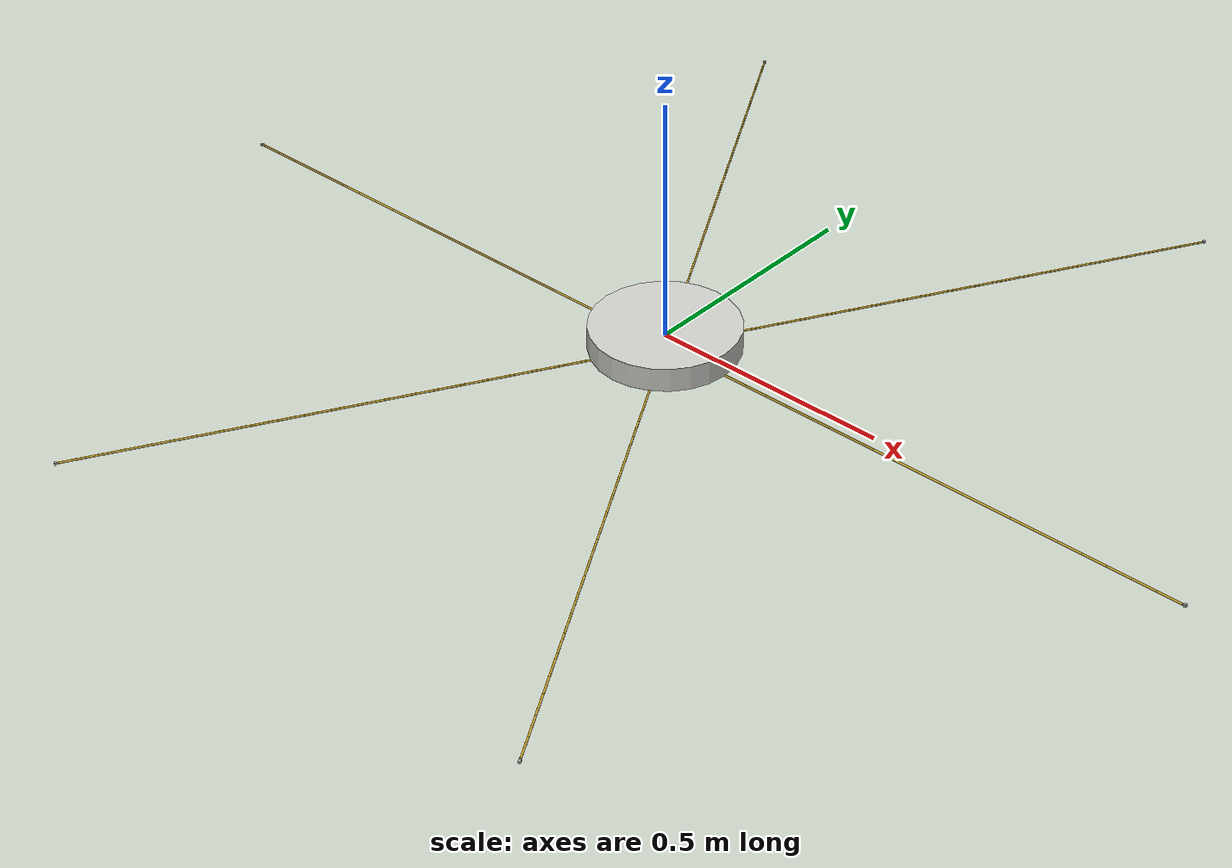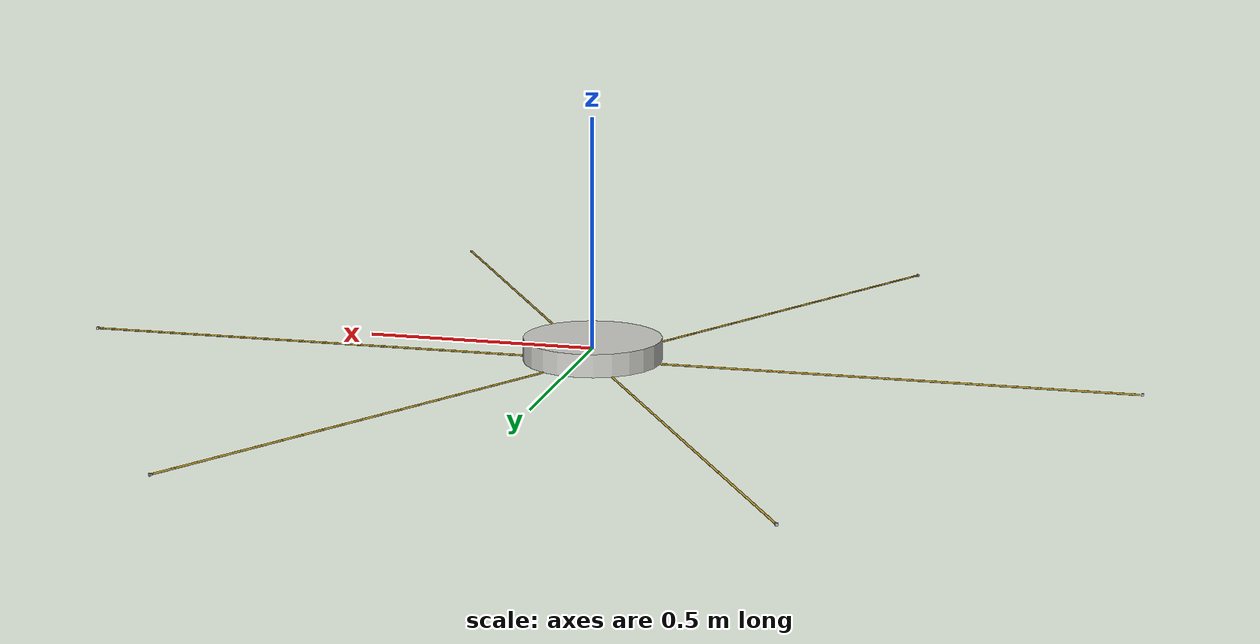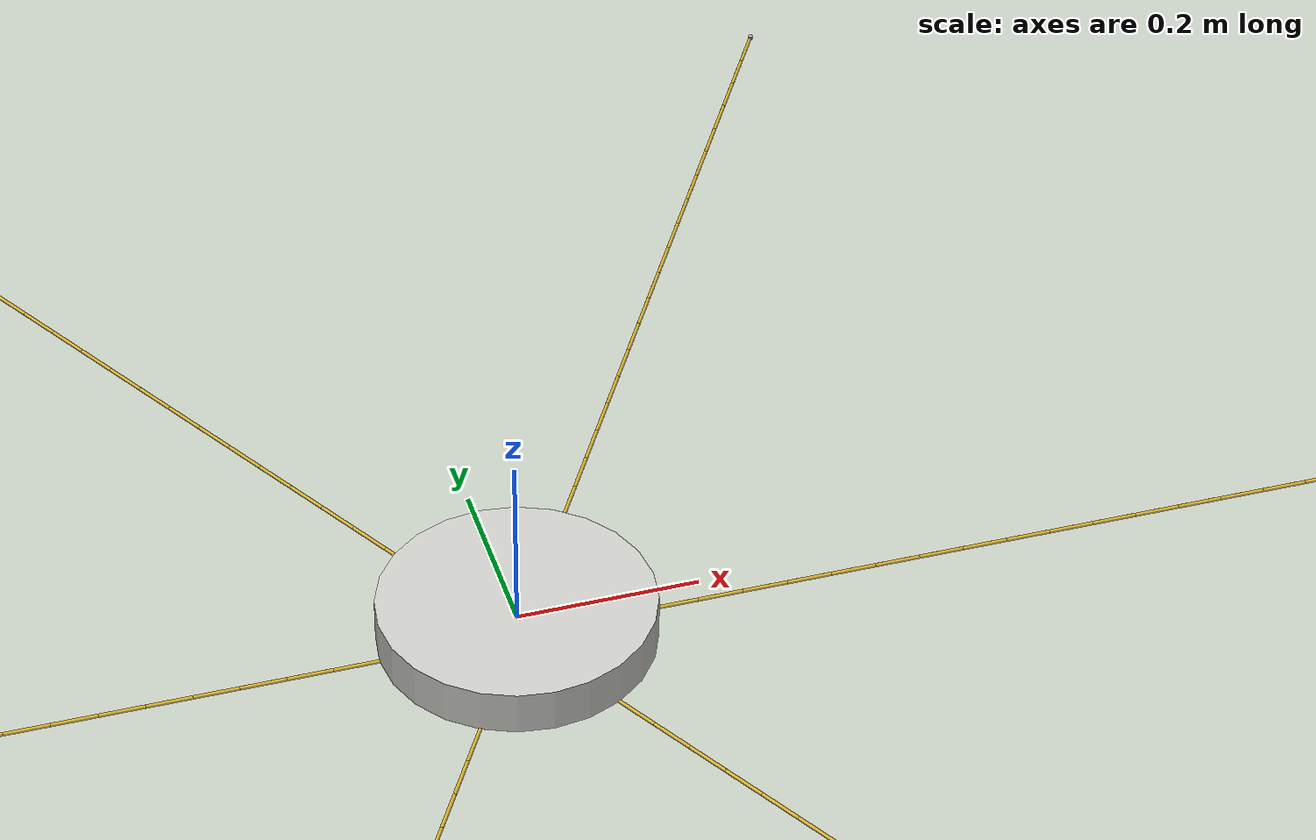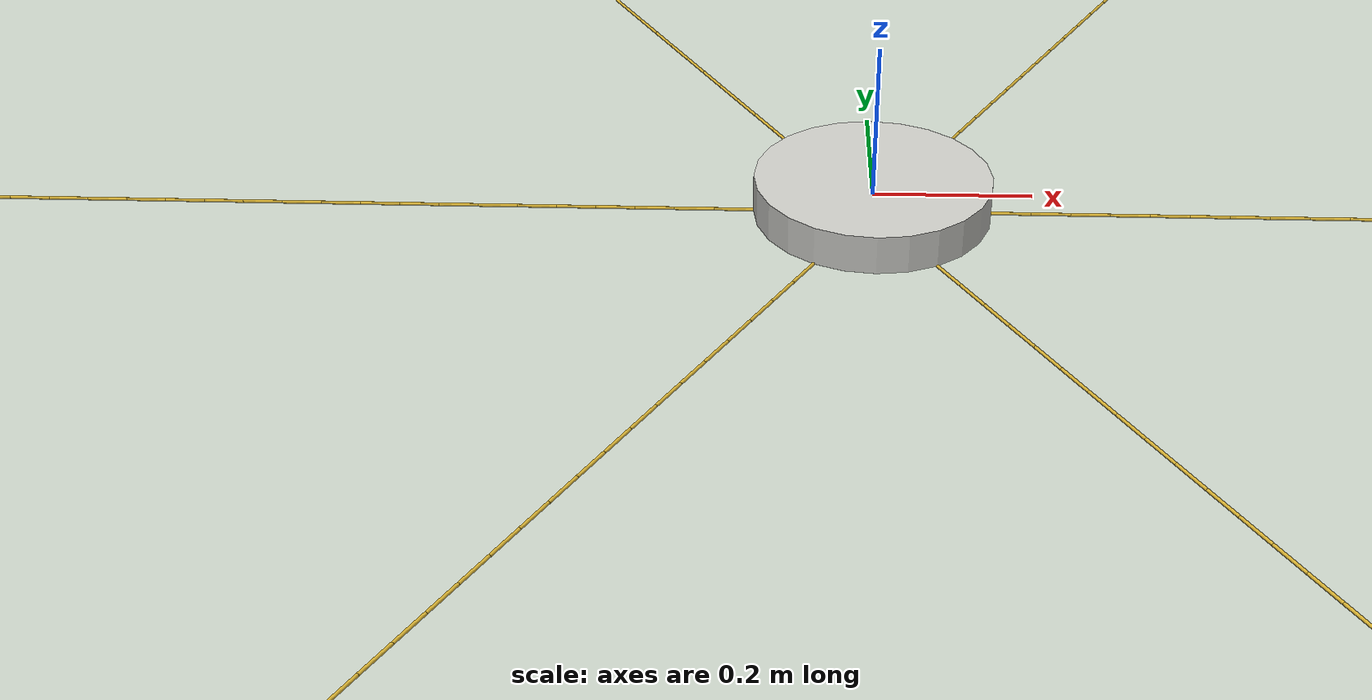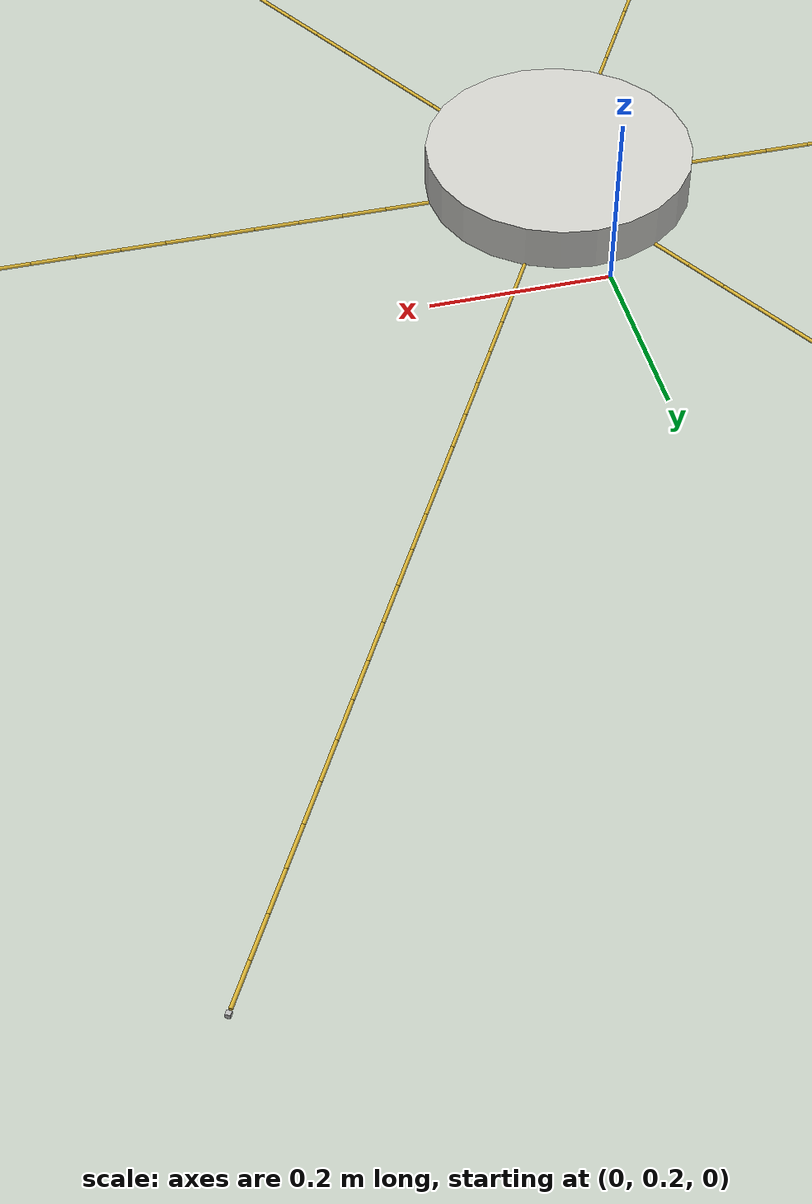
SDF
<?xml version="1.0" ?>
<sdf version='1.7'>
  <!-- Model starting from payload as the parent -->
  <model name='flexible_cable'>

    <!-- Define your constants and properties here -->

    <!-- Calculations for inertia -->

    <!-- Payload initial position -->

    <!-- Elasticity Params -->

    <!-- Payload link as the parent link -->
    <link name="payload">
      <pose>
        0 0 0.0 0 0 0
      </pose>
      <inertial>
        <mass>1.2</mass>
        <inertia>
          <ixx>0.007</ixx>
          <iyy>0.007</iyy>
          <izz>0.00225</izz>
        </inertia>
      </inertial>
      <collision name='payload_collision'>
        <geometry>
          <cylinder>
            <length>0.05</length>
            <radius>0.15</radius>
          </cylinder>
        </geometry>
      </collision>
      <visual name='payload_visual'>
        <geometry>
          <cylinder>
            <length>0.05</length>
            <radius>0.15</radius>
          </cylinder>
        </geometry>
        <material>
          <script>
            <name>Gazebo/CeilingTiled</name>
            <uri>file://media/materials/scripts/gazebo.material</uri>
          </script>
        </material>
      </visual>
    </link>

    <!-- Calculate attachment point on the payload -->

    <!-- Joint connecting payload to the first cable segment -->
    <joint name='cable_1_joint_payload' type='universal'>
      <pose relative_to="payload">
        0.15 0.0 -0.025  0 1.5707963267948966 0.0
      </pose>
      <parent>payload</parent>
      <child>cable_1_segment_0_p</child>
      <axis>
        <xyz>0 1 0</xyz>
      </axis>
      <axis2>
        <xyz>1 0 0</xyz>
      </axis2>
    </joint>

    <!-- First parent segment connected to the payload -->
    <link name='cable_1_segment_0_p'>
      <pose relative_to="cable_1_joint_payload">
        0 0 0.025 0 0 0
      </pose>
      <inertial>
        <mass>0.01</mass>
        <inertia>
          <ixx>8.343333333333334e-06</ixx>
          <iyy>8.343333333333334e-06</iyy>
          <izz>2e-08</izz>
        </inertia>
      </inertial>
      <collision name='cable_1_segment_0_p_collision'>
        <geometry>
          <cylinder>
            <length>0.05</length>
            <radius>0.002</radius>
          </cylinder>
        </geometry>
        <collide_bitmask>0x01</collide_bitmask>
      </collision>
      <visual name='cable_1_segment_0_p_visual'>
        <geometry>
          <cylinder>
            <length>0.05</length>
            <radius>0.002</radius>
          </cylinder>
        </geometry>
        <material>
          <script>
            <name>Gazebo/Gold</name>
            <uri>file://media/materials/scripts/gazebo.material</uri>
          </script>
        </material>
      </visual>
    </link>

    <joint name="cable_1_prismatic_segment_0" type="prismatic">
        <child>cable_1_segment_0_c</child>
        <parent>cable_1_segment_0_p</parent>
        <pose relative_to="cable_1_segment_0_p">0 0 0.025 0 -0 0</pose>
        <axis>
            <xyz>0.0 0.0 1.0</xyz>
            <limit>
                <effort>-1</effort>
            </limit>
            <dynamics>
              <spring_stiffness>100000.0</spring_stiffness>
              <spring_reference>0.0</spring_reference>
              <damping>0</damping>
              <friction>0.0</friction>
            </dynamics>
        </axis>
        <physics>
        <provide_feedback>1</provide_feedback>
        <ode>
          <implicit_spring_damper>1</implicit_spring_damper>
          <cfm_damping>1</cfm_damping>
          <limit>
            <cfm>0</cfm>
            <erp>0.2</erp>
          </limit>
        </ode>
      </physics>
    </joint>

    <link name='cable_1_segment_0_c'>
      <pose relative_to="cable_1_prismatic_segment_0">
        0 0 0.025 0 0 0
      </pose>
      <inertial>
        <mass>0.01</mass>
        <inertia>
          <ixx>8.343333333333334e-06</ixx>
          <iyy>8.343333333333334e-06</iyy>
          <izz>2e-08</izz>
        </inertia>
      </inertial>
      <collision name='cable_1_segment_0_c_collision'>
        <geometry>
          <cylinder>
            <length>0.05</length>
            <radius>0.002</radius>
          </cylinder>
        </geometry>
        <collide_bitmask>0x01</collide_bitmask>
      </collision>
      <visual name='cable_1_segment_0_c_visual'>
        <geometry>
          <cylinder>
            <length>0.05</length>
            <radius>0.002</radius>
          </cylinder>
        </geometry>
        <material>
          <script>
            <name>Gazebo/Gold</name>
            <uri>file://media/materials/scripts/gazebo.material</uri>
          </script>
        </material>
      </visual>
    </link>

    <joint name='cable_1_joint_1' type='universal'>
      <pose relative_to="cable_1_segment_0_c">
        0 0 0.025  0 0 0
      </pose>
      <parent>cable_1_segment_0_c</parent>
      <child>cable_1_segment_1_p</child>
      <axis>
        <xyz>0 1 0</xyz>
      </axis>
      <axis2>
        <xyz>1 0 0</xyz>
      </axis2>
    </joint>

    <!-- Subsequent cable segments -->
    <link name='cable_1_segment_1_p'>
      <pose relative_to="cable_1_joint_1">
        0 0 0.025 0 0 0
      </pose>
      <inertial>
        <mass>0.01</mass>
        <inertia>
          <ixx>8.343333333333334e-06</ixx>
          <iyy>8.343333333333334e-06</iyy>
          <izz>2e-08</izz>
        </inertia>
      </inertial>
      <collision name='cable_1_segment_1_p_collision'>
        <geometry>
          <cylinder>
            <length>0.05</length>
            <radius>0.002</radius>
          </cylinder>
        </geometry>
        <collide_bitmask>0x01</collide_bitmask>
      </collision>
      <visual name='cable_1_segment_1_p_visual'>
        <geometry>
          <cylinder>
            <length>0.05</length>
            <radius>0.002</radius>
          </cylinder>
        </geometry>
        <material>
          <script>
            <name>Gazebo/Gold</name>
            <uri>file://media/materials/scripts/gazebo.material</uri>
          </script>
        </material>
      </visual>
    </link>

    <joint name="cable_1_prismatic_segment_1" type="prismatic">
        <child>cable_1_segment_1_c</child>
        <parent>cable_1_segment_1_p</parent>
        <pose relative_to="cable_1_segment_1_p">0 0 0.025 0 -0 0</pose>
        <axis>
            <xyz>0.0 0.0 1.0</xyz>
            <limit>
                <effort>-1</effort>
            </limit>
            <dynamics>
              <spring_stiffness>100000.0</spring_stiffness>
              <spring_reference>0.0</spring_reference>
              <damping>0</damping>
              <friction>0.0</friction>
            </dynamics>
        </axis>
        <physics>
        <provide_feedback>1</provide_feedback>
        <ode>
          <implicit_spring_damper>1</implicit_spring_damper>
          <cfm_damping>1</cfm_damping>
          <limit>
            <cfm>0</cfm>
            <erp>0.2</erp>
          </limit>
        </ode>
      </physics>
    </joint>

    <link name='cable_1_segment_1_c'>
      <pose relative_to="cable_1_prismatic_segment_1">
        0 0 0.025 0 0 0
      </pose>
      <inertial>
        <mass>0.01</mass>
        <inertia>
          <ixx>8.343333333333334e-06</ixx>
          <iyy>8.343333333333334e-06</iyy>
          <izz>2e-08</izz>
        </inertia>
      </inertial>
      <collision name='cable_1_segment_1_c_collision'>
        <geometry>
          <cylinder>
            <length>0.05</length>
            <radius>0.002</radius>
          </cylinder>
        </geometry>
        <collide_bitmask>0x01</collide_bitmask>
      </collision>
      <visual name='cable_1_segment_1_c_visual'>
        <geometry>
          <cylinder>
            <length>0.05</length>
            <radius>0.002</radius>
          </cylinder>
        </geometry>
        <material>
          <script>
            <name>Gazebo/Gold</name>
            <uri>file://media/materials/scripts/gazebo.material</uri>
          </script>
        </material>
      </visual>
    </link>

    <joint name='cable_1_joint_2' type='universal'>
      <pose relative_to="cable_1_segment_1_c">
        0 0 0.025  0 0 0
      </pose>
      <parent>cable_1_segment_1_c</parent>
      <child>cable_1_segment_2_p</child>
      <axis>
        <xyz>0 1 0</xyz>
      </axis>
      <axis2>
        <xyz>1 0 0</xyz>
      </axis2>
    </joint>

    <!-- Subsequent cable segments -->
    <link name='cable_1_segment_2_p'>
      <pose relative_to="cable_1_joint_2">
        0 0 0.025 0 0 0
      </pose>
      <inertial>
        <mass>0.01</mass>
        <inertia>
          <ixx>8.343333333333334e-06</ixx>
          <iyy>8.343333333333334e-06</iyy>
          <izz>2e-08</izz>
        </inertia>
      </inertial>
      <collision name='cable_1_segment_2_p_collision'>
        <geometry>
          <cylinder>
            <length>0.05</length>
            <radius>0.002</radius>
          </cylinder>
        </geometry>
        <collide_bitmask>0x01</collide_bitmask>
      </collision>
      <visual name='cable_1_segment_2_p_visual'>
        <geometry>
          <cylinder>
            <length>0.05</length>
            <radius>0.002</radius>
          </cylinder>
        </geometry>
        <material>
          <script>
            <name>Gazebo/Gold</name>
            <uri>file://media/materials/scripts/gazebo.material</uri>
          </script>
        </material>
      </visual>
    </link>

    <joint name="cable_1_prismatic_segment_2" type="prismatic">
        <child>cable_1_segment_2_c</child>
        <parent>cable_1_segment_2_p</parent>
        <pose relative_to="cable_1_segment_2_p">0 0 0.025 0 -0 0</pose>
        <axis>
            <xyz>0.0 0.0 1.0</xyz>
            <limit>
                <effort>-1</effort>
            </limit>
            <dynamics>
              <spring_stiffness>100000.0</spring_stiffness>
              <spring_reference>0.0</spring_reference>
              <damping>0</damping>
              <friction>0.0</friction>
            </dynamics>
        </axis>
        <physics>
        <provide_feedback>1</provide_feedback>
        <ode>
          <implicit_spring_damper>1</implicit_spring_damper>
          <cfm_damping>1</cfm_damping>
          <limit>
            <cfm>0</cfm>
            <erp>0.2</erp>
          </limit>
        </ode>
      </physics>
    </joint>

    <link name='cable_1_segment_2_c'>
      <pose relative_to="cable_1_prismatic_segment_2">
        0 0 0.025 0 0 0
      </pose>
      <inertial>
        <mass>0.01</mass>
        <inertia>
          <ixx>8.343333333333334e-06</ixx>
          <iyy>8.343333333333334e-06</iyy>
          <izz>2e-08</izz>
        </inertia>
      </inertial>
      <collision name='cable_1_segment_2_c_collision'>
        <geometry>
          <cylinder>
            <length>0.05</length>
            <radius>0.002</radius>
          </cylinder>
        </geometry>
        <collide_bitmask>0x01</collide_bitmask>
      </collision>
      <visual name='cable_1_segment_2_c_visual'>
        <geometry>
          <cylinder>
            <length>0.05</length>
            <radius>0.002</radius>
          </cylinder>
        </geometry>
        <material>
          <script>
            <name>Gazebo/Gold</name>
            <uri>file://media/materials/scripts/gazebo.material</uri>
          </script>
        </material>
      </visual>
    </link>

    <joint name='cable_1_joint_3' type='universal'>
      <pose relative_to="cable_1_segment_2_c">
        0 0 0.025  0 0 0
      </pose>
      <parent>cable_1_segment_2_c</parent>
      <child>cable_1_segment_3_p</child>
      <axis>
        <xyz>0 1 0</xyz>
      </axis>
      <axis2>
        <xyz>1 0 0</xyz>
      </axis2>
    </joint>

    <!-- Subsequent cable segments -->
    <link name='cable_1_segment_3_p'>
      <pose relative_to="cable_1_joint_3">
        0 0 0.025 0 0 0
      </pose>
      <inertial>
        <mass>0.01</mass>
        <inertia>
          <ixx>8.343333333333334e-06</ixx>
          <iyy>8.343333333333334e-06</iyy>
          <izz>2e-08</izz>
        </inertia>
      </inertial>
      <collision name='cable_1_segment_3_p_collision'>
        <geometry>
          <cylinder>
            <length>0.05</length>
            <radius>0.002</radius>
          </cylinder>
        </geometry>
        <collide_bitmask>0x01</collide_bitmask>
      </collision>
      <visual name='cable_1_segment_3_p_visual'>
        <geometry>
          <cylinder>
            <length>0.05</length>
            <radius>0.002</radius>
          </cylinder>
        </geometry>
        <material>
          <script>
            <name>Gazebo/Gold</name>
            <uri>file://media/materials/scripts/gazebo.material</uri>
          </script>
        </material>
      </visual>
    </link>

    <joint name="cable_1_prismatic_segment_3" type="prismatic">
        <child>cable_1_segment_3_c</child>
        <parent>cable_1_segment_3_p</parent>
        <pose relative_to="cable_1_segment_3_p">0 0 0.025 0 -0 0</pose>
        <axis>
            <xyz>0.0 0.0 1.0</xyz>
            <limit>
                <effort>-1</effort>
            </limit>
            <dynamics>
              <spring_stiffness>100000.0</spring_stiffness>
              <spring_reference>0.0</spring_reference>
              <damping>0</damping>
              <friction>0.0</friction>
            </dynamics>
        </axis>
        <physics>
        <provide_feedback>1</provide_feedback>
        <ode>
          <implicit_spring_damper>1</implicit_spring_damper>
          <cfm_damping>1</cfm_damping>
          <limit>
            <cfm>0</cfm>
            <erp>0.2</erp>
          </limit>
        </ode>
      </physics>
    </joint>

    <link name='cable_1_segment_3_c'>
      <pose relative_to="cable_1_prismatic_segment_3">
        0 0 0.025 0 0 0
      </pose>
      <inertial>
        <mass>0.01</mass>
        <inertia>
          <ixx>8.343333333333334e-06</ixx>
          <iyy>8.343333333333334e-06</iyy>
          <izz>2e-08</izz>
        </inertia>
      </inertial>
      <collision name='cable_1_segment_3_c_collision'>
        <geometry>
          <cylinder>
            <length>0.05</length>
            <radius>0.002</radius>
          </cylinder>
        </geometry>
        <collide_bitmask>0x01</collide_bitmask>
      </collision>
      <visual name='cable_1_segment_3_c_visual'>
        <geometry>
          <cylinder>
            <length>0.05</length>
            <radius>0.002</radius>
          </cylinder>
        </geometry>
        <material>
          <script>
            <name>Gazebo/Gold</name>
            <uri>file://media/materials/scripts/gazebo.material</uri>
          </script>
        </material>
      </visual>
    </link>

    <joint name='cable_1_joint_4' type='universal'>
      <pose relative_to="cable_1_segment_3_c">
        0 0 0.025  0 0 0
      </pose>
      <parent>cable_1_segment_3_c</parent>
      <child>cable_1_segment_4_p</child>
      <axis>
        <xyz>0 1 0</xyz>
      </axis>
      <axis2>
        <xyz>1 0 0</xyz>
      </axis2>
    </joint>

    <!-- Subsequent cable segments -->
    <link name='cable_1_segment_4_p'>
      <pose relative_to="cable_1_joint_4">
        0 0 0.025 0 0 0
      </pose>
      <inertial>
        <mass>0.01</mass>
        <inertia>
          <ixx>8.343333333333334e-06</ixx>
          <iyy>8.343333333333334e-06</iyy>
          <izz>2e-08</izz>
        </inertia>
      </inertial>
      <collision name='cable_1_segment_4_p_collision'>
        <geometry>
          <cylinder>
            <length>0.05</length>
            <radius>0.002</radius>
          </cylinder>
        </geometry>
        <collide_bitmask>0x01</collide_bitmask>
      </collision>
      <visual name='cable_1_segment_4_p_visual'>
        <geometry>
          <cylinder>
            <length>0.05</length>
            <radius>0.002</radius>
          </cylinder>
        </geometry>
        <material>
          <script>
            <name>Gazebo/Gold</name>
            <uri>file://media/materials/scripts/gazebo.material</uri>
          </script>
        </material>
      </visual>
    </link>

    <joint name="cable_1_prismatic_segment_4" type="prismatic">
        <child>cable_1_segment_4_c</child>
        <parent>cable_1_segment_4_p</parent>
        <pose relative_to="cable_1_segment_4_p">0 0 0.025 0 -0 0</pose>
        <axis>
            <xyz>0.0 0.0 1.0</xyz>
            <limit>
                <effort>-1</effort>
            </limit>
            <dynamics>
              <spring_stiffness>100000.0</spring_stiffness>
              <spring_reference>0.0</spring_reference>
              <damping>0</damping>
              <friction>0.0</friction>
            </dynamics>
        </axis>
        <physics>
        <provide_feedback>1</provide_feedback>
        <ode>
          <implicit_spring_damper>1</implicit_spring_damper>
          <cfm_damping>1</cfm_damping>
          <limit>
            <cfm>0</cfm>
            <erp>0.2</erp>
          </limit>
        </ode>
      </physics>
    </joint>

    <link name='cable_1_segment_4_c'>
      <pose relative_to="cable_1_prismatic_segment_4">
        0 0 0.025 0 0 0
      </pose>
      <inertial>
        <mass>0.01</mass>
        <inertia>
          <ixx>8.343333333333334e-06</ixx>
          <iyy>8.343333333333334e-06</iyy>
          <izz>2e-08</izz>
        </inertia>
      </inertial>
      <collision name='cable_1_segment_4_c_collision'>
        <geometry>
          <cylinder>
            <length>0.05</length>
            <radius>0.002</radius>
          </cylinder>
        </geometry>
        <collide_bitmask>0x01</collide_bitmask>
      </collision>
      <visual name='cable_1_segment_4_c_visual'>
        <geometry>
          <cylinder>
            <length>0.05</length>
            <radius>0.002</radius>
          </cylinder>
        </geometry>
        <material>
          <script>
            <name>Gazebo/Gold</name>
            <uri>file://media/materials/scripts/gazebo.material</uri>
          </script>
        </material>
      </visual>
    </link>

    <joint name='cable_1_joint_5' type='universal'>
      <pose relative_to="cable_1_segment_4_c">
        0 0 0.025  0 0 0
      </pose>
      <parent>cable_1_segment_4_c</parent>
      <child>cable_1_segment_5_p</child>
      <axis>
        <xyz>0 1 0</xyz>
      </axis>
      <axis2>
        <xyz>1 0 0</xyz>
      </axis2>
    </joint>

    <!-- Subsequent cable segments -->
    <link name='cable_1_segment_5_p'>
      <pose relative_to="cable_1_joint_5">
        0 0 0.025 0 0 0
      </pose>
      <inertial>
        <mass>0.01</mass>
        <inertia>
          <ixx>8.343333333333334e-06</ixx>
          <iyy>8.343333333333334e-06</iyy>
          <izz>2e-08</izz>
        </inertia>
      </inertial>
      <collision name='cable_1_segment_5_p_collision'>
        <geometry>
          <cylinder>
            <length>0.05</length>
            <radius>0.002</radius>
          </cylinder>
        </geometry>
        <collide_bitmask>0x01</collide_bitmask>
      </collision>
      <visual name='cable_1_segment_5_p_visual'>
        <geometry>
          <cylinder>
            <length>0.05</length>
            <radius>0.002</radius>
          </cylinder>
        </geometry>
        <material>
          <script>
            <name>Gazebo/Gold</name>
            <uri>file://media/materials/scripts/gazebo.material</uri>
          </script>
        </material>
      </visual>
    </link>

    <joint name="cable_1_prismatic_segment_5" type="prismatic">
        <child>cable_1_segment_5_c</child>
        <parent>cable_1_segment_5_p</parent>
        <pose relative_to="cable_1_segment_5_p">0 0 0.025 0 -0 0</pose>
        <axis>
            <xyz>0.0 0.0 1.0</xyz>
            <limit>
                <effort>-1</effort>
            </limit>
            <dynamics>
              <spring_stiffness>100000.0</spring_stiffness>
              <spring_reference>0.0</spring_reference>
              <damping>0</damping>
              <friction>0.0</friction>
            </dynamics>
        </axis>
        <physics>
        <provide_feedback>1</provide_feedback>
        <ode>
          <implicit_spring_damper>1</implicit_spring_damper>
          <cfm_damping>1</cfm_damping>
          <limit>
            <cfm>0</cfm>
            <erp>0.2</erp>
          </limit>
        </ode>
      </physics>
    </joint>

    <link name='cable_1_segment_5_c'>
      <pose relative_to="cable_1_prismatic_segment_5">
        0 0 0.025 0 0 0
      </pose>
      <inertial>
        <mass>0.01</mass>
        <inertia>
          <ixx>8.343333333333334e-06</ixx>
          <iyy>8.343333333333334e-06</iyy>
          <izz>2e-08</izz>
        </inertia>
      </inertial>
      <collision name='cable_1_segment_5_c_collision'>
        <geometry>
          <cylinder>
            <length>0.05</length>
            <radius>0.002</radius>
          </cylinder>
        </geometry>
        <collide_bitmask>0x01</collide_bitmask>
      </collision>
      <visual name='cable_1_segment_5_c_visual'>
        <geometry>
          <cylinder>
            <length>0.05</length>
            <radius>0.002</radius>
          </cylinder>
        </geometry>
        <material>
          <script>
            <name>Gazebo/Gold</name>
            <uri>file://media/materials/scripts/gazebo.material</uri>
          </script>
        </material>
      </visual>
    </link>

    <joint name='cable_1_joint_6' type='universal'>
      <pose relative_to="cable_1_segment_5_c">
        0 0 0.025  0 0 0
      </pose>
      <parent>cable_1_segment_5_c</parent>
      <child>cable_1_segment_6_p</child>
      <axis>
        <xyz>0 1 0</xyz>
      </axis>
      <axis2>
        <xyz>1 0 0</xyz>
      </axis2>
    </joint>

    <!-- Subsequent cable segments -->
    <link name='cable_1_segment_6_p'>
      <pose relative_to="cable_1_joint_6">
        0 0 0.025 0 0 0
      </pose>
      <inertial>
        <mass>0.01</mass>
        <inertia>
          <ixx>8.343333333333334e-06</ixx>
          <iyy>8.343333333333334e-06</iyy>
          <izz>2e-08</izz>
        </inertia>
      </inertial>
      <collision name='cable_1_segment_6_p_collision'>
        <geometry>
          <cylinder>
            <length>0.05</length>
            <radius>0.002</radius>
          </cylinder>
        </geometry>
        <collide_bitmask>0x01</collide_bitmask>
      </collision>
      <visual name='cable_1_segment_6_p_visual'>
        <geometry>
          <cylinder>
            <length>0.05</length>
            <radius>0.002</radius>
          </cylinder>
        </geometry>
        <material>
          <script>
            <name>Gazebo/Gold</name>
            <uri>file://media/materials/scripts/gazebo.material</uri>
          </script>
        </material>
      </visual>
    </link>

    <joint name="cable_1_prismatic_segment_6" type="prismatic">
        <child>cable_1_segment_6_c</child>
        <parent>cable_1_segment_6_p</parent>
        <pose relative_to="cable_1_segment_6_p">0 0 0.025 0 -0 0</pose>
        <axis>
            <xyz>0.0 0.0 1.0</xyz>
            <limit>
                <effort>-1</effort>
            </limit>
            <dynamics>
              <spring_stiffness>100000.0</spring_stiffness>
              <spring_reference>0.0</spring_reference>
              <damping>0</damping>
              <friction>0.0</friction>
            </dynamics>
        </axis>
        <physics>
        <provide_feedback>1</provide_feedback>
        <ode>
          <implicit_spring_damper>1</implicit_spring_damper>
          <cfm_damping>1</cfm_damping>
          <limit>
            <cfm>0</cfm>
            <erp>0.2</erp>
          </limit>
        </ode>
      </physics>
    </joint>

    <link name='cable_1_segment_6_c'>
      <pose relative_to="cable_1_prismatic_segment_6">
        0 0 0.025 0 0 0
      </pose>
      <inertial>
        <mass>0.01</mass>
        <inertia>
          <ixx>8.343333333333334e-06</ixx>
          <iyy>8.343333333333334e-06</iyy>
          <izz>2e-08</izz>
        </inertia>
      </inertial>
      <collision name='cable_1_segment_6_c_collision'>
        <geometry>
          <cylinder>
            <length>0.05</length>
            <radius>0.002</radius>
          </cylinder>
        </geometry>
        <collide_bitmask>0x01</collide_bitmask>
      </collision>
      <visual name='cable_1_segment_6_c_visual'>
        <geometry>
          <cylinder>
            <length>0.05</length>
            <radius>0.002</radius>
          </cylinder>
        </geometry>
        <material>
          <script>
            <name>Gazebo/Gold</name>
            <uri>file://media/materials/scripts/gazebo.material</uri>
          </script>
        </material>
      </visual>
    </link>

    <joint name='cable_1_joint_7' type='universal'>
      <pose relative_to="cable_1_segment_6_c">
        0 0 0.025  0 0 0
      </pose>
      <parent>cable_1_segment_6_c</parent>
      <child>cable_1_segment_7_p</child>
      <axis>
        <xyz>0 1 0</xyz>
      </axis>
      <axis2>
        <xyz>1 0 0</xyz>
      </axis2>
    </joint>

    <!-- Subsequent cable segments -->
    <link name='cable_1_segment_7_p'>
      <pose relative_to="cable_1_joint_7">
        0 0 0.025 0 0 0
      </pose>
      <inertial>
        <mass>0.01</mass>
        <inertia>
          <ixx>8.343333333333334e-06</ixx>
          <iyy>8.343333333333334e-06</iyy>
          <izz>2e-08</izz>
        </inertia>
      </inertial>
      <collision name='cable_1_segment_7_p_collision'>
        <geometry>
          <cylinder>
            <length>0.05</length>
            <radius>0.002</radius>
          </cylinder>
        </geometry>
        <collide_bitmask>0x01</collide_bitmask>
      </collision>
      <visual name='cable_1_segment_7_p_visual'>
        <geometry>
          <cylinder>
            <length>0.05</length>
            <radius>0.002</radius>
          </cylinder>
        </geometry>
        <material>
          <script>
            <name>Gazebo/Gold</name>
            <uri>file://media/materials/scripts/gazebo.material</uri>
          </script>
        </material>
      </visual>
    </link>

    <joint name="cable_1_prismatic_segment_7" type="prismatic">
        <child>cable_1_segment_7_c</child>
        <parent>cable_1_segment_7_p</parent>
        <pose relative_to="cable_1_segment_7_p">0 0 0.025 0 -0 0</pose>
        <axis>
            <xyz>0.0 0.0 1.0</xyz>
            <limit>
                <effort>-1</effort>
            </limit>
            <dynamics>
              <spring_stiffness>100000.0</spring_stiffness>
              <spring_reference>0.0</spring_reference>
              <damping>0</damping>
              <friction>0.0</friction>
            </dynamics>
        </axis>
        <physics>
        <provide_feedback>1</provide_feedback>
        <ode>
          <implicit_spring_damper>1</implicit_spring_damper>
          <cfm_damping>1</cfm_damping>
          <limit>
            <cfm>0</cfm>
            <erp>0.2</erp>
          </limit>
        </ode>
      </physics>
    </joint>

    <link name='cable_1_segment_7_c'>
      <pose relative_to="cable_1_prismatic_segment_7">
        0 0 0.025 0 0 0
      </pose>
      <inertial>
        <mass>0.01</mass>
        <inertia>
          <ixx>8.343333333333334e-06</ixx>
          <iyy>8.343333333333334e-06</iyy>
          <izz>2e-08</izz>
        </inertia>
      </inertial>
      <collision name='cable_1_segment_7_c_collision'>
        <geometry>
          <cylinder>
            <length>0.05</length>
            <radius>0.002</radius>
          </cylinder>
        </geometry>
        <collide_bitmask>0x01</collide_bitmask>
      </collision>
      <visual name='cable_1_segment_7_c_visual'>
        <geometry>
          <cylinder>
            <length>0.05</length>
            <radius>0.002</radius>
          </cylinder>
        </geometry>
        <material>
          <script>
            <name>Gazebo/Gold</name>
            <uri>file://media/materials/scripts/gazebo.material</uri>
          </script>
        </material>
      </visual>
    </link>

    <joint name='cable_1_joint_8' type='universal'>
      <pose relative_to="cable_1_segment_7_c">
        0 0 0.025  0 0 0
      </pose>
      <parent>cable_1_segment_7_c</parent>
      <child>cable_1_segment_8_p</child>
      <axis>
        <xyz>0 1 0</xyz>
      </axis>
      <axis2>
        <xyz>1 0 0</xyz>
      </axis2>
    </joint>

    <!-- Subsequent cable segments -->
    <link name='cable_1_segment_8_p'>
      <pose relative_to="cable_1_joint_8">
        0 0 0.025 0 0 0
      </pose>
      <inertial>
        <mass>0.01</mass>
        <inertia>
          <ixx>8.343333333333334e-06</ixx>
          <iyy>8.343333333333334e-06</iyy>
          <izz>2e-08</izz>
        </inertia>
      </inertial>
      <collision name='cable_1_segment_8_p_collision'>
        <geometry>
          <cylinder>
            <length>0.05</length>
            <radius>0.002</radius>
          </cylinder>
        </geometry>
        <collide_bitmask>0x01</collide_bitmask>
      </collision>
      <visual name='cable_1_segment_8_p_visual'>
        <geometry>
          <cylinder>
            <length>0.05</length>
            <radius>0.002</radius>
          </cylinder>
        </geometry>
        <material>
          <script>
            <name>Gazebo/Gold</name>
            <uri>file://media/materials/scripts/gazebo.material</uri>
          </script>
        </material>
      </visual>
    </link>

    <joint name="cable_1_prismatic_segment_8" type="prismatic">
        <child>cable_1_segment_8_c</child>
        <parent>cable_1_segment_8_p</parent>
        <pose relative_to="cable_1_segment_8_p">0 0 0.025 0 -0 0</pose>
        <axis>
            <xyz>0.0 0.0 1.0</xyz>
            <limit>
                <effort>-1</effort>
            </limit>
            <dynamics>
              <spring_stiffness>100000.0</spring_stiffness>
              <spring_reference>0.0</spring_reference>
              <damping>0</damping>
              <friction>0.0</friction>
            </dynamics>
        </axis>
        <physics>
        <provide_feedback>1</provide_feedback>
        <ode>
          <implicit_spring_damper>1</implicit_spring_damper>
          <cfm_damping>1</cfm_damping>
          <limit>
            <cfm>0</cfm>
            <erp>0.2</erp>
          </limit>
        </ode>
      </physics>
    </joint>

    <link name='cable_1_segment_8_c'>
      <pose relative_to="cable_1_prismatic_segment_8">
        0 0 0.025 0 0 0
      </pose>
      <inertial>
        <mass>0.01</mass>
        <inertia>
          <ixx>8.343333333333334e-06</ixx>
          <iyy>8.343333333333334e-06</iyy>
          <izz>2e-08</izz>
        </inertia>
      </inertial>
      <collision name='cable_1_segment_8_c_collision'>
        <geometry>
          <cylinder>
            <length>0.05</length>
            <radius>0.002</radius>
          </cylinder>
        </geometry>
        <collide_bitmask>0x01</collide_bitmask>
      </collision>
      <visual name='cable_1_segment_8_c_visual'>
        <geometry>
          <cylinder>
            <length>0.05</length>
            <radius>0.002</radius>
          </cylinder>
        </geometry>
        <material>
          <script>
            <name>Gazebo/Gold</name>
            <uri>file://media/materials/scripts/gazebo.material</uri>
          </script>
        </material>
      </visual>
    </link>

    <joint name='cable_1_joint_9' type='universal'>
      <pose relative_to="cable_1_segment_8_c">
        0 0 0.025  0 0 0
      </pose>
      <parent>cable_1_segment_8_c</parent>
      <child>cable_1_segment_9_p</child>
      <axis>
        <xyz>0 1 0</xyz>
      </axis>
      <axis2>
        <xyz>1 0 0</xyz>
      </axis2>
    </joint>

    <!-- Subsequent cable segments -->
    <link name='cable_1_segment_9_p'>
      <pose relative_to="cable_1_joint_9">
        0 0 0.025 0 0 0
      </pose>
      <inertial>
        <mass>0.01</mass>
        <inertia>
          <ixx>8.343333333333334e-06</ixx>
          <iyy>8.343333333333334e-06</iyy>
          <izz>2e-08</izz>
        </inertia>
      </inertial>
      <collision name='cable_1_segment_9_p_collision'>
        <geometry>
          <cylinder>
            <length>0.05</length>
            <radius>0.002</radius>
          </cylinder>
        </geometry>
        <collide_bitmask>0x01</collide_bitmask>
      </collision>
      <visual name='cable_1_segment_9_p_visual'>
        <geometry>
          <cylinder>
            <length>0.05</length>
            <radius>0.002</radius>
          </cylinder>
        </geometry>
        <material>
          <script>
            <name>Gazebo/Gold</name>
            <uri>file://media/materials/scripts/gazebo.material</uri>
          </script>
        </material>
      </visual>
    </link>

    <joint name="cable_1_prismatic_segment_9" type="prismatic">
        <child>cable_1_segment_9_c</child>
        <parent>cable_1_segment_9_p</parent>
        <pose relative_to="cable_1_segment_9_p">0 0 0.025 0 -0 0</pose>
        <axis>
            <xyz>0.0 0.0 1.0</xyz>
            <limit>
                <effort>-1</effort>
            </limit>
            <dynamics>
              <spring_stiffness>100000.0</spring_stiffness>
              <spring_reference>0.0</spring_reference>
              <damping>0</damping>
              <friction>0.0</friction>
            </dynamics>
        </axis>
        <physics>
        <provide_feedback>1</provide_feedback>
        <ode>
          <implicit_spring_damper>1</implicit_spring_damper>
          <cfm_damping>1</cfm_damping>
          <limit>
            <cfm>0</cfm>
            <erp>0.2</erp>
          </limit>
        </ode>
      </physics>
    </joint>

    <link name='cable_1_segment_9_c'>
      <pose relative_to="cable_1_prismatic_segment_9">
        0 0 0.025 0 0 0
      </pose>
      <inertial>
        <mass>0.01</mass>
        <inertia>
          <ixx>8.343333333333334e-06</ixx>
          <iyy>8.343333333333334e-06</iyy>
          <izz>2e-08</izz>
        </inertia>
      </inertial>
      <collision name='cable_1_segment_9_c_collision'>
        <geometry>
          <cylinder>
            <length>0.05</length>
            <radius>0.002</radius>
          </cylinder>
        </geometry>
        <collide_bitmask>0x01</collide_bitmask>
      </collision>
      <visual name='cable_1_segment_9_c_visual'>
        <geometry>
          <cylinder>
            <length>0.05</length>
            <radius>0.002</radius>
          </cylinder>
        </geometry>
        <material>
          <script>
            <name>Gazebo/Gold</name>
            <uri>file://media/materials/scripts/gazebo.material</uri>
          </script>
        </material>
      </visual>
    </link>

    <!-- Attach the last segment to the world -->
    <joint name='cable_1_base_universal' type='universal'>
      <pose relative_to="cable_1_segment_9_c">
        0 0 0.025  0 0 0
      </pose>
      <parent>cable_1_segment_9_c</parent>
      <child>cable_1_attach</child>
      <axis>
        <xyz>0 1 0</xyz>
      </axis>
      <axis2>
        <xyz>1 0 0</xyz>
      </axis2>
    </joint>

    <link name='cable_1_attach'>
      <pose relative_to='cable_1_base_universal'>0 0 0.005 0 -0 0</pose>
      <inertial>
        <mass>0.0001</mass>
        <inertia>
          <ixx>1e-5</ixx>
          <ixy>0</ixy>
          <ixz>0</ixz>
          <iyy>1e-5</iyy>
          <iyz>0</iyz>
          <izz>1e-5</izz>
        </inertia>
      </inertial>
      <collision name='cable_1_attach_collision'>
        <geometry>
          <box>
            <size>0.005 0.005 0.005</size>
          </box>
        </geometry>
      </collision>
      <visual name='cable_1_attach_visual'>
        <geometry>
          <box>
            <size>0.005 0.005 0.005</size>
          </box>
        </geometry>
      </visual>
      <self_collide>0</self_collide>
    </link>

    <!-- Calculate attachment point on the payload -->

    <!-- Joint connecting payload to the first cable segment -->
    <joint name='cable_2_joint_payload' type='universal'>
      <pose relative_to="payload">
        0.07500000000000001 0.12990381056766578 -0.025  0 1.5707963267948966 1.0471975511965976
      </pose>
      <parent>payload</parent>
      <child>cable_2_segment_0_p</child>
      <axis>
        <xyz>0 1 0</xyz>
      </axis>
      <axis2>
        <xyz>1 0 0</xyz>
      </axis2>
    </joint>

    <!-- First parent segment connected to the payload -->
    <link name='cable_2_segment_0_p'>
      <pose relative_to="cable_2_joint_payload">
        0 0 0.025 0 0 0
      </pose>
      <inertial>
        <mass>0.01</mass>
        <inertia>
          <ixx>8.343333333333334e-06</ixx>
          <iyy>8.343333333333334e-06</iyy>
          <izz>2e-08</izz>
        </inertia>
      </inertial>
      <collision name='cable_2_segment_0_p_collision'>
        <geometry>
          <cylinder>
            <length>0.05</length>
            <radius>0.002</radius>
          </cylinder>
        </geometry>
        <collide_bitmask>0x01</collide_bitmask>
      </collision>
      <visual name='cable_2_segment_0_p_visual'>
        <geometry>
          <cylinder>
            <length>0.05</length>
            <radius>0.002</radius>
          </cylinder>
        </geometry>
        <material>
          <script>
            <name>Gazebo/Gold</name>
            <uri>file://media/materials/scripts/gazebo.material</uri>
          </script>
        </material>
      </visual>
    </link>

    <joint name="cable_2_prismatic_segment_0" type="prismatic">
        <child>cable_2_segment_0_c</child>
        <parent>cable_2_segment_0_p</parent>
        <pose relative_to="cable_2_segment_0_p">0 0 0.025 0 -0 0</pose>
        <axis>
            <xyz>0.0 0.0 1.0</xyz>
            <limit>
                <effort>-1</effort>
            </limit>
            <dynamics>
              <spring_stiffness>100000.0</spring_stiffness>
              <spring_reference>0.0</spring_reference>
              <damping>0</damping>
              <friction>0.0</friction>
            </dynamics>
        </axis>
        <physics>
        <provide_feedback>1</provide_feedback>
        <ode>
          <implicit_spring_damper>1</implicit_spring_damper>
          <cfm_damping>1</cfm_damping>
          <limit>
            <cfm>0</cfm>
            <erp>0.2</erp>
          </limit>
        </ode>
      </physics>
    </joint>

    <link name='cable_2_segment_0_c'>
      <pose relative_to="cable_2_prismatic_segment_0">
        0 0 0.025 0 0 0
      </pose>
      <inertial>
        <mass>0.01</mass>
        <inertia>
          <ixx>8.343333333333334e-06</ixx>
          <iyy>8.343333333333334e-06</iyy>
          <izz>2e-08</izz>
        </inertia>
      </inertial>
      <collision name='cable_2_segment_0_c_collision'>
        <geometry>
          <cylinder>
            <length>0.05</length>
            <radius>0.002</radius>
          </cylinder>
        </geometry>
        <collide_bitmask>0x01</collide_bitmask>
      </collision>
      <visual name='cable_2_segment_0_c_visual'>
        <geometry>
          <cylinder>
            <length>0.05</length>
            <radius>0.002</radius>
          </cylinder>
        </geometry>
        <material>
          <script>
            <name>Gazebo/Gold</name>
            <uri>file://media/materials/scripts/gazebo.material</uri>
          </script>
        </material>
      </visual>
    </link>

    <joint name='cable_2_joint_1' type='universal'>
      <pose relative_to="cable_2_segment_0_c">
        0 0 0.025  0 0 0
      </pose>
      <parent>cable_2_segment_0_c</parent>
      <child>cable_2_segment_1_p</child>
      <axis>
        <xyz>0 1 0</xyz>
      </axis>
      <axis2>
        <xyz>1 0 0</xyz>
      </axis2>
    </joint>

    <!-- Subsequent cable segments -->
    <link name='cable_2_segment_1_p'>
      <pose relative_to="cable_2_joint_1">
        0 0 0.025 0 0 0
      </pose>
      <inertial>
        <mass>0.01</mass>
        <inertia>
          <ixx>8.343333333333334e-06</ixx>
          <iyy>8.343333333333334e-06</iyy>
          <izz>2e-08</izz>
        </inertia>
      </inertial>
      <collision name='cable_2_segment_1_p_collision'>
        <geometry>
          <cylinder>
            <length>0.05</length>
            <radius>0.002</radius>
          </cylinder>
        </geometry>
        <collide_bitmask>0x01</collide_bitmask>
      </collision>
      <visual name='cable_2_segment_1_p_visual'>
        <geometry>
          <cylinder>
            <length>0.05</length>
            <radius>0.002</radius>
          </cylinder>
        </geometry>
        <material>
          <script>
            <name>Gazebo/Gold</name>
            <uri>file://media/materials/scripts/gazebo.material</uri>
          </script>
        </material>
      </visual>
    </link>

    <joint name="cable_2_prismatic_segment_1" type="prismatic">
        <child>cable_2_segment_1_c</child>
        <parent>cable_2_segment_1_p</parent>
        <pose relative_to="cable_2_segment_1_p">0 0 0.025 0 -0 0</pose>
        <axis>
            <xyz>0.0 0.0 1.0</xyz>
            <limit>
                <effort>-1</effort>
            </limit>
            <dynamics>
              <spring_stiffness>100000.0</spring_stiffness>
              <spring_reference>0.0</spring_reference>
              <damping>0</damping>
              <friction>0.0</friction>
            </dynamics>
        </axis>
        <physics>
        <provide_feedback>1</provide_feedback>
        <ode>
          <implicit_spring_damper>1</implicit_spring_damper>
          <cfm_damping>1</cfm_damping>
          <limit>
            <cfm>0</cfm>
            <erp>0.2</erp>
          </limit>
        </ode>
      </physics>
    </joint>

    <link name='cable_2_segment_1_c'>
      <pose relative_to="cable_2_prismatic_segment_1">
        0 0 0.025 0 0 0
      </pose>
      <inertial>
        <mass>0.01</mass>
        <inertia>
          <ixx>8.343333333333334e-06</ixx>
          <iyy>8.343333333333334e-06</iyy>
          <izz>2e-08</izz>
        </inertia>
      </inertial>
      <collision name='cable_2_segment_1_c_collision'>
        <geometry>
          <cylinder>
            <length>0.05</length>
            <radius>0.002</radius>
          </cylinder>
        </geometry>
        <collide_bitmask>0x01</collide_bitmask>
      </collision>
      <visual name='cable_2_segment_1_c_visual'>
        <geometry>
          <cylinder>
            <length>0.05</length>
            <radius>0.002</radius>
          </cylinder>
        </geometry>
        <material>
          <script>
            <name>Gazebo/Gold</name>
            <uri>file://media/materials/scripts/gazebo.material</uri>
          </script>
        </material>
      </visual>
    </link>

    <joint name='cable_2_joint_2' type='universal'>
      <pose relative_to="cable_2_segment_1_c">
        0 0 0.025  0 0 0
      </pose>
      <parent>cable_2_segment_1_c</parent>
      <child>cable_2_segment_2_p</child>
      <axis>
        <xyz>0 1 0</xyz>
      </axis>
      <axis2>
        <xyz>1 0 0</xyz>
      </axis2>
    </joint>

    <!-- Subsequent cable segments -->
    <link name='cable_2_segment_2_p'>
      <pose relative_to="cable_2_joint_2">
        0 0 0.025 0 0 0
      </pose>
      <inertial>
        <mass>0.01</mass>
        <inertia>
          <ixx>8.343333333333334e-06</ixx>
          <iyy>8.343333333333334e-06</iyy>
          <izz>2e-08</izz>
        </inertia>
      </inertial>
      <collision name='cable_2_segment_2_p_collision'>
        <geometry>
          <cylinder>
            <length>0.05</length>
            <radius>0.002</radius>
          </cylinder>
        </geometry>
        <collide_bitmask>0x01</collide_bitmask>
      </collision>
      <visual name='cable_2_segment_2_p_visual'>
        <geometry>
          <cylinder>
            <length>0.05</length>
            <radius>0.002</radius>
          </cylinder>
        </geometry>
        <material>
          <script>
            <name>Gazebo/Gold</name>
            <uri>file://media/materials/scripts/gazebo.material</uri>
          </script>
        </material>
      </visual>
    </link>

    <joint name="cable_2_prismatic_segment_2" type="prismatic">
        <child>cable_2_segment_2_c</child>
        <parent>cable_2_segment_2_p</parent>
        <pose relative_to="cable_2_segment_2_p">0 0 0.025 0 -0 0</pose>
        <axis>
            <xyz>0.0 0.0 1.0</xyz>
            <limit>
                <effort>-1</effort>
            </limit>
            <dynamics>
              <spring_stiffness>100000.0</spring_stiffness>
              <spring_reference>0.0</spring_reference>
              <damping>0</damping>
              <friction>0.0</friction>
            </dynamics>
        </axis>
        <physics>
        <provide_feedback>1</provide_feedback>
        <ode>
          <implicit_spring_damper>1</implicit_spring_damper>
          <cfm_damping>1</cfm_damping>
          <limit>
            <cfm>0</cfm>
            <erp>0.2</erp>
          </limit>
        </ode>
      </physics>
    </joint>

    <link name='cable_2_segment_2_c'>
      <pose relative_to="cable_2_prismatic_segment_2">
        0 0 0.025 0 0 0
      </pose>
      <inertial>
        <mass>0.01</mass>
        <inertia>
          <ixx>8.343333333333334e-06</ixx>
          <iyy>8.343333333333334e-06</iyy>
          <izz>2e-08</izz>
        </inertia>
      </inertial>
      <collision name='cable_2_segment_2_c_collision'>
        <geometry>
          <cylinder>
            <length>0.05</length>
            <radius>0.002</radius>
          </cylinder>
        </geometry>
        <collide_bitmask>0x01</collide_bitmask>
      </collision>
      <visual name='cable_2_segment_2_c_visual'>
        <geometry>
          <cylinder>
            <length>0.05</length>
            <radius>0.002</radius>
          </cylinder>
        </geometry>
        <material>
          <script>
            <name>Gazebo/Gold</name>
            <uri>file://media/materials/scripts/gazebo.material</uri>
          </script>
        </material>
      </visual>
    </link>

    <joint name='cable_2_joint_3' type='universal'>
      <pose relative_to="cable_2_segment_2_c">
        0 0 0.025  0 0 0
      </pose>
      <parent>cable_2_segment_2_c</parent>
      <child>cable_2_segment_3_p</child>
      <axis>
        <xyz>0 1 0</xyz>
      </axis>
      <axis2>
        <xyz>1 0 0</xyz>
      </axis2>
    </joint>

    <!-- Subsequent cable segments -->
    <link name='cable_2_segment_3_p'>
      <pose relative_to="cable_2_joint_3">
        0 0 0.025 0 0 0
      </pose>
      <inertial>
        <mass>0.01</mass>
        <inertia>
          <ixx>8.343333333333334e-06</ixx>
          <iyy>8.343333333333334e-06</iyy>
          <izz>2e-08</izz>
        </inertia>
      </inertial>
      <collision name='cable_2_segment_3_p_collision'>
        <geometry>
          <cylinder>
            <length>0.05</length>
            <radius>0.002</radius>
          </cylinder>
        </geometry>
        <collide_bitmask>0x01</collide_bitmask>
      </collision>
      <visual name='cable_2_segment_3_p_visual'>
        <geometry>
          <cylinder>
            <length>0.05</length>
            <radius>0.002</radius>
          </cylinder>
        </geometry>
        <material>
          <script>
            <name>Gazebo/Gold</name>
            <uri>file://media/materials/scripts/gazebo.material</uri>
          </script>
        </material>
      </visual>
    </link>

    <joint name="cable_2_prismatic_segment_3" type="prismatic">
        <child>cable_2_segment_3_c</child>
        <parent>cable_2_segment_3_p</parent>
        <pose relative_to="cable_2_segment_3_p">0 0 0.025 0 -0 0</pose>
        <axis>
            <xyz>0.0 0.0 1.0</xyz>
            <limit>
                <effort>-1</effort>
            </limit>
            <dynamics>
              <spring_stiffness>100000.0</spring_stiffness>
              <spring_reference>0.0</spring_reference>
              <damping>0</damping>
              <friction>0.0</friction>
            </dynamics>
        </axis>
        <physics>
        <provide_feedback>1</provide_feedback>
        <ode>
          <implicit_spring_damper>1</implicit_spring_damper>
          <cfm_damping>1</cfm_damping>
          <limit>
            <cfm>0</cfm>
            <erp>0.2</erp>
          </limit>
        </ode>
      </physics>
    </joint>

    <link name='cable_2_segment_3_c'>
      <pose relative_to="cable_2_prismatic_segment_3">
        0 0 0.025 0 0 0
      </pose>
      <inertial>
        <mass>0.01</mass>
        <inertia>
          <ixx>8.343333333333334e-06</ixx>
          <iyy>8.343333333333334e-06</iyy>
          <izz>2e-08</izz>
        </inertia>
      </inertial>
      <collision name='cable_2_segment_3_c_collision'>
        <geometry>
          <cylinder>
            <length>0.05</length>
            <radius>0.002</radius>
          </cylinder>
        </geometry>
        <collide_bitmask>0x01</collide_bitmask>
      </collision>
      <visual name='cable_2_segment_3_c_visual'>
        <geometry>
          <cylinder>
            <length>0.05</length>
            <radius>0.002</radius>
          </cylinder>
        </geometry>
        <material>
          <script>
            <name>Gazebo/Gold</name>
            <uri>file://media/materials/scripts/gazebo.material</uri>
          </script>
        </material>
      </visual>
    </link>

    <joint name='cable_2_joint_4' type='universal'>
      <pose relative_to="cable_2_segment_3_c">
        0 0 0.025  0 0 0
      </pose>
      <parent>cable_2_segment_3_c</parent>
      <child>cable_2_segment_4_p</child>
      <axis>
        <xyz>0 1 0</xyz>
      </axis>
      <axis2>
        <xyz>1 0 0</xyz>
      </axis2>
    </joint>

    <!-- Subsequent cable segments -->
    <link name='cable_2_segment_4_p'>
      <pose relative_to="cable_2_joint_4">
        0 0 0.025 0 0 0
      </pose>
      <inertial>
        <mass>0.01</mass>
        <inertia>
          <ixx>8.343333333333334e-06</ixx>
          <iyy>8.343333333333334e-06</iyy>
          <izz>2e-08</izz>
        </inertia>
      </inertial>
      <collision name='cable_2_segment_4_p_collision'>
        <geometry>
          <cylinder>
            <length>0.05</length>
            <radius>0.002</radius>
          </cylinder>
        </geometry>
        <collide_bitmask>0x01</collide_bitmask>
      </collision>
      <visual name='cable_2_segment_4_p_visual'>
        <geometry>
          <cylinder>
            <length>0.05</length>
            <radius>0.002</radius>
          </cylinder>
        </geometry>
        <material>
          <script>
            <name>Gazebo/Gold</name>
            <uri>file://media/materials/scripts/gazebo.material</uri>
          </script>
        </material>
      </visual>
    </link>

    <joint name="cable_2_prismatic_segment_4" type="prismatic">
        <child>cable_2_segment_4_c</child>
        <parent>cable_2_segment_4_p</parent>
        <pose relative_to="cable_2_segment_4_p">0 0 0.025 0 -0 0</pose>
        <axis>
            <xyz>0.0 0.0 1.0</xyz>
            <limit>
                <effort>-1</effort>
            </limit>
            <dynamics>
              <spring_stiffness>100000.0</spring_stiffness>
              <spring_reference>0.0</spring_reference>
              <damping>0</damping>
              <friction>0.0</friction>
            </dynamics>
        </axis>
        <physics>
        <provide_feedback>1</provide_feedback>
        <ode>
          <implicit_spring_damper>1</implicit_spring_damper>
          <cfm_damping>1</cfm_damping>
          <limit>
            <cfm>0</cfm>
            <erp>0.2</erp>
          </limit>
        </ode>
      </physics>
    </joint>

    <link name='cable_2_segment_4_c'>
      <pose relative_to="cable_2_prismatic_segment_4">
        0 0 0.025 0 0 0
      </pose>
      <inertial>
        <mass>0.01</mass>
        <inertia>
          <ixx>8.343333333333334e-06</ixx>
          <iyy>8.343333333333334e-06</iyy>
          <izz>2e-08</izz>
        </inertia>
      </inertial>
      <collision name='cable_2_segment_4_c_collision'>
        <geometry>
          <cylinder>
            <length>0.05</length>
            <radius>0.002</radius>
          </cylinder>
        </geometry>
        <collide_bitmask>0x01</collide_bitmask>
      </collision>
      <visual name='cable_2_segment_4_c_visual'>
        <geometry>
          <cylinder>
            <length>0.05</length>
            <radius>0.002</radius>
          </cylinder>
        </geometry>
        <material>
          <script>
            <name>Gazebo/Gold</name>
            <uri>file://media/materials/scripts/gazebo.material</uri>
          </script>
        </material>
      </visual>
    </link>

    <joint name='cable_2_joint_5' type='universal'>
      <pose relative_to="cable_2_segment_4_c">
        0 0 0.025  0 0 0
      </pose>
      <parent>cable_2_segment_4_c</parent>
      <child>cable_2_segment_5_p</child>
      <axis>
        <xyz>0 1 0</xyz>
      </axis>
      <axis2>
        <xyz>1 0 0</xyz>
      </axis2>
    </joint>

    <!-- Subsequent cable segments -->
    <link name='cable_2_segment_5_p'>
      <pose relative_to="cable_2_joint_5">
        0 0 0.025 0 0 0
      </pose>
      <inertial>
        <mass>0.01</mass>
        <inertia>
          <ixx>8.343333333333334e-06</ixx>
          <iyy>8.343333333333334e-06</iyy>
          <izz>2e-08</izz>
        </inertia>
      </inertial>
      <collision name='cable_2_segment_5_p_collision'>
        <geometry>
          <cylinder>
            <length>0.05</length>
            <radius>0.002</radius>
          </cylinder>
        </geometry>
        <collide_bitmask>0x01</collide_bitmask>
      </collision>
      <visual name='cable_2_segment_5_p_visual'>
        <geometry>
          <cylinder>
            <length>0.05</length>
            <radius>0.002</radius>
          </cylinder>
        </geometry>
        <material>
          <script>
            <name>Gazebo/Gold</name>
            <uri>file://media/materials/scripts/gazebo.material</uri>
          </script>
        </material>
      </visual>
    </link>

    <joint name="cable_2_prismatic_segment_5" type="prismatic">
        <child>cable_2_segment_5_c</child>
        <parent>cable_2_segment_5_p</parent>
        <pose relative_to="cable_2_segment_5_p">0 0 0.025 0 -0 0</pose>
        <axis>
            <xyz>0.0 0.0 1.0</xyz>
            <limit>
                <effort>-1</effort>
            </limit>
            <dynamics>
              <spring_stiffness>100000.0</spring_stiffness>
              <spring_reference>0.0</spring_reference>
              <damping>0</damping>
              <friction>0.0</friction>
            </dynamics>
        </axis>
        <physics>
        <provide_feedback>1</provide_feedback>
        <ode>
          <implicit_spring_damper>1</implicit_spring_damper>
          <cfm_damping>1</cfm_damping>
          <limit>
            <cfm>0</cfm>
            <erp>0.2</erp>
          </limit>
        </ode>
      </physics>
    </joint>

    <link name='cable_2_segment_5_c'>
      <pose relative_to="cable_2_prismatic_segment_5">
        0 0 0.025 0 0 0
      </pose>
      <inertial>
        <mass>0.01</mass>
        <inertia>
          <ixx>8.343333333333334e-06</ixx>
          <iyy>8.343333333333334e-06</iyy>
          <izz>2e-08</izz>
        </inertia>
      </inertial>
      <collision name='cable_2_segment_5_c_collision'>
        <geometry>
          <cylinder>
            <length>0.05</length>
            <radius>0.002</radius>
          </cylinder>
        </geometry>
        <collide_bitmask>0x01</collide_bitmask>
      </collision>
      <visual name='cable_2_segment_5_c_visual'>
        <geometry>
          <cylinder>
            <length>0.05</length>
            <radius>0.002</radius>
          </cylinder>
        </geometry>
        <material>
          <script>
            <name>Gazebo/Gold</name>
            <uri>file://media/materials/scripts/gazebo.material</uri>
          </script>
        </material>
      </visual>
    </link>

    <joint name='cable_2_joint_6' type='universal'>
      <pose relative_to="cable_2_segment_5_c">
        0 0 0.025  0 0 0
      </pose>
      <parent>cable_2_segment_5_c</parent>
      <child>cable_2_segment_6_p</child>
      <axis>
        <xyz>0 1 0</xyz>
      </axis>
      <axis2>
        <xyz>1 0 0</xyz>
      </axis2>
    </joint>

    <!-- Subsequent cable segments -->
    <link name='cable_2_segment_6_p'>
      <pose relative_to="cable_2_joint_6">
        0 0 0.025 0 0 0
      </pose>
      <inertial>
        <mass>0.01</mass>
        <inertia>
          <ixx>8.343333333333334e-06</ixx>
          <iyy>8.343333333333334e-06</iyy>
          <izz>2e-08</izz>
        </inertia>
      </inertial>
      <collision name='cable_2_segment_6_p_collision'>
        <geometry>
          <cylinder>
            <length>0.05</length>
            <radius>0.002</radius>
          </cylinder>
        </geometry>
        <collide_bitmask>0x01</collide_bitmask>
      </collision>
      <visual name='cable_2_segment_6_p_visual'>
        <geometry>
          <cylinder>
            <length>0.05</length>
            <radius>0.002</radius>
          </cylinder>
        </geometry>
        <material>
          <script>
            <name>Gazebo/Gold</name>
            <uri>file://media/materials/scripts/gazebo.material</uri>
          </script>
        </material>
      </visual>
    </link>

    <joint name="cable_2_prismatic_segment_6" type="prismatic">
        <child>cable_2_segment_6_c</child>
        <parent>cable_2_segment_6_p</parent>
        <pose relative_to="cable_2_segment_6_p">0 0 0.025 0 -0 0</pose>
        <axis>
            <xyz>0.0 0.0 1.0</xyz>
            <limit>
                <effort>-1</effort>
            </limit>
            <dynamics>
              <spring_stiffness>100000.0</spring_stiffness>
              <spring_reference>0.0</spring_reference>
              <damping>0</damping>
              <friction>0.0</friction>
            </dynamics>
        </axis>
        <physics>
        <provide_feedback>1</provide_feedback>
        <ode>
          <implicit_spring_damper>1</implicit_spring_damper>
          <cfm_damping>1</cfm_damping>
          <limit>
            <cfm>0</cfm>
            <erp>0.2</erp>
          </limit>
        </ode>
      </physics>
    </joint>

    <link name='cable_2_segment_6_c'>
      <pose relative_to="cable_2_prismatic_segment_6">
        0 0 0.025 0 0 0
      </pose>
      <inertial>
        <mass>0.01</mass>
        <inertia>
          <ixx>8.343333333333334e-06</ixx>
          <iyy>8.343333333333334e-06</iyy>
          <izz>2e-08</izz>
        </inertia>
      </inertial>
      <collision name='cable_2_segment_6_c_collision'>
        <geometry>
          <cylinder>
            <length>0.05</length>
            <radius>0.002</radius>
          </cylinder>
        </geometry>
        <collide_bitmask>0x01</collide_bitmask>
      </collision>
      <visual name='cable_2_segment_6_c_visual'>
        <geometry>
          <cylinder>
            <length>0.05</length>
            <radius>0.002</radius>
          </cylinder>
        </geometry>
        <material>
          <script>
            <name>Gazebo/Gold</name>
            <uri>file://media/materials/scripts/gazebo.material</uri>
          </script>
        </material>
      </visual>
    </link>

    <joint name='cable_2_joint_7' type='universal'>
      <pose relative_to="cable_2_segment_6_c">
        0 0 0.025  0 0 0
      </pose>
      <parent>cable_2_segment_6_c</parent>
      <child>cable_2_segment_7_p</child>
      <axis>
        <xyz>0 1 0</xyz>
      </axis>
      <axis2>
        <xyz>1 0 0</xyz>
      </axis2>
    </joint>

    <!-- Subsequent cable segments -->
    <link name='cable_2_segment_7_p'>
      <pose relative_to="cable_2_joint_7">
        0 0 0.025 0 0 0
      </pose>
      <inertial>
        <mass>0.01</mass>
        <inertia>
          <ixx>8.343333333333334e-06</ixx>
          <iyy>8.343333333333334e-06</iyy>
          <izz>2e-08</izz>
        </inertia>
      </inertial>
      <collision name='cable_2_segment_7_p_collision'>
        <geometry>
          <cylinder>
            <length>0.05</length>
            <radius>0.002</radius>
          </cylinder>
        </geometry>
        <collide_bitmask>0x01</collide_bitmask>
      </collision>
      <visual name='cable_2_segment_7_p_visual'>
        <geometry>
          <cylinder>
            <length>0.05</length>
            <radius>0.002</radius>
          </cylinder>
        </geometry>
        <material>
          <script>
            <name>Gazebo/Gold</name>
            <uri>file://media/materials/scripts/gazebo.material</uri>
          </script>
        </material>
      </visual>
    </link>

    <joint name="cable_2_prismatic_segment_7" type="prismatic">
        <child>cable_2_segment_7_c</child>
        <parent>cable_2_segment_7_p</parent>
        <pose relative_to="cable_2_segment_7_p">0 0 0.025 0 -0 0</pose>
        <axis>
            <xyz>0.0 0.0 1.0</xyz>
            <limit>
                <effort>-1</effort>
            </limit>
            <dynamics>
              <spring_stiffness>100000.0</spring_stiffness>
              <spring_reference>0.0</spring_reference>
              <damping>0</damping>
              <friction>0.0</friction>
            </dynamics>
        </axis>
        <physics>
        <provide_feedback>1</provide_feedback>
        <ode>
          <implicit_spring_damper>1</implicit_spring_damper>
          <cfm_damping>1</cfm_damping>
          <limit>
            <cfm>0</cfm>
            <erp>0.2</erp>
          </limit>
        </ode>
      </physics>
    </joint>

    <link name='cable_2_segment_7_c'>
      <pose relative_to="cable_2_prismatic_segment_7">
        0 0 0.025 0 0 0
      </pose>
      <inertial>
        <mass>0.01</mass>
        <inertia>
          <ixx>8.343333333333334e-06</ixx>
          <iyy>8.343333333333334e-06</iyy>
          <izz>2e-08</izz>
        </inertia>
      </inertial>
      <collision name='cable_2_segment_7_c_collision'>
        <geometry>
          <cylinder>
            <length>0.05</length>
            <radius>0.002</radius>
          </cylinder>
        </geometry>
        <collide_bitmask>0x01</collide_bitmask>
      </collision>
      <visual name='cable_2_segment_7_c_visual'>
        <geometry>
          <cylinder>
            <length>0.05</length>
            <radius>0.002</radius>
          </cylinder>
        </geometry>
        <material>
          <script>
            <name>Gazebo/Gold</name>
            <uri>file://media/materials/scripts/gazebo.material</uri>
          </script>
        </material>
      </visual>
    </link>

    <joint name='cable_2_joint_8' type='universal'>
      <pose relative_to="cable_2_segment_7_c">
        0 0 0.025  0 0 0
      </pose>
      <parent>cable_2_segment_7_c</parent>
      <child>cable_2_segment_8_p</child>
      <axis>
        <xyz>0 1 0</xyz>
      </axis>
      <axis2>
        <xyz>1 0 0</xyz>
      </axis2>
    </joint>

    <!-- Subsequent cable segments -->
    <link name='cable_2_segment_8_p'>
      <pose relative_to="cable_2_joint_8">
        0 0 0.025 0 0 0
      </pose>
      <inertial>
        <mass>0.01</mass>
        <inertia>
          <ixx>8.343333333333334e-06</ixx>
          <iyy>8.343333333333334e-06</iyy>
          <izz>2e-08</izz>
        </inertia>
      </inertial>
      <collision name='cable_2_segment_8_p_collision'>
        <geometry>
          <cylinder>
            <length>0.05</length>
            <radius>0.002</radius>
          </cylinder>
        </geometry>
        <collide_bitmask>0x01</collide_bitmask>
      </collision>
      <visual name='cable_2_segment_8_p_visual'>
        <geometry>
          <cylinder>
            <length>0.05</length>
            <radius>0.002</radius>
          </cylinder>
        </geometry>
        <material>
          <script>
            <name>Gazebo/Gold</name>
            <uri>file://media/materials/scripts/gazebo.material</uri>
          </script>
        </material>
      </visual>
    </link>

    <joint name="cable_2_prismatic_segment_8" type="prismatic">
        <child>cable_2_segment_8_c</child>
        <parent>cable_2_segment_8_p</parent>
        <pose relative_to="cable_2_segment_8_p">0 0 0.025 0 -0 0</pose>
        <axis>
            <xyz>0.0 0.0 1.0</xyz>
            <limit>
                <effort>-1</effort>
            </limit>
            <dynamics>
              <spring_stiffness>100000.0</spring_stiffness>
              <spring_reference>0.0</spring_reference>
              <damping>0</damping>
              <friction>0.0</friction>
            </dynamics>
        </axis>
        <physics>
        <provide_feedback>1</provide_feedback>
        <ode>
          <implicit_spring_damper>1</implicit_spring_damper>
          <cfm_damping>1</cfm_damping>
          <limit>
            <cfm>0</cfm>
            <erp>0.2</erp>
          </limit>
        </ode>
      </physics>
    </joint>

    <link name='cable_2_segment_8_c'>
      <pose relative_to="cable_2_prismatic_segment_8">
        0 0 0.025 0 0 0
      </pose>
      <inertial>
        <mass>0.01</mass>
        <inertia>
          <ixx>8.343333333333334e-06</ixx>
          <iyy>8.343333333333334e-06</iyy>
          <izz>2e-08</izz>
        </inertia>
      </inertial>
      <collision name='cable_2_segment_8_c_collision'>
        <geometry>
          <cylinder>
            <length>0.05</length>
            <radius>0.002</radius>
          </cylinder>
        </geometry>
        <collide_bitmask>0x01</collide_bitmask>
      </collision>
      <visual name='cable_2_segment_8_c_visual'>
        <geometry>
          <cylinder>
            <length>0.05</length>
            <radius>0.002</radius>
          </cylinder>
        </geometry>
        <material>
          <script>
            <name>Gazebo/Gold</name>
            <uri>file://media/materials/scripts/gazebo.material</uri>
          </script>
        </material>
      </visual>
    </link>

    <joint name='cable_2_joint_9' type='universal'>
      <pose relative_to="cable_2_segment_8_c">
        0 0 0.025  0 0 0
      </pose>
      <parent>cable_2_segment_8_c</parent>
      <child>cable_2_segment_9_p</child>
      <axis>
        <xyz>0 1 0</xyz>
      </axis>
      <axis2>
        <xyz>1 0 0</xyz>
      </axis2>
    </joint>

    <!-- Subsequent cable segments -->
    <link name='cable_2_segment_9_p'>
      <pose relative_to="cable_2_joint_9">
        0 0 0.025 0 0 0
      </pose>
      <inertial>
        <mass>0.01</mass>
        <inertia>
          <ixx>8.343333333333334e-06</ixx>
          <iyy>8.343333333333334e-06</iyy>
          <izz>2e-08</izz>
        </inertia>
      </inertial>
      <collision name='cable_2_segment_9_p_collision'>
        <geometry>
          <cylinder>
            <length>0.05</length>
            <radius>0.002</radius>
          </cylinder>
        </geometry>
        <collide_bitmask>0x01</collide_bitmask>
      </collision>
      <visual name='cable_2_segment_9_p_visual'>
        <geometry>
          <cylinder>
            <length>0.05</length>
            <radius>0.002</radius>
          </cylinder>
        </geometry>
        <material>
          <script>
            <name>Gazebo/Gold</name>
            <uri>file://media/materials/scripts/gazebo.material</uri>
          </script>
        </material>
      </visual>
    </link>

    <joint name="cable_2_prismatic_segment_9" type="prismatic">
        <child>cable_2_segment_9_c</child>
        <parent>cable_2_segment_9_p</parent>
        <pose relative_to="cable_2_segment_9_p">0 0 0.025 0 -0 0</pose>
        <axis>
            <xyz>0.0 0.0 1.0</xyz>
            <limit>
                <effort>-1</effort>
            </limit>
            <dynamics>
              <spring_stiffness>100000.0</spring_stiffness>
              <spring_reference>0.0</spring_reference>
              <damping>0</damping>
              <friction>0.0</friction>
            </dynamics>
        </axis>
        <physics>
        <provide_feedback>1</provide_feedback>
        <ode>
          <implicit_spring_damper>1</implicit_spring_damper>
          <cfm_damping>1</cfm_damping>
          <limit>
            <cfm>0</cfm>
            <erp>0.2</erp>
          </limit>
        </ode>
      </physics>
    </joint>

    <link name='cable_2_segment_9_c'>
      <pose relative_to="cable_2_prismatic_segment_9">
        0 0 0.025 0 0 0
      </pose>
      <inertial>
        <mass>0.01</mass>
        <inertia>
          <ixx>8.343333333333334e-06</ixx>
          <iyy>8.343333333333334e-06</iyy>
          <izz>2e-08</izz>
        </inertia>
      </inertial>
      <collision name='cable_2_segment_9_c_collision'>
        <geometry>
          <cylinder>
            <length>0.05</length>
            <radius>0.002</radius>
          </cylinder>
        </geometry>
        <collide_bitmask>0x01</collide_bitmask>
      </collision>
      <visual name='cable_2_segment_9_c_visual'>
        <geometry>
          <cylinder>
            <length>0.05</length>
            <radius>0.002</radius>
          </cylinder>
        </geometry>
        <material>
          <script>
            <name>Gazebo/Gold</name>
            <uri>file://media/materials/scripts/gazebo.material</uri>
          </script>
        </material>
      </visual>
    </link>

    <!-- Attach the last segment to the world -->
    <joint name='cable_2_base_universal' type='universal'>
      <pose relative_to="cable_2_segment_9_c">
        0 0 0.025  0 0 0
      </pose>
      <parent>cable_2_segment_9_c</parent>
      <child>cable_2_attach</child>
      <axis>
        <xyz>0 1 0</xyz>
      </axis>
      <axis2>
        <xyz>1 0 0</xyz>
      </axis2>
    </joint>

    <link name='cable_2_attach'>
      <pose relative_to='cable_2_base_universal'>0 0 0.005 0 -0 0</pose>
      <inertial>
        <mass>0.0001</mass>
        <inertia>
          <ixx>1e-5</ixx>
          <ixy>0</ixy>
          <ixz>0</ixz>
          <iyy>1e-5</iyy>
          <iyz>0</iyz>
          <izz>1e-5</izz>
        </inertia>
      </inertial>
      <collision name='cable_2_attach_collision'>
        <geometry>
          <box>
            <size>0.005 0.005 0.005</size>
          </box>
        </geometry>
      </collision>
      <visual name='cable_2_attach_visual'>
        <geometry>
          <box>
            <size>0.005 0.005 0.005</size>
          </box>
        </geometry>
      </visual>
      <self_collide>0</self_collide>
    </link>

    <!-- Calculate attachment point on the payload -->

    <!-- Joint connecting payload to the first cable segment -->
    <joint name='cable_3_joint_payload' type='universal'>
      <pose relative_to="payload">
        -0.07499999999999997 0.1299038105676658 -0.025  0 1.5707963267948966 2.0943951023931953
      </pose>
      <parent>payload</parent>
      <child>cable_3_segment_0_p</child>
      <axis>
        <xyz>0 1 0</xyz>
      </axis>
      <axis2>
        <xyz>1 0 0</xyz>
      </axis2>
    </joint>

    <!-- First parent segment connected to the payload -->
    <link name='cable_3_segment_0_p'>
      <pose relative_to="cable_3_joint_payload">
        0 0 0.025 0 0 0
      </pose>
      <inertial>
        <mass>0.01</mass>
        <inertia>
          <ixx>8.343333333333334e-06</ixx>
          <iyy>8.343333333333334e-06</iyy>
          <izz>2e-08</izz>
        </inertia>
      </inertial>
      <collision name='cable_3_segment_0_p_collision'>
        <geometry>
          <cylinder>
            <length>0.05</length>
            <radius>0.002</radius>
          </cylinder>
        </geometry>
        <collide_bitmask>0x01</collide_bitmask>
      </collision>
      <visual name='cable_3_segment_0_p_visual'>
        <geometry>
          <cylinder>
            <length>0.05</length>
            <radius>0.002</radius>
          </cylinder>
        </geometry>
        <material>
          <script>
            <name>Gazebo/Gold</name>
            <uri>file://media/materials/scripts/gazebo.material</uri>
          </script>
        </material>
      </visual>
    </link>

    <joint name="cable_3_prismatic_segment_0" type="prismatic">
        <child>cable_3_segment_0_c</child>
        <parent>cable_3_segment_0_p</parent>
        <pose relative_to="cable_3_segment_0_p">0 0 0.025 0 -0 0</pose>
        <axis>
            <xyz>0.0 0.0 1.0</xyz>
            <limit>
                <effort>-1</effort>
            </limit>
            <dynamics>
              <spring_stiffness>100000.0</spring_stiffness>
              <spring_reference>0.0</spring_reference>
              <damping>0</damping>
              <friction>0.0</friction>
            </dynamics>
        </axis>
        <physics>
        <provide_feedback>1</provide_feedback>
        <ode>
          <implicit_spring_damper>1</implicit_spring_damper>
          <cfm_damping>1</cfm_damping>
          <limit>
            <cfm>0</cfm>
            <erp>0.2</erp>
          </limit>
        </ode>
      </physics>
    </joint>

    <link name='cable_3_segment_0_c'>
      <pose relative_to="cable_3_prismatic_segment_0">
        0 0 0.025 0 0 0
      </pose>
      <inertial>
        <mass>0.01</mass>
        <inertia>
          <ixx>8.343333333333334e-06</ixx>
          <iyy>8.343333333333334e-06</iyy>
          <izz>2e-08</izz>
        </inertia>
      </inertial>
      <collision name='cable_3_segment_0_c_collision'>
        <geometry>
          <cylinder>
            <length>0.05</length>
            <radius>0.002</radius>
          </cylinder>
        </geometry>
        <collide_bitmask>0x01</collide_bitmask>
      </collision>
      <visual name='cable_3_segment_0_c_visual'>
        <geometry>
          <cylinder>
            <length>0.05</length>
            <radius>0.002</radius>
          </cylinder>
        </geometry>
        <material>
          <script>
            <name>Gazebo/Gold</name>
            <uri>file://media/materials/scripts/gazebo.material</uri>
          </script>
        </material>
      </visual>
    </link>

    <joint name='cable_3_joint_1' type='universal'>
      <pose relative_to="cable_3_segment_0_c">
        0 0 0.025  0 0 0
      </pose>
      <parent>cable_3_segment_0_c</parent>
      <child>cable_3_segment_1_p</child>
      <axis>
        <xyz>0 1 0</xyz>
      </axis>
      <axis2>
        <xyz>1 0 0</xyz>
      </axis2>
    </joint>

    <!-- Subsequent cable segments -->
    <link name='cable_3_segment_1_p'>
      <pose relative_to="cable_3_joint_1">
        0 0 0.025 0 0 0
      </pose>
      <inertial>
        <mass>0.01</mass>
        <inertia>
          <ixx>8.343333333333334e-06</ixx>
          <iyy>8.343333333333334e-06</iyy>
          <izz>2e-08</izz>
        </inertia>
      </inertial>
      <collision name='cable_3_segment_1_p_collision'>
        <geometry>
          <cylinder>
            <length>0.05</length>
            <radius>0.002</radius>
          </cylinder>
        </geometry>
        <collide_bitmask>0x01</collide_bitmask>
      </collision>
      <visual name='cable_3_segment_1_p_visual'>
        <geometry>
          <cylinder>
            <length>0.05</length>
            <radius>0.002</radius>
          </cylinder>
        </geometry>
        <material>
          <script>
            <name>Gazebo/Gold</name>
            <uri>file://media/materials/scripts/gazebo.material</uri>
          </script>
        </material>
      </visual>
    </link>

    <joint name="cable_3_prismatic_segment_1" type="prismatic">
        <child>cable_3_segment_1_c</child>
        <parent>cable_3_segment_1_p</parent>
        <pose relative_to="cable_3_segment_1_p">0 0 0.025 0 -0 0</pose>
        <axis>
            <xyz>0.0 0.0 1.0</xyz>
            <limit>
                <effort>-1</effort>
            </limit>
            <dynamics>
              <spring_stiffness>100000.0</spring_stiffness>
              <spring_reference>0.0</spring_reference>
              <damping>0</damping>
              <friction>0.0</friction>
            </dynamics>
        </axis>
        <physics>
        <provide_feedback>1</provide_feedback>
        <ode>
          <implicit_spring_damper>1</implicit_spring_damper>
          <cfm_damping>1</cfm_damping>
          <limit>
            <cfm>0</cfm>
            <erp>0.2</erp>
          </limit>
        </ode>
      </physics>
    </joint>

    <link name='cable_3_segment_1_c'>
      <pose relative_to="cable_3_prismatic_segment_1">
        0 0 0.025 0 0 0
      </pose>
      <inertial>
        <mass>0.01</mass>
        <inertia>
          <ixx>8.343333333333334e-06</ixx>
          <iyy>8.343333333333334e-06</iyy>
          <izz>2e-08</izz>
        </inertia>
      </inertial>
      <collision name='cable_3_segment_1_c_collision'>
        <geometry>
          <cylinder>
            <length>0.05</length>
            <radius>0.002</radius>
          </cylinder>
        </geometry>
        <collide_bitmask>0x01</collide_bitmask>
      </collision>
      <visual name='cable_3_segment_1_c_visual'>
        <geometry>
          <cylinder>
            <length>0.05</length>
            <radius>0.002</radius>
          </cylinder>
        </geometry>
        <material>
          <script>
            <name>Gazebo/Gold</name>
            <uri>file://media/materials/scripts/gazebo.material</uri>
          </script>
        </material>
      </visual>
    </link>

    <joint name='cable_3_joint_2' type='universal'>
      <pose relative_to="cable_3_segment_1_c">
        0 0 0.025  0 0 0
      </pose>
      <parent>cable_3_segment_1_c</parent>
      <child>cable_3_segment_2_p</child>
      <axis>
        <xyz>0 1 0</xyz>
      </axis>
      <axis2>
        <xyz>1 0 0</xyz>
      </axis2>
    </joint>

    <!-- Subsequent cable segments -->
    <link name='cable_3_segment_2_p'>
      <pose relative_to="cable_3_joint_2">
        0 0 0.025 0 0 0
      </pose>
      <inertial>
        <mass>0.01</mass>
        <inertia>
          <ixx>8.343333333333334e-06</ixx>
          <iyy>8.343333333333334e-06</iyy>
          <izz>2e-08</izz>
        </inertia>
      </inertial>
      <collision name='cable_3_segment_2_p_collision'>
        <geometry>
          <cylinder>
            <length>0.05</length>
            <radius>0.002</radius>
          </cylinder>
        </geometry>
        <collide_bitmask>0x01</collide_bitmask>
      </collision>
      <visual name='cable_3_segment_2_p_visual'>
        <geometry>
          <cylinder>
            <length>0.05</length>
            <radius>0.002</radius>
          </cylinder>
        </geometry>
        <material>
          <script>
            <name>Gazebo/Gold</name>
            <uri>file://media/materials/scripts/gazebo.material</uri>
          </script>
        </material>
      </visual>
    </link>

    <joint name="cable_3_prismatic_segment_2" type="prismatic">
        <child>cable_3_segment_2_c</child>
        <parent>cable_3_segment_2_p</parent>
        <pose relative_to="cable_3_segment_2_p">0 0 0.025 0 -0 0</pose>
        <axis>
            <xyz>0.0 0.0 1.0</xyz>
            <limit>
                <effort>-1</effort>
            </limit>
            <dynamics>
              <spring_stiffness>100000.0</spring_stiffness>
              <spring_reference>0.0</spring_reference>
              <damping>0</damping>
              <friction>0.0</friction>
            </dynamics>
        </axis>
        <physics>
        <provide_feedback>1</provide_feedback>
        <ode>
          <implicit_spring_damper>1</implicit_spring_damper>
          <cfm_damping>1</cfm_damping>
          <limit>
            <cfm>0</cfm>
            <erp>0.2</erp>
          </limit>
        </ode>
      </physics>
    </joint>

    <link name='cable_3_segment_2_c'>
      <pose relative_to="cable_3_prismatic_segment_2">
        0 0 0.025 0 0 0
      </pose>
      <inertial>
        <mass>0.01</mass>
        <inertia>
          <ixx>8.343333333333334e-06</ixx>
          <iyy>8.343333333333334e-06</iyy>
          <izz>2e-08</izz>
        </inertia>
      </inertial>
      <collision name='cable_3_segment_2_c_collision'>
        <geometry>
          <cylinder>
            <length>0.05</length>
            <radius>0.002</radius>
          </cylinder>
        </geometry>
        <collide_bitmask>0x01</collide_bitmask>
      </collision>
      <visual name='cable_3_segment_2_c_visual'>
        <geometry>
          <cylinder>
            <length>0.05</length>
            <radius>0.002</radius>
          </cylinder>
        </geometry>
        <material>
          <script>
            <name>Gazebo/Gold</name>
            <uri>file://media/materials/scripts/gazebo.material</uri>
          </script>
        </material>
      </visual>
    </link>

    <joint name='cable_3_joint_3' type='universal'>
      <pose relative_to="cable_3_segment_2_c">
        0 0 0.025  0 0 0
      </pose>
      <parent>cable_3_segment_2_c</parent>
      <child>cable_3_segment_3_p</child>
      <axis>
        <xyz>0 1 0</xyz>
      </axis>
      <axis2>
        <xyz>1 0 0</xyz>
      </axis2>
    </joint>

    <!-- Subsequent cable segments -->
    <link name='cable_3_segment_3_p'>
      <pose relative_to="cable_3_joint_3">
        0 0 0.025 0 0 0
      </pose>
      <inertial>
        <mass>0.01</mass>
        <inertia>
          <ixx>8.343333333333334e-06</ixx>
          <iyy>8.343333333333334e-06</iyy>
          <izz>2e-08</izz>
        </inertia>
      </inertial>
      <collision name='cable_3_segment_3_p_collision'>
        <geometry>
          <cylinder>
            <length>0.05</length>
            <radius>0.002</radius>
          </cylinder>
        </geometry>
        <collide_bitmask>0x01</collide_bitmask>
      </collision>
      <visual name='cable_3_segment_3_p_visual'>
        <geometry>
          <cylinder>
            <length>0.05</length>
            <radius>0.002</radius>
          </cylinder>
        </geometry>
        <material>
          <script>
            <name>Gazebo/Gold</name>
            <uri>file://media/materials/scripts/gazebo.material</uri>
          </script>
        </material>
      </visual>
    </link>

    <joint name="cable_3_prismatic_segment_3" type="prismatic">
        <child>cable_3_segment_3_c</child>
        <parent>cable_3_segment_3_p</parent>
        <pose relative_to="cable_3_segment_3_p">0 0 0.025 0 -0 0</pose>
        <axis>
            <xyz>0.0 0.0 1.0</xyz>
            <limit>
                <effort>-1</effort>
            </limit>
            <dynamics>
              <spring_stiffness>100000.0</spring_stiffness>
              <spring_reference>0.0</spring_reference>
              <damping>0</damping>
              <friction>0.0</friction>
            </dynamics>
        </axis>
        <physics>
        <provide_feedback>1</provide_feedback>
        <ode>
          <implicit_spring_damper>1</implicit_spring_damper>
          <cfm_damping>1</cfm_damping>
          <limit>
            <cfm>0</cfm>
            <erp>0.2</erp>
          </limit>
        </ode>
      </physics>
    </joint>

    <link name='cable_3_segment_3_c'>
      <pose relative_to="cable_3_prismatic_segment_3">
        0 0 0.025 0 0 0
      </pose>
      <inertial>
        <mass>0.01</mass>
        <inertia>
          <ixx>8.343333333333334e-06</ixx>
          <iyy>8.343333333333334e-06</iyy>
          <izz>2e-08</izz>
        </inertia>
      </inertial>
      <collision name='cable_3_segment_3_c_collision'>
        <geometry>
          <cylinder>
            <length>0.05</length>
            <radius>0.002</radius>
          </cylinder>
        </geometry>
        <collide_bitmask>0x01</collide_bitmask>
      </collision>
      <visual name='cable_3_segment_3_c_visual'>
        <geometry>
          <cylinder>
            <length>0.05</length>
            <radius>0.002</radius>
          </cylinder>
        </geometry>
        <material>
          <script>
            <name>Gazebo/Gold</name>
            <uri>file://media/materials/scripts/gazebo.material</uri>
          </script>
        </material>
      </visual>
    </link>

    <joint name='cable_3_joint_4' type='universal'>
      <pose relative_to="cable_3_segment_3_c">
        0 0 0.025  0 0 0
      </pose>
      <parent>cable_3_segment_3_c</parent>
      <child>cable_3_segment_4_p</child>
      <axis>
        <xyz>0 1 0</xyz>
      </axis>
      <axis2>
        <xyz>1 0 0</xyz>
      </axis2>
    </joint>

    <!-- Subsequent cable segments -->
    <link name='cable_3_segment_4_p'>
      <pose relative_to="cable_3_joint_4">
        0 0 0.025 0 0 0
      </pose>
      <inertial>
        <mass>0.01</mass>
        <inertia>
          <ixx>8.343333333333334e-06</ixx>
          <iyy>8.343333333333334e-06</iyy>
          <izz>2e-08</izz>
        </inertia>
      </inertial>
      <collision name='cable_3_segment_4_p_collision'>
        <geometry>
          <cylinder>
            <length>0.05</length>
            <radius>0.002</radius>
          </cylinder>
        </geometry>
        <collide_bitmask>0x01</collide_bitmask>
      </collision>
      <visual name='cable_3_segment_4_p_visual'>
        <geometry>
          <cylinder>
            <length>0.05</length>
            <radius>0.002</radius>
          </cylinder>
        </geometry>
        <material>
          <script>
            <name>Gazebo/Gold</name>
            <uri>file://media/materials/scripts/gazebo.material</uri>
          </script>
        </material>
      </visual>
    </link>

    <joint name="cable_3_prismatic_segment_4" type="prismatic">
        <child>cable_3_segment_4_c</child>
        <parent>cable_3_segment_4_p</parent>
        <pose relative_to="cable_3_segment_4_p">0 0 0.025 0 -0 0</pose>
        <axis>
            <xyz>0.0 0.0 1.0</xyz>
            <limit>
                <effort>-1</effort>
            </limit>
            <dynamics>
              <spring_stiffness>100000.0</spring_stiffness>
              <spring_reference>0.0</spring_reference>
              <damping>0</damping>
              <friction>0.0</friction>
            </dynamics>
        </axis>
        <physics>
        <provide_feedback>1</provide_feedback>
        <ode>
          <implicit_spring_damper>1</implicit_spring_damper>
          <cfm_damping>1</cfm_damping>
          <limit>
            <cfm>0</cfm>
            <erp>0.2</erp>
          </limit>
        </ode>
      </physics>
    </joint>

    <link name='cable_3_segment_4_c'>
      <pose relative_to="cable_3_prismatic_segment_4">
        0 0 0.025 0 0 0
      </pose>
      <inertial>
        <mass>0.01</mass>
        <inertia>
          <ixx>8.343333333333334e-06</ixx>
          <iyy>8.343333333333334e-06</iyy>
          <izz>2e-08</izz>
        </inertia>
      </inertial>
      <collision name='cable_3_segment_4_c_collision'>
        <geometry>
          <cylinder>
            <length>0.05</length>
            <radius>0.002</radius>
          </cylinder>
        </geometry>
        <collide_bitmask>0x01</collide_bitmask>
      </collision>
      <visual name='cable_3_segment_4_c_visual'>
        <geometry>
          <cylinder>
            <length>0.05</length>
            <radius>0.002</radius>
          </cylinder>
        </geometry>
        <material>
          <script>
            <name>Gazebo/Gold</name>
            <uri>file://media/materials/scripts/gazebo.material</uri>
          </script>
        </material>
      </visual>
    </link>

    <joint name='cable_3_joint_5' type='universal'>
      <pose relative_to="cable_3_segment_4_c">
        0 0 0.025  0 0 0
      </pose>
      <parent>cable_3_segment_4_c</parent>
      <child>cable_3_segment_5_p</child>
      <axis>
        <xyz>0 1 0</xyz>
      </axis>
      <axis2>
        <xyz>1 0 0</xyz>
      </axis2>
    </joint>

    <!-- Subsequent cable segments -->
    <link name='cable_3_segment_5_p'>
      <pose relative_to="cable_3_joint_5">
        0 0 0.025 0 0 0
      </pose>
      <inertial>
        <mass>0.01</mass>
        <inertia>
          <ixx>8.343333333333334e-06</ixx>
          <iyy>8.343333333333334e-06</iyy>
          <izz>2e-08</izz>
        </inertia>
      </inertial>
      <collision name='cable_3_segment_5_p_collision'>
        <geometry>
          <cylinder>
            <length>0.05</length>
            <radius>0.002</radius>
          </cylinder>
        </geometry>
        <collide_bitmask>0x01</collide_bitmask>
      </collision>
      <visual name='cable_3_segment_5_p_visual'>
        <geometry>
          <cylinder>
            <length>0.05</length>
            <radius>0.002</radius>
          </cylinder>
        </geometry>
        <material>
          <script>
            <name>Gazebo/Gold</name>
            <uri>file://media/materials/scripts/gazebo.material</uri>
          </script>
        </material>
      </visual>
    </link>

    <joint name="cable_3_prismatic_segment_5" type="prismatic">
        <child>cable_3_segment_5_c</child>
        <parent>cable_3_segment_5_p</parent>
        <pose relative_to="cable_3_segment_5_p">0 0 0.025 0 -0 0</pose>
        <axis>
            <xyz>0.0 0.0 1.0</xyz>
            <limit>
                <effort>-1</effort>
            </limit>
            <dynamics>
              <spring_stiffness>100000.0</spring_stiffness>
              <spring_reference>0.0</spring_reference>
              <damping>0</damping>
              <friction>0.0</friction>
            </dynamics>
        </axis>
        <physics>
        <provide_feedback>1</provide_feedback>
        <ode>
          <implicit_spring_damper>1</implicit_spring_damper>
          <cfm_damping>1</cfm_damping>
          <limit>
            <cfm>0</cfm>
            <erp>0.2</erp>
          </limit>
        </ode>
      </physics>
    </joint>

    <link name='cable_3_segment_5_c'>
      <pose relative_to="cable_3_prismatic_segment_5">
        0 0 0.025 0 0 0
      </pose>
      <inertial>
        <mass>0.01</mass>
        <inertia>
          <ixx>8.343333333333334e-06</ixx>
          <iyy>8.343333333333334e-06</iyy>
          <izz>2e-08</izz>
        </inertia>
      </inertial>
      <collision name='cable_3_segment_5_c_collision'>
        <geometry>
          <cylinder>
            <length>0.05</length>
            <radius>0.002</radius>
          </cylinder>
        </geometry>
        <collide_bitmask>0x01</collide_bitmask>
      </collision>
      <visual name='cable_3_segment_5_c_visual'>
        <geometry>
          <cylinder>
            <length>0.05</length>
            <radius>0.002</radius>
          </cylinder>
        </geometry>
        <material>
          <script>
            <name>Gazebo/Gold</name>
            <uri>file://media/materials/scripts/gazebo.material</uri>
          </script>
        </material>
      </visual>
    </link>

    <joint name='cable_3_joint_6' type='universal'>
      <pose relative_to="cable_3_segment_5_c">
        0 0 0.025  0 0 0
      </pose>
      <parent>cable_3_segment_5_c</parent>
      <child>cable_3_segment_6_p</child>
      <axis>
        <xyz>0 1 0</xyz>
      </axis>
      <axis2>
        <xyz>1 0 0</xyz>
      </axis2>
    </joint>

    <!-- Subsequent cable segments -->
    <link name='cable_3_segment_6_p'>
      <pose relative_to="cable_3_joint_6">
        0 0 0.025 0 0 0
      </pose>
      <inertial>
        <mass>0.01</mass>
        <inertia>
          <ixx>8.343333333333334e-06</ixx>
          <iyy>8.343333333333334e-06</iyy>
          <izz>2e-08</izz>
        </inertia>
      </inertial>
      <collision name='cable_3_segment_6_p_collision'>
        <geometry>
          <cylinder>
            <length>0.05</length>
            <radius>0.002</radius>
          </cylinder>
        </geometry>
        <collide_bitmask>0x01</collide_bitmask>
      </collision>
      <visual name='cable_3_segment_6_p_visual'>
        <geometry>
          <cylinder>
            <length>0.05</length>
            <radius>0.002</radius>
          </cylinder>
        </geometry>
        <material>
          <script>
            <name>Gazebo/Gold</name>
            <uri>file://media/materials/scripts/gazebo.material</uri>
          </script>
        </material>
      </visual>
    </link>

    <joint name="cable_3_prismatic_segment_6" type="prismatic">
        <child>cable_3_segment_6_c</child>
        <parent>cable_3_segment_6_p</parent>
        <pose relative_to="cable_3_segment_6_p">0 0 0.025 0 -0 0</pose>
        <axis>
            <xyz>0.0 0.0 1.0</xyz>
            <limit>
                <effort>-1</effort>
            </limit>
            <dynamics>
              <spring_stiffness>100000.0</spring_stiffness>
              <spring_reference>0.0</spring_reference>
              <damping>0</damping>
              <friction>0.0</friction>
            </dynamics>
        </axis>
        <physics>
        <provide_feedback>1</provide_feedback>
        <ode>
          <implicit_spring_damper>1</implicit_spring_damper>
          <cfm_damping>1</cfm_damping>
          <limit>
            <cfm>0</cfm>
            <erp>0.2</erp>
          </limit>
        </ode>
      </physics>
    </joint>

    <link name='cable_3_segment_6_c'>
      <pose relative_to="cable_3_prismatic_segment_6">
        0 0 0.025 0 0 0
      </pose>
      <inertial>
        <mass>0.01</mass>
        <inertia>
          <ixx>8.343333333333334e-06</ixx>
          <iyy>8.343333333333334e-06</iyy>
          <izz>2e-08</izz>
        </inertia>
      </inertial>
      <collision name='cable_3_segment_6_c_collision'>
        <geometry>
          <cylinder>
            <length>0.05</length>
            <radius>0.002</radius>
          </cylinder>
        </geometry>
        <collide_bitmask>0x01</collide_bitmask>
      </collision>
      <visual name='cable_3_segment_6_c_visual'>
        <geometry>
          <cylinder>
            <length>0.05</length>
            <radius>0.002</radius>
          </cylinder>
        </geometry>
        <material>
          <script>
            <name>Gazebo/Gold</name>
            <uri>file://media/materials/scripts/gazebo.material</uri>
          </script>
        </material>
      </visual>
    </link>

    <joint name='cable_3_joint_7' type='universal'>
      <pose relative_to="cable_3_segment_6_c">
        0 0 0.025  0 0 0
      </pose>
      <parent>cable_3_segment_6_c</parent>
      <child>cable_3_segment_7_p</child>
      <axis>
        <xyz>0 1 0</xyz>
      </axis>
      <axis2>
        <xyz>1 0 0</xyz>
      </axis2>
    </joint>

    <!-- Subsequent cable segments -->
    <link name='cable_3_segment_7_p'>
      <pose relative_to="cable_3_joint_7">
        0 0 0.025 0 0 0
      </pose>
      <inertial>
        <mass>0.01</mass>
        <inertia>
          <ixx>8.343333333333334e-06</ixx>
          <iyy>8.343333333333334e-06</iyy>
          <izz>2e-08</izz>
        </inertia>
      </inertial>
      <collision name='cable_3_segment_7_p_collision'>
        <geometry>
          <cylinder>
            <length>0.05</length>
            <radius>0.002</radius>
          </cylinder>
        </geometry>
        <collide_bitmask>0x01</collide_bitmask>
      </collision>
      <visual name='cable_3_segment_7_p_visual'>
        <geometry>
          <cylinder>
            <length>0.05</length>
            <radius>0.002</radius>
          </cylinder>
        </geometry>
        <material>
          <script>
            <name>Gazebo/Gold</name>
            <uri>file://media/materials/scripts/gazebo.material</uri>
          </script>
        </material>
      </visual>
    </link>

    <joint name="cable_3_prismatic_segment_7" type="prismatic">
        <child>cable_3_segment_7_c</child>
        <parent>cable_3_segment_7_p</parent>
        <pose relative_to="cable_3_segment_7_p">0 0 0.025 0 -0 0</pose>
        <axis>
            <xyz>0.0 0.0 1.0</xyz>
            <limit>
                <effort>-1</effort>
            </limit>
            <dynamics>
              <spring_stiffness>100000.0</spring_stiffness>
              <spring_reference>0.0</spring_reference>
              <damping>0</damping>
              <friction>0.0</friction>
            </dynamics>
        </axis>
        <physics>
        <provide_feedback>1</provide_feedback>
        <ode>
          <implicit_spring_damper>1</implicit_spring_damper>
          <cfm_damping>1</cfm_damping>
          <limit>
            <cfm>0</cfm>
            <erp>0.2</erp>
          </limit>
        </ode>
      </physics>
    </joint>

    <link name='cable_3_segment_7_c'>
      <pose relative_to="cable_3_prismatic_segment_7">
        0 0 0.025 0 0 0
      </pose>
      <inertial>
        <mass>0.01</mass>
        <inertia>
          <ixx>8.343333333333334e-06</ixx>
          <iyy>8.343333333333334e-06</iyy>
          <izz>2e-08</izz>
        </inertia>
      </inertial>
      <collision name='cable_3_segment_7_c_collision'>
        <geometry>
          <cylinder>
            <length>0.05</length>
            <radius>0.002</radius>
          </cylinder>
        </geometry>
        <collide_bitmask>0x01</collide_bitmask>
      </collision>
      <visual name='cable_3_segment_7_c_visual'>
        <geometry>
          <cylinder>
            <length>0.05</length>
            <radius>0.002</radius>
          </cylinder>
        </geometry>
        <material>
          <script>
            <name>Gazebo/Gold</name>
            <uri>file://media/materials/scripts/gazebo.material</uri>
          </script>
        </material>
      </visual>
    </link>

    <joint name='cable_3_joint_8' type='universal'>
      <pose relative_to="cable_3_segment_7_c">
        0 0 0.025  0 0 0
      </pose>
      <parent>cable_3_segment_7_c</parent>
      <child>cable_3_segment_8_p</child>
      <axis>
        <xyz>0 1 0</xyz>
      </axis>
      <axis2>
        <xyz>1 0 0</xyz>
      </axis2>
    </joint>

    <!-- Subsequent cable segments -->
    <link name='cable_3_segment_8_p'>
      <pose relative_to="cable_3_joint_8">
        0 0 0.025 0 0 0
      </pose>
      <inertial>
        <mass>0.01</mass>
        <inertia>
          <ixx>8.343333333333334e-06</ixx>
          <iyy>8.343333333333334e-06</iyy>
          <izz>2e-08</izz>
        </inertia>
      </inertial>
      <collision name='cable_3_segment_8_p_collision'>
        <geometry>
          <cylinder>
            <length>0.05</length>
            <radius>0.002</radius>
          </cylinder>
        </geometry>
        <collide_bitmask>0x01</collide_bitmask>
      </collision>
      <visual name='cable_3_segment_8_p_visual'>
        <geometry>
          <cylinder>
            <length>0.05</length>
            <radius>0.002</radius>
          </cylinder>
        </geometry>
        <material>
          <script>
            <name>Gazebo/Gold</name>
            <uri>file://media/materials/scripts/gazebo.material</uri>
          </script>
        </material>
      </visual>
    </link>

    <joint name="cable_3_prismatic_segment_8" type="prismatic">
        <child>cable_3_segment_8_c</child>
        <parent>cable_3_segment_8_p</parent>
        <pose relative_to="cable_3_segment_8_p">0 0 0.025 0 -0 0</pose>
        <axis>
            <xyz>0.0 0.0 1.0</xyz>
            <limit>
                <effort>-1</effort>
            </limit>
            <dynamics>
              <spring_stiffness>100000.0</spring_stiffness>
              <spring_reference>0.0</spring_reference>
              <damping>0</damping>
              <friction>0.0</friction>
            </dynamics>
        </axis>
        <physics>
        <provide_feedback>1</provide_feedback>
        <ode>
          <implicit_spring_damper>1</implicit_spring_damper>
          <cfm_damping>1</cfm_damping>
          <limit>
            <cfm>0</cfm>
            <erp>0.2</erp>
          </limit>
        </ode>
      </physics>
    </joint>

    <link name='cable_3_segment_8_c'>
      <pose relative_to="cable_3_prismatic_segment_8">
        0 0 0.025 0 0 0
      </pose>
      <inertial>
        <mass>0.01</mass>
        <inertia>
          <ixx>8.343333333333334e-06</ixx>
          <iyy>8.343333333333334e-06</iyy>
          <izz>2e-08</izz>
        </inertia>
      </inertial>
      <collision name='cable_3_segment_8_c_collision'>
        <geometry>
          <cylinder>
            <length>0.05</length>
            <radius>0.002</radius>
          </cylinder>
        </geometry>
        <collide_bitmask>0x01</collide_bitmask>
      </collision>
      <visual name='cable_3_segment_8_c_visual'>
        <geometry>
          <cylinder>
            <length>0.05</length>
            <radius>0.002</radius>
          </cylinder>
        </geometry>
        <material>
          <script>
            <name>Gazebo/Gold</name>
            <uri>file://media/materials/scripts/gazebo.material</uri>
          </script>
        </material>
      </visual>
    </link>

    <joint name='cable_3_joint_9' type='universal'>
      <pose relative_to="cable_3_segment_8_c">
        0 0 0.025  0 0 0
      </pose>
      <parent>cable_3_segment_8_c</parent>
      <child>cable_3_segment_9_p</child>
      <axis>
        <xyz>0 1 0</xyz>
      </axis>
      <axis2>
        <xyz>1 0 0</xyz>
      </axis2>
    </joint>

    <!-- Subsequent cable segments -->
    <link name='cable_3_segment_9_p'>
      <pose relative_to="cable_3_joint_9">
        0 0 0.025 0 0 0
      </pose>
      <inertial>
        <mass>0.01</mass>
        <inertia>
          <ixx>8.343333333333334e-06</ixx>
          <iyy>8.343333333333334e-06</iyy>
          <izz>2e-08</izz>
        </inertia>
      </inertial>
      <collision name='cable_3_segment_9_p_collision'>
        <geometry>
          <cylinder>
            <length>0.05</length>
            <radius>0.002</radius>
          </cylinder>
        </geometry>
        <collide_bitmask>0x01</collide_bitmask>
      </collision>
      <visual name='cable_3_segment_9_p_visual'>
        <geometry>
          <cylinder>
            <length>0.05</length>
            <radius>0.002</radius>
          </cylinder>
        </geometry>
        <material>
          <script>
            <name>Gazebo/Gold</name>
            <uri>file://media/materials/scripts/gazebo.material</uri>
          </script>
        </material>
      </visual>
    </link>

    <joint name="cable_3_prismatic_segment_9" type="prismatic">
        <child>cable_3_segment_9_c</child>
        <parent>cable_3_segment_9_p</parent>
        <pose relative_to="cable_3_segment_9_p">0 0 0.025 0 -0 0</pose>
        <axis>
            <xyz>0.0 0.0 1.0</xyz>
            <limit>
                <effort>-1</effort>
            </limit>
            <dynamics>
              <spring_stiffness>100000.0</spring_stiffness>
              <spring_reference>0.0</spring_reference>
              <damping>0</damping>
              <friction>0.0</friction>
            </dynamics>
        </axis>
        <physics>
        <provide_feedback>1</provide_feedback>
        <ode>
          <implicit_spring_damper>1</implicit_spring_damper>
          <cfm_damping>1</cfm_damping>
          <limit>
            <cfm>0</cfm>
            <erp>0.2</erp>
          </limit>
        </ode>
      </physics>
    </joint>

    <link name='cable_3_segment_9_c'>
      <pose relative_to="cable_3_prismatic_segment_9">
        0 0 0.025 0 0 0
      </pose>
      <inertial>
        <mass>0.01</mass>
        <inertia>
          <ixx>8.343333333333334e-06</ixx>
          <iyy>8.343333333333334e-06</iyy>
          <izz>2e-08</izz>
        </inertia>
      </inertial>
      <collision name='cable_3_segment_9_c_collision'>
        <geometry>
          <cylinder>
            <length>0.05</length>
            <radius>0.002</radius>
          </cylinder>
        </geometry>
        <collide_bitmask>0x01</collide_bitmask>
      </collision>
      <visual name='cable_3_segment_9_c_visual'>
        <geometry>
          <cylinder>
            <length>0.05</length>
            <radius>0.002</radius>
          </cylinder>
        </geometry>
        <material>
          <script>
            <name>Gazebo/Gold</name>
            <uri>file://media/materials/scripts/gazebo.material</uri>
          </script>
        </material>
      </visual>
    </link>

    <!-- Attach the last segment to the world -->
    <joint name='cable_3_base_universal' type='universal'>
      <pose relative_to="cable_3_segment_9_c">
        0 0 0.025  0 0 0
      </pose>
      <parent>cable_3_segment_9_c</parent>
      <child>cable_3_attach</child>
      <axis>
        <xyz>0 1 0</xyz>
      </axis>
      <axis2>
        <xyz>1 0 0</xyz>
      </axis2>
    </joint>

    <link name='cable_3_attach'>
      <pose relative_to='cable_3_base_universal'>0 0 0.005 0 -0 0</pose>
      <inertial>
        <mass>0.0001</mass>
        <inertia>
          <ixx>1e-5</ixx>
          <ixy>0</ixy>
          <ixz>0</ixz>
          <iyy>1e-5</iyy>
          <iyz>0</iyz>
          <izz>1e-5</izz>
        </inertia>
      </inertial>
      <collision name='cable_3_attach_collision'>
        <geometry>
          <box>
            <size>0.005 0.005 0.005</size>
          </box>
        </geometry>
      </collision>
      <visual name='cable_3_attach_visual'>
        <geometry>
          <box>
            <size>0.005 0.005 0.005</size>
          </box>
        </geometry>
      </visual>
      <self_collide>0</self_collide>
    </link>

    <!-- Calculate attachment point on the payload -->

    <!-- Joint connecting payload to the first cable segment -->
    <joint name='cable_4_joint_payload' type='universal'>
      <pose relative_to="payload">
        -0.15 1.8369701987210297e-17 -0.025  0 1.5707963267948966 3.141592653589793
      </pose>
      <parent>payload</parent>
      <child>cable_4_segment_0_p</child>
      <axis>
        <xyz>0 1 0</xyz>
      </axis>
      <axis2>
        <xyz>1 0 0</xyz>
      </axis2>
    </joint>

    <!-- First parent segment connected to the payload -->
    <link name='cable_4_segment_0_p'>
      <pose relative_to="cable_4_joint_payload">
        0 0 0.025 0 0 0
      </pose>
      <inertial>
        <mass>0.01</mass>
        <inertia>
          <ixx>8.343333333333334e-06</ixx>
          <iyy>8.343333333333334e-06</iyy>
          <izz>2e-08</izz>
        </inertia>
      </inertial>
      <collision name='cable_4_segment_0_p_collision'>
        <geometry>
          <cylinder>
            <length>0.05</length>
            <radius>0.002</radius>
          </cylinder>
        </geometry>
        <collide_bitmask>0x01</collide_bitmask>
      </collision>
      <visual name='cable_4_segment_0_p_visual'>
        <geometry>
          <cylinder>
            <length>0.05</length>
            <radius>0.002</radius>
          </cylinder>
        </geometry>
        <material>
          <script>
            <name>Gazebo/Gold</name>
            <uri>file://media/materials/scripts/gazebo.material</uri>
          </script>
        </material>
      </visual>
    </link>

    <joint name="cable_4_prismatic_segment_0" type="prismatic">
        <child>cable_4_segment_0_c</child>
        <parent>cable_4_segment_0_p</parent>
        <pose relative_to="cable_4_segment_0_p">0 0 0.025 0 -0 0</pose>
        <axis>
            <xyz>0.0 0.0 1.0</xyz>
            <limit>
                <effort>-1</effort>
            </limit>
            <dynamics>
              <spring_stiffness>100000.0</spring_stiffness>
              <spring_reference>0.0</spring_reference>
              <damping>0</damping>
              <friction>0.0</friction>
            </dynamics>
        </axis>
        <physics>
        <provide_feedback>1</provide_feedback>
        <ode>
          <implicit_spring_damper>1</implicit_spring_damper>
          <cfm_damping>1</cfm_damping>
          <limit>
            <cfm>0</cfm>
            <erp>0.2</erp>
          </limit>
        </ode>
      </physics>
    </joint>

    <link name='cable_4_segment_0_c'>
      <pose relative_to="cable_4_prismatic_segment_0">
        0 0 0.025 0 0 0
      </pose>
      <inertial>
        <mass>0.01</mass>
        <inertia>
          <ixx>8.343333333333334e-06</ixx>
          <iyy>8.343333333333334e-06</iyy>
          <izz>2e-08</izz>
        </inertia>
      </inertial>
      <collision name='cable_4_segment_0_c_collision'>
        <geometry>
          <cylinder>
            <length>0.05</length>
            <radius>0.002</radius>
          </cylinder>
        </geometry>
        <collide_bitmask>0x01</collide_bitmask>
      </collision>
      <visual name='cable_4_segment_0_c_visual'>
        <geometry>
          <cylinder>
            <length>0.05</length>
            <radius>0.002</radius>
          </cylinder>
        </geometry>
        <material>
          <script>
            <name>Gazebo/Gold</name>
            <uri>file://media/materials/scripts/gazebo.material</uri>
          </script>
        </material>
      </visual>
    </link>

    <joint name='cable_4_joint_1' type='universal'>
      <pose relative_to="cable_4_segment_0_c">
        0 0 0.025  0 0 0
      </pose>
      <parent>cable_4_segment_0_c</parent>
      <child>cable_4_segment_1_p</child>
      <axis>
        <xyz>0 1 0</xyz>
      </axis>
      <axis2>
        <xyz>1 0 0</xyz>
      </axis2>
    </joint>

    <!-- Subsequent cable segments -->
    <link name='cable_4_segment_1_p'>
      <pose relative_to="cable_4_joint_1">
        0 0 0.025 0 0 0
      </pose>
      <inertial>
        <mass>0.01</mass>
        <inertia>
          <ixx>8.343333333333334e-06</ixx>
          <iyy>8.343333333333334e-06</iyy>
          <izz>2e-08</izz>
        </inertia>
      </inertial>
      <collision name='cable_4_segment_1_p_collision'>
        <geometry>
          <cylinder>
            <length>0.05</length>
            <radius>0.002</radius>
          </cylinder>
        </geometry>
        <collide_bitmask>0x01</collide_bitmask>
      </collision>
      <visual name='cable_4_segment_1_p_visual'>
        <geometry>
          <cylinder>
            <length>0.05</length>
            <radius>0.002</radius>
          </cylinder>
        </geometry>
        <material>
          <script>
            <name>Gazebo/Gold</name>
            <uri>file://media/materials/scripts/gazebo.material</uri>
          </script>
        </material>
      </visual>
    </link>

    <joint name="cable_4_prismatic_segment_1" type="prismatic">
        <child>cable_4_segment_1_c</child>
        <parent>cable_4_segment_1_p</parent>
        <pose relative_to="cable_4_segment_1_p">0 0 0.025 0 -0 0</pose>
        <axis>
            <xyz>0.0 0.0 1.0</xyz>
            <limit>
                <effort>-1</effort>
            </limit>
            <dynamics>
              <spring_stiffness>100000.0</spring_stiffness>
              <spring_reference>0.0</spring_reference>
              <damping>0</damping>
              <friction>0.0</friction>
            </dynamics>
        </axis>
        <physics>
        <provide_feedback>1</provide_feedback>
        <ode>
          <implicit_spring_damper>1</implicit_spring_damper>
          <cfm_damping>1</cfm_damping>
          <limit>
            <cfm>0</cfm>
            <erp>0.2</erp>
          </limit>
        </ode>
      </physics>
    </joint>

    <link name='cable_4_segment_1_c'>
      <pose relative_to="cable_4_prismatic_segment_1">
        0 0 0.025 0 0 0
      </pose>
      <inertial>
        <mass>0.01</mass>
        <inertia>
          <ixx>8.343333333333334e-06</ixx>
          <iyy>8.343333333333334e-06</iyy>
          <izz>2e-08</izz>
        </inertia>
      </inertial>
      <collision name='cable_4_segment_1_c_collision'>
        <geometry>
          <cylinder>
            <length>0.05</length>
            <radius>0.002</radius>
          </cylinder>
        </geometry>
        <collide_bitmask>0x01</collide_bitmask>
      </collision>
      <visual name='cable_4_segment_1_c_visual'>
        <geometry>
          <cylinder>
            <length>0.05</length>
            <radius>0.002</radius>
          </cylinder>
        </geometry>
        <material>
          <script>
            <name>Gazebo/Gold</name>
            <uri>file://media/materials/scripts/gazebo.material</uri>
          </script>
        </material>
      </visual>
    </link>

    <joint name='cable_4_joint_2' type='universal'>
      <pose relative_to="cable_4_segment_1_c">
        0 0 0.025  0 0 0
      </pose>
      <parent>cable_4_segment_1_c</parent>
      <child>cable_4_segment_2_p</child>
      <axis>
        <xyz>0 1 0</xyz>
      </axis>
      <axis2>
        <xyz>1 0 0</xyz>
      </axis2>
    </joint>

    <!-- Subsequent cable segments -->
    <link name='cable_4_segment_2_p'>
      <pose relative_to="cable_4_joint_2">
        0 0 0.025 0 0 0
      </pose>
      <inertial>
        <mass>0.01</mass>
        <inertia>
          <ixx>8.343333333333334e-06</ixx>
          <iyy>8.343333333333334e-06</iyy>
          <izz>2e-08</izz>
        </inertia>
      </inertial>
      <collision name='cable_4_segment_2_p_collision'>
        <geometry>
          <cylinder>
            <length>0.05</length>
            <radius>0.002</radius>
          </cylinder>
        </geometry>
        <collide_bitmask>0x01</collide_bitmask>
      </collision>
      <visual name='cable_4_segment_2_p_visual'>
        <geometry>
          <cylinder>
            <length>0.05</length>
            <radius>0.002</radius>
          </cylinder>
        </geometry>
        <material>
          <script>
            <name>Gazebo/Gold</name>
            <uri>file://media/materials/scripts/gazebo.material</uri>
          </script>
        </material>
      </visual>
    </link>

    <joint name="cable_4_prismatic_segment_2" type="prismatic">
        <child>cable_4_segment_2_c</child>
        <parent>cable_4_segment_2_p</parent>
        <pose relative_to="cable_4_segment_2_p">0 0 0.025 0 -0 0</pose>
        <axis>
            <xyz>0.0 0.0 1.0</xyz>
            <limit>
                <effort>-1</effort>
            </limit>
            <dynamics>
              <spring_stiffness>100000.0</spring_stiffness>
              <spring_reference>0.0</spring_reference>
              <damping>0</damping>
              <friction>0.0</friction>
            </dynamics>
        </axis>
        <physics>
        <provide_feedback>1</provide_feedback>
        <ode>
          <implicit_spring_damper>1</implicit_spring_damper>
          <cfm_damping>1</cfm_damping>
          <limit>
            <cfm>0</cfm>
            <erp>0.2</erp>
          </limit>
        </ode>
      </physics>
    </joint>

    <link name='cable_4_segment_2_c'>
      <pose relative_to="cable_4_prismatic_segment_2">
        0 0 0.025 0 0 0
      </pose>
      <inertial>
        <mass>0.01</mass>
        <inertia>
          <ixx>8.343333333333334e-06</ixx>
          <iyy>8.343333333333334e-06</iyy>
          <izz>2e-08</izz>
        </inertia>
      </inertial>
      <collision name='cable_4_segment_2_c_collision'>
        <geometry>
          <cylinder>
            <length>0.05</length>
            <radius>0.002</radius>
          </cylinder>
        </geometry>
        <collide_bitmask>0x01</collide_bitmask>
      </collision>
      <visual name='cable_4_segment_2_c_visual'>
        <geometry>
          <cylinder>
            <length>0.05</length>
            <radius>0.002</radius>
          </cylinder>
        </geometry>
        <material>
          <script>
            <name>Gazebo/Gold</name>
            <uri>file://media/materials/scripts/gazebo.material</uri>
          </script>
        </material>
      </visual>
    </link>

    <joint name='cable_4_joint_3' type='universal'>
      <pose relative_to="cable_4_segment_2_c">
        0 0 0.025  0 0 0
      </pose>
      <parent>cable_4_segment_2_c</parent>
      <child>cable_4_segment_3_p</child>
      <axis>
        <xyz>0 1 0</xyz>
      </axis>
      <axis2>
        <xyz>1 0 0</xyz>
      </axis2>
    </joint>

    <!-- Subsequent cable segments -->
    <link name='cable_4_segment_3_p'>
      <pose relative_to="cable_4_joint_3">
        0 0 0.025 0 0 0
      </pose>
      <inertial>
        <mass>0.01</mass>
        <inertia>
          <ixx>8.343333333333334e-06</ixx>
          <iyy>8.343333333333334e-06</iyy>
          <izz>2e-08</izz>
        </inertia>
      </inertial>
      <collision name='cable_4_segment_3_p_collision'>
        <geometry>
          <cylinder>
            <length>0.05</length>
            <radius>0.002</radius>
          </cylinder>
        </geometry>
        <collide_bitmask>0x01</collide_bitmask>
      </collision>
      <visual name='cable_4_segment_3_p_visual'>
        <geometry>
          <cylinder>
            <length>0.05</length>
            <radius>0.002</radius>
          </cylinder>
        </geometry>
        <material>
          <script>
            <name>Gazebo/Gold</name>
            <uri>file://media/materials/scripts/gazebo.material</uri>
          </script>
        </material>
      </visual>
    </link>

    <joint name="cable_4_prismatic_segment_3" type="prismatic">
        <child>cable_4_segment_3_c</child>
        <parent>cable_4_segment_3_p</parent>
        <pose relative_to="cable_4_segment_3_p">0 0 0.025 0 -0 0</pose>
        <axis>
            <xyz>0.0 0.0 1.0</xyz>
            <limit>
                <effort>-1</effort>
            </limit>
            <dynamics>
              <spring_stiffness>100000.0</spring_stiffness>
              <spring_reference>0.0</spring_reference>
              <damping>0</damping>
              <friction>0.0</friction>
            </dynamics>
        </axis>
        <physics>
        <provide_feedback>1</provide_feedback>
        <ode>
          <implicit_spring_damper>1</implicit_spring_damper>
          <cfm_damping>1</cfm_damping>
          <limit>
            <cfm>0</cfm>
            <erp>0.2</erp>
          </limit>
        </ode>
      </physics>
    </joint>

    <link name='cable_4_segment_3_c'>
      <pose relative_to="cable_4_prismatic_segment_3">
        0 0 0.025 0 0 0
      </pose>
      <inertial>
        <mass>0.01</mass>
        <inertia>
          <ixx>8.343333333333334e-06</ixx>
          <iyy>8.343333333333334e-06</iyy>
          <izz>2e-08</izz>
        </inertia>
      </inertial>
      <collision name='cable_4_segment_3_c_collision'>
        <geometry>
          <cylinder>
            <length>0.05</length>
            <radius>0.002</radius>
          </cylinder>
        </geometry>
        <collide_bitmask>0x01</collide_bitmask>
      </collision>
      <visual name='cable_4_segment_3_c_visual'>
        <geometry>
          <cylinder>
            <length>0.05</length>
            <radius>0.002</radius>
          </cylinder>
        </geometry>
        <material>
          <script>
            <name>Gazebo/Gold</name>
            <uri>file://media/materials/scripts/gazebo.material</uri>
          </script>
        </material>
      </visual>
    </link>

    <joint name='cable_4_joint_4' type='universal'>
      <pose relative_to="cable_4_segment_3_c">
        0 0 0.025  0 0 0
      </pose>
      <parent>cable_4_segment_3_c</parent>
      <child>cable_4_segment_4_p</child>
      <axis>
        <xyz>0 1 0</xyz>
      </axis>
      <axis2>
        <xyz>1 0 0</xyz>
      </axis2>
    </joint>

    <!-- Subsequent cable segments -->
    <link name='cable_4_segment_4_p'>
      <pose relative_to="cable_4_joint_4">
        0 0 0.025 0 0 0
      </pose>
      <inertial>
        <mass>0.01</mass>
        <inertia>
          <ixx>8.343333333333334e-06</ixx>
          <iyy>8.343333333333334e-06</iyy>
          <izz>2e-08</izz>
        </inertia>
      </inertial>
      <collision name='cable_4_segment_4_p_collision'>
        <geometry>
          <cylinder>
            <length>0.05</length>
            <radius>0.002</radius>
          </cylinder>
        </geometry>
        <collide_bitmask>0x01</collide_bitmask>
      </collision>
      <visual name='cable_4_segment_4_p_visual'>
        <geometry>
          <cylinder>
            <length>0.05</length>
            <radius>0.002</radius>
          </cylinder>
        </geometry>
        <material>
          <script>
            <name>Gazebo/Gold</name>
            <uri>file://media/materials/scripts/gazebo.material</uri>
          </script>
        </material>
      </visual>
    </link>

    <joint name="cable_4_prismatic_segment_4" type="prismatic">
        <child>cable_4_segment_4_c</child>
        <parent>cable_4_segment_4_p</parent>
        <pose relative_to="cable_4_segment_4_p">0 0 0.025 0 -0 0</pose>
        <axis>
            <xyz>0.0 0.0 1.0</xyz>
            <limit>
                <effort>-1</effort>
            </limit>
            <dynamics>
              <spring_stiffness>100000.0</spring_stiffness>
              <spring_reference>0.0</spring_reference>
              <damping>0</damping>
              <friction>0.0</friction>
            </dynamics>
        </axis>
        <physics>
        <provide_feedback>1</provide_feedback>
        <ode>
          <implicit_spring_damper>1</implicit_spring_damper>
          <cfm_damping>1</cfm_damping>
          <limit>
            <cfm>0</cfm>
            <erp>0.2</erp>
          </limit>
        </ode>
      </physics>
    </joint>

    <link name='cable_4_segment_4_c'>
      <pose relative_to="cable_4_prismatic_segment_4">
        0 0 0.025 0 0 0
      </pose>
      <inertial>
        <mass>0.01</mass>
        <inertia>
          <ixx>8.343333333333334e-06</ixx>
          <iyy>8.343333333333334e-06</iyy>
          <izz>2e-08</izz>
        </inertia>
      </inertial>
      <collision name='cable_4_segment_4_c_collision'>
        <geometry>
          <cylinder>
            <length>0.05</length>
            <radius>0.002</radius>
          </cylinder>
        </geometry>
        <collide_bitmask>0x01</collide_bitmask>
      </collision>
      <visual name='cable_4_segment_4_c_visual'>
        <geometry>
          <cylinder>
            <length>0.05</length>
            <radius>0.002</radius>
          </cylinder>
        </geometry>
        <material>
          <script>
            <name>Gazebo/Gold</name>
            <uri>file://media/materials/scripts/gazebo.material</uri>
          </script>
        </material>
      </visual>
    </link>

    <joint name='cable_4_joint_5' type='universal'>
      <pose relative_to="cable_4_segment_4_c">
        0 0 0.025  0 0 0
      </pose>
      <parent>cable_4_segment_4_c</parent>
      <child>cable_4_segment_5_p</child>
      <axis>
        <xyz>0 1 0</xyz>
      </axis>
      <axis2>
        <xyz>1 0 0</xyz>
      </axis2>
    </joint>

    <!-- Subsequent cable segments -->
    <link name='cable_4_segment_5_p'>
      <pose relative_to="cable_4_joint_5">
        0 0 0.025 0 0 0
      </pose>
      <inertial>
        <mass>0.01</mass>
        <inertia>
          <ixx>8.343333333333334e-06</ixx>
          <iyy>8.343333333333334e-06</iyy>
          <izz>2e-08</izz>
        </inertia>
      </inertial>
      <collision name='cable_4_segment_5_p_collision'>
        <geometry>
          <cylinder>
            <length>0.05</length>
            <radius>0.002</radius>
          </cylinder>
        </geometry>
        <collide_bitmask>0x01</collide_bitmask>
      </collision>
      <visual name='cable_4_segment_5_p_visual'>
        <geometry>
          <cylinder>
            <length>0.05</length>
            <radius>0.002</radius>
          </cylinder>
        </geometry>
        <material>
          <script>
            <name>Gazebo/Gold</name>
            <uri>file://media/materials/scripts/gazebo.material</uri>
          </script>
        </material>
      </visual>
    </link>

    <joint name="cable_4_prismatic_segment_5" type="prismatic">
        <child>cable_4_segment_5_c</child>
        <parent>cable_4_segment_5_p</parent>
        <pose relative_to="cable_4_segment_5_p">0 0 0.025 0 -0 0</pose>
        <axis>
            <xyz>0.0 0.0 1.0</xyz>
            <limit>
                <effort>-1</effort>
            </limit>
            <dynamics>
              <spring_stiffness>100000.0</spring_stiffness>
              <spring_reference>0.0</spring_reference>
              <damping>0</damping>
              <friction>0.0</friction>
            </dynamics>
        </axis>
        <physics>
        <provide_feedback>1</provide_feedback>
        <ode>
          <implicit_spring_damper>1</implicit_spring_damper>
          <cfm_damping>1</cfm_damping>
          <limit>
            <cfm>0</cfm>
            <erp>0.2</erp>
          </limit>
        </ode>
      </physics>
    </joint>

    <link name='cable_4_segment_5_c'>
      <pose relative_to="cable_4_prismatic_segment_5">
        0 0 0.025 0 0 0
      </pose>
      <inertial>
        <mass>0.01</mass>
        <inertia>
          <ixx>8.343333333333334e-06</ixx>
          <iyy>8.343333333333334e-06</iyy>
          <izz>2e-08</izz>
        </inertia>
      </inertial>
      <collision name='cable_4_segment_5_c_collision'>
        <geometry>
          <cylinder>
            <length>0.05</length>
            <radius>0.002</radius>
          </cylinder>
        </geometry>
        <collide_bitmask>0x01</collide_bitmask>
      </collision>
      <visual name='cable_4_segment_5_c_visual'>
        <geometry>
          <cylinder>
            <length>0.05</length>
            <radius>0.002</radius>
          </cylinder>
        </geometry>
        <material>
          <script>
            <name>Gazebo/Gold</name>
            <uri>file://media/materials/scripts/gazebo.material</uri>
          </script>
        </material>
      </visual>
    </link>

    <joint name='cable_4_joint_6' type='universal'>
      <pose relative_to="cable_4_segment_5_c">
        0 0 0.025  0 0 0
      </pose>
      <parent>cable_4_segment_5_c</parent>
      <child>cable_4_segment_6_p</child>
      <axis>
        <xyz>0 1 0</xyz>
      </axis>
      <axis2>
        <xyz>1 0 0</xyz>
      </axis2>
    </joint>

    <!-- Subsequent cable segments -->
    <link name='cable_4_segment_6_p'>
      <pose relative_to="cable_4_joint_6">
        0 0 0.025 0 0 0
      </pose>
      <inertial>
        <mass>0.01</mass>
        <inertia>
          <ixx>8.343333333333334e-06</ixx>
          <iyy>8.343333333333334e-06</iyy>
          <izz>2e-08</izz>
        </inertia>
      </inertial>
      <collision name='cable_4_segment_6_p_collision'>
        <geometry>
          <cylinder>
            <length>0.05</length>
            <radius>0.002</radius>
          </cylinder>
        </geometry>
        <collide_bitmask>0x01</collide_bitmask>
      </collision>
      <visual name='cable_4_segment_6_p_visual'>
        <geometry>
          <cylinder>
            <length>0.05</length>
            <radius>0.002</radius>
          </cylinder>
        </geometry>
        <material>
          <script>
            <name>Gazebo/Gold</name>
            <uri>file://media/materials/scripts/gazebo.material</uri>
          </script>
        </material>
      </visual>
    </link>

    <joint name="cable_4_prismatic_segment_6" type="prismatic">
        <child>cable_4_segment_6_c</child>
        <parent>cable_4_segment_6_p</parent>
        <pose relative_to="cable_4_segment_6_p">0 0 0.025 0 -0 0</pose>
        <axis>
            <xyz>0.0 0.0 1.0</xyz>
            <limit>
                <effort>-1</effort>
            </limit>
            <dynamics>
              <spring_stiffness>100000.0</spring_stiffness>
              <spring_reference>0.0</spring_reference>
              <damping>0</damping>
              <friction>0.0</friction>
            </dynamics>
        </axis>
        <physics>
        <provide_feedback>1</provide_feedback>
        <ode>
          <implicit_spring_damper>1</implicit_spring_damper>
          <cfm_damping>1</cfm_damping>
          <limit>
            <cfm>0</cfm>
            <erp>0.2</erp>
          </limit>
        </ode>
      </physics>
    </joint>

    <link name='cable_4_segment_6_c'>
      <pose relative_to="cable_4_prismatic_segment_6">
        0 0 0.025 0 0 0
      </pose>
      <inertial>
        <mass>0.01</mass>
        <inertia>
          <ixx>8.343333333333334e-06</ixx>
          <iyy>8.343333333333334e-06</iyy>
          <izz>2e-08</izz>
        </inertia>
      </inertial>
      <collision name='cable_4_segment_6_c_collision'>
        <geometry>
          <cylinder>
            <length>0.05</length>
            <radius>0.002</radius>
          </cylinder>
        </geometry>
        <collide_bitmask>0x01</collide_bitmask>
      </collision>
      <visual name='cable_4_segment_6_c_visual'>
        <geometry>
          <cylinder>
            <length>0.05</length>
            <radius>0.002</radius>
          </cylinder>
        </geometry>
        <material>
          <script>
            <name>Gazebo/Gold</name>
            <uri>file://media/materials/scripts/gazebo.material</uri>
          </script>
        </material>
      </visual>
    </link>

    <joint name='cable_4_joint_7' type='universal'>
      <pose relative_to="cable_4_segment_6_c">
        0 0 0.025  0 0 0
      </pose>
      <parent>cable_4_segment_6_c</parent>
      <child>cable_4_segment_7_p</child>
      <axis>
        <xyz>0 1 0</xyz>
      </axis>
      <axis2>
        <xyz>1 0 0</xyz>
      </axis2>
    </joint>

    <!-- Subsequent cable segments -->
    <link name='cable_4_segment_7_p'>
      <pose relative_to="cable_4_joint_7">
        0 0 0.025 0 0 0
      </pose>
      <inertial>
        <mass>0.01</mass>
        <inertia>
          <ixx>8.343333333333334e-06</ixx>
          <iyy>8.343333333333334e-06</iyy>
          <izz>2e-08</izz>
        </inertia>
      </inertial>
      <collision name='cable_4_segment_7_p_collision'>
        <geometry>
          <cylinder>
            <length>0.05</length>
            <radius>0.002</radius>
          </cylinder>
        </geometry>
        <collide_bitmask>0x01</collide_bitmask>
      </collision>
      <visual name='cable_4_segment_7_p_visual'>
        <geometry>
          <cylinder>
            <length>0.05</length>
            <radius>0.002</radius>
          </cylinder>
        </geometry>
        <material>
          <script>
            <name>Gazebo/Gold</name>
            <uri>file://media/materials/scripts/gazebo.material</uri>
          </script>
        </material>
      </visual>
    </link>

    <joint name="cable_4_prismatic_segment_7" type="prismatic">
        <child>cable_4_segment_7_c</child>
        <parent>cable_4_segment_7_p</parent>
        <pose relative_to="cable_4_segment_7_p">0 0 0.025 0 -0 0</pose>
        <axis>
            <xyz>0.0 0.0 1.0</xyz>
            <limit>
                <effort>-1</effort>
            </limit>
            <dynamics>
              <spring_stiffness>100000.0</spring_stiffness>
              <spring_reference>0.0</spring_reference>
              <damping>0</damping>
              <friction>0.0</friction>
            </dynamics>
        </axis>
        <physics>
        <provide_feedback>1</provide_feedback>
        <ode>
          <implicit_spring_damper>1</implicit_spring_damper>
          <cfm_damping>1</cfm_damping>
          <limit>
            <cfm>0</cfm>
            <erp>0.2</erp>
          </limit>
        </ode>
      </physics>
    </joint>

    <link name='cable_4_segment_7_c'>
      <pose relative_to="cable_4_prismatic_segment_7">
        0 0 0.025 0 0 0
      </pose>
      <inertial>
        <mass>0.01</mass>
        <inertia>
          <ixx>8.343333333333334e-06</ixx>
          <iyy>8.343333333333334e-06</iyy>
          <izz>2e-08</izz>
        </inertia>
      </inertial>
      <collision name='cable_4_segment_7_c_collision'>
        <geometry>
          <cylinder>
            <length>0.05</length>
            <radius>0.002</radius>
          </cylinder>
        </geometry>
        <collide_bitmask>0x01</collide_bitmask>
      </collision>
      <visual name='cable_4_segment_7_c_visual'>
        <geometry>
          <cylinder>
            <length>0.05</length>
            <radius>0.002</radius>
          </cylinder>
        </geometry>
        <material>
          <script>
            <name>Gazebo/Gold</name>
            <uri>file://media/materials/scripts/gazebo.material</uri>
          </script>
        </material>
      </visual>
    </link>

    <joint name='cable_4_joint_8' type='universal'>
      <pose relative_to="cable_4_segment_7_c">
        0 0 0.025  0 0 0
      </pose>
      <parent>cable_4_segment_7_c</parent>
      <child>cable_4_segment_8_p</child>
      <axis>
        <xyz>0 1 0</xyz>
      </axis>
      <axis2>
        <xyz>1 0 0</xyz>
      </axis2>
    </joint>

    <!-- Subsequent cable segments -->
    <link name='cable_4_segment_8_p'>
      <pose relative_to="cable_4_joint_8">
        0 0 0.025 0 0 0
      </pose>
      <inertial>
        <mass>0.01</mass>
        <inertia>
          <ixx>8.343333333333334e-06</ixx>
          <iyy>8.343333333333334e-06</iyy>
          <izz>2e-08</izz>
        </inertia>
      </inertial>
      <collision name='cable_4_segment_8_p_collision'>
        <geometry>
          <cylinder>
            <length>0.05</length>
            <radius>0.002</radius>
          </cylinder>
        </geometry>
        <collide_bitmask>0x01</collide_bitmask>
      </collision>
      <visual name='cable_4_segment_8_p_visual'>
        <geometry>
          <cylinder>
            <length>0.05</length>
            <radius>0.002</radius>
          </cylinder>
        </geometry>
        <material>
          <script>
            <name>Gazebo/Gold</name>
            <uri>file://media/materials/scripts/gazebo.material</uri>
          </script>
        </material>
      </visual>
    </link>

    <joint name="cable_4_prismatic_segment_8" type="prismatic">
        <child>cable_4_segment_8_c</child>
        <parent>cable_4_segment_8_p</parent>
        <pose relative_to="cable_4_segment_8_p">0 0 0.025 0 -0 0</pose>
        <axis>
            <xyz>0.0 0.0 1.0</xyz>
            <limit>
                <effort>-1</effort>
            </limit>
            <dynamics>
              <spring_stiffness>100000.0</spring_stiffness>
              <spring_reference>0.0</spring_reference>
              <damping>0</damping>
              <friction>0.0</friction>
            </dynamics>
        </axis>
        <physics>
        <provide_feedback>1</provide_feedback>
        <ode>
          <implicit_spring_damper>1</implicit_spring_damper>
          <cfm_damping>1</cfm_damping>
          <limit>
            <cfm>0</cfm>
            <erp>0.2</erp>
          </limit>
        </ode>
      </physics>
    </joint>

    <link name='cable_4_segment_8_c'>
      <pose relative_to="cable_4_prismatic_segment_8">
        0 0 0.025 0 0 0
      </pose>
      <inertial>
        <mass>0.01</mass>
        <inertia>
          <ixx>8.343333333333334e-06</ixx>
          <iyy>8.343333333333334e-06</iyy>
          <izz>2e-08</izz>
        </inertia>
      </inertial>
      <collision name='cable_4_segment_8_c_collision'>
        <geometry>
          <cylinder>
            <length>0.05</length>
            <radius>0.002</radius>
          </cylinder>
        </geometry>
        <collide_bitmask>0x01</collide_bitmask>
      </collision>
      <visual name='cable_4_segment_8_c_visual'>
        <geometry>
          <cylinder>
            <length>0.05</length>
            <radius>0.002</radius>
          </cylinder>
        </geometry>
        <material>
          <script>
            <name>Gazebo/Gold</name>
            <uri>file://media/materials/scripts/gazebo.material</uri>
          </script>
        </material>
      </visual>
    </link>

    <joint name='cable_4_joint_9' type='universal'>
      <pose relative_to="cable_4_segment_8_c">
        0 0 0.025  0 0 0
      </pose>
      <parent>cable_4_segment_8_c</parent>
      <child>cable_4_segment_9_p</child>
      <axis>
        <xyz>0 1 0</xyz>
      </axis>
      <axis2>
        <xyz>1 0 0</xyz>
      </axis2>
    </joint>

    <!-- Subsequent cable segments -->
    <link name='cable_4_segment_9_p'>
      <pose relative_to="cable_4_joint_9">
        0 0 0.025 0 0 0
      </pose>
      <inertial>
        <mass>0.01</mass>
        <inertia>
          <ixx>8.343333333333334e-06</ixx>
          <iyy>8.343333333333334e-06</iyy>
          <izz>2e-08</izz>
        </inertia>
      </inertial>
      <collision name='cable_4_segment_9_p_collision'>
        <geometry>
          <cylinder>
            <length>0.05</length>
            <radius>0.002</radius>
          </cylinder>
        </geometry>
        <collide_bitmask>0x01</collide_bitmask>
      </collision>
      <visual name='cable_4_segment_9_p_visual'>
        <geometry>
          <cylinder>
            <length>0.05</length>
            <radius>0.002</radius>
          </cylinder>
        </geometry>
        <material>
          <script>
            <name>Gazebo/Gold</name>
            <uri>file://media/materials/scripts/gazebo.material</uri>
          </script>
        </material>
      </visual>
    </link>

    <joint name="cable_4_prismatic_segment_9" type="prismatic">
        <child>cable_4_segment_9_c</child>
        <parent>cable_4_segment_9_p</parent>
        <pose relative_to="cable_4_segment_9_p">0 0 0.025 0 -0 0</pose>
        <axis>
            <xyz>0.0 0.0 1.0</xyz>
            <limit>
                <effort>-1</effort>
            </limit>
            <dynamics>
              <spring_stiffness>100000.0</spring_stiffness>
              <spring_reference>0.0</spring_reference>
              <damping>0</damping>
              <friction>0.0</friction>
            </dynamics>
        </axis>
        <physics>
        <provide_feedback>1</provide_feedback>
        <ode>
          <implicit_spring_damper>1</implicit_spring_damper>
          <cfm_damping>1</cfm_damping>
          <limit>
            <cfm>0</cfm>
            <erp>0.2</erp>
          </limit>
        </ode>
      </physics>
    </joint>

    <link name='cable_4_segment_9_c'>
      <pose relative_to="cable_4_prismatic_segment_9">
        0 0 0.025 0 0 0
      </pose>
      <inertial>
        <mass>0.01</mass>
        <inertia>
          <ixx>8.343333333333334e-06</ixx>
          <iyy>8.343333333333334e-06</iyy>
          <izz>2e-08</izz>
        </inertia>
      </inertial>
      <collision name='cable_4_segment_9_c_collision'>
        <geometry>
          <cylinder>
            <length>0.05</length>
            <radius>0.002</radius>
          </cylinder>
        </geometry>
        <collide_bitmask>0x01</collide_bitmask>
      </collision>
      <visual name='cable_4_segment_9_c_visual'>
        <geometry>
          <cylinder>
            <length>0.05</length>
            <radius>0.002</radius>
          </cylinder>
        </geometry>
        <material>
          <script>
            <name>Gazebo/Gold</name>
            <uri>file://media/materials/scripts/gazebo.material</uri>
          </script>
        </material>
      </visual>
    </link>

    <!-- Attach the last segment to the world -->
    <joint name='cable_4_base_universal' type='universal'>
      <pose relative_to="cable_4_segment_9_c">
        0 0 0.025  0 0 0
      </pose>
      <parent>cable_4_segment_9_c</parent>
      <child>cable_4_attach</child>
      <axis>
        <xyz>0 1 0</xyz>
      </axis>
      <axis2>
        <xyz>1 0 0</xyz>
      </axis2>
    </joint>

    <link name='cable_4_attach'>
      <pose relative_to='cable_4_base_universal'>0 0 0.005 0 -0 0</pose>
      <inertial>
        <mass>0.0001</mass>
        <inertia>
          <ixx>1e-5</ixx>
          <ixy>0</ixy>
          <ixz>0</ixz>
          <iyy>1e-5</iyy>
          <iyz>0</iyz>
          <izz>1e-5</izz>
        </inertia>
      </inertial>
      <collision name='cable_4_attach_collision'>
        <geometry>
          <box>
            <size>0.005 0.005 0.005</size>
          </box>
        </geometry>
      </collision>
      <visual name='cable_4_attach_visual'>
        <geometry>
          <box>
            <size>0.005 0.005 0.005</size>
          </box>
        </geometry>
      </visual>
      <self_collide>0</self_collide>
    </link>

    <!-- Calculate attachment point on the payload -->

    <!-- Joint connecting payload to the first cable segment -->
    <joint name='cable_5_joint_payload' type='universal'>
      <pose relative_to="payload">
        -0.07500000000000007 -0.12990381056766576 -0.025  0 1.5707963267948966 4.1887902047863905
      </pose>
      <parent>payload</parent>
      <child>cable_5_segment_0_p</child>
      <axis>
        <xyz>0 1 0</xyz>
      </axis>
      <axis2>
        <xyz>1 0 0</xyz>
      </axis2>
    </joint>

    <!-- First parent segment connected to the payload -->
    <link name='cable_5_segment_0_p'>
      <pose relative_to="cable_5_joint_payload">
        0 0 0.025 0 0 0
      </pose>
      <inertial>
        <mass>0.01</mass>
        <inertia>
          <ixx>8.343333333333334e-06</ixx>
          <iyy>8.343333333333334e-06</iyy>
          <izz>2e-08</izz>
        </inertia>
      </inertial>
      <collision name='cable_5_segment_0_p_collision'>
        <geometry>
          <cylinder>
            <length>0.05</length>
            <radius>0.002</radius>
          </cylinder>
        </geometry>
        <collide_bitmask>0x01</collide_bitmask>
      </collision>
      <visual name='cable_5_segment_0_p_visual'>
        <geometry>
          <cylinder>
            <length>0.05</length>
            <radius>0.002</radius>
          </cylinder>
        </geometry>
        <material>
          <script>
            <name>Gazebo/Gold</name>
            <uri>file://media/materials/scripts/gazebo.material</uri>
          </script>
        </material>
      </visual>
    </link>

    <joint name="cable_5_prismatic_segment_0" type="prismatic">
        <child>cable_5_segment_0_c</child>
        <parent>cable_5_segment_0_p</parent>
        <pose relative_to="cable_5_segment_0_p">0 0 0.025 0 -0 0</pose>
        <axis>
            <xyz>0.0 0.0 1.0</xyz>
            <limit>
                <effort>-1</effort>
            </limit>
            <dynamics>
              <spring_stiffness>100000.0</spring_stiffness>
              <spring_reference>0.0</spring_reference>
              <damping>0</damping>
              <friction>0.0</friction>
            </dynamics>
        </axis>
        <physics>
        <provide_feedback>1</provide_feedback>
        <ode>
          <implicit_spring_damper>1</implicit_spring_damper>
          <cfm_damping>1</cfm_damping>
          <limit>
            <cfm>0</cfm>
            <erp>0.2</erp>
          </limit>
        </ode>
      </physics>
    </joint>

    <link name='cable_5_segment_0_c'>
      <pose relative_to="cable_5_prismatic_segment_0">
        0 0 0.025 0 0 0
      </pose>
      <inertial>
        <mass>0.01</mass>
        <inertia>
          <ixx>8.343333333333334e-06</ixx>
          <iyy>8.343333333333334e-06</iyy>
          <izz>2e-08</izz>
        </inertia>
      </inertial>
      <collision name='cable_5_segment_0_c_collision'>
        <geometry>
          <cylinder>
            <length>0.05</length>
            <radius>0.002</radius>
          </cylinder>
        </geometry>
        <collide_bitmask>0x01</collide_bitmask>
      </collision>
      <visual name='cable_5_segment_0_c_visual'>
        <geometry>
          <cylinder>
            <length>0.05</length>
            <radius>0.002</radius>
          </cylinder>
        </geometry>
        <material>
          <script>
            <name>Gazebo/Gold</name>
            <uri>file://media/materials/scripts/gazebo.material</uri>
          </script>
        </material>
      </visual>
    </link>

    <joint name='cable_5_joint_1' type='universal'>
      <pose relative_to="cable_5_segment_0_c">
        0 0 0.025  0 0 0
      </pose>
      <parent>cable_5_segment_0_c</parent>
      <child>cable_5_segment_1_p</child>
      <axis>
        <xyz>0 1 0</xyz>
      </axis>
      <axis2>
        <xyz>1 0 0</xyz>
      </axis2>
    </joint>

    <!-- Subsequent cable segments -->
    <link name='cable_5_segment_1_p'>
      <pose relative_to="cable_5_joint_1">
        0 0 0.025 0 0 0
      </pose>
      <inertial>
        <mass>0.01</mass>
        <inertia>
          <ixx>8.343333333333334e-06</ixx>
          <iyy>8.343333333333334e-06</iyy>
          <izz>2e-08</izz>
        </inertia>
      </inertial>
      <collision name='cable_5_segment_1_p_collision'>
        <geometry>
          <cylinder>
            <length>0.05</length>
            <radius>0.002</radius>
          </cylinder>
        </geometry>
        <collide_bitmask>0x01</collide_bitmask>
      </collision>
      <visual name='cable_5_segment_1_p_visual'>
        <geometry>
          <cylinder>
            <length>0.05</length>
            <radius>0.002</radius>
          </cylinder>
        </geometry>
        <material>
          <script>
            <name>Gazebo/Gold</name>
            <uri>file://media/materials/scripts/gazebo.material</uri>
          </script>
        </material>
      </visual>
    </link>

    <joint name="cable_5_prismatic_segment_1" type="prismatic">
        <child>cable_5_segment_1_c</child>
        <parent>cable_5_segment_1_p</parent>
        <pose relative_to="cable_5_segment_1_p">0 0 0.025 0 -0 0</pose>
        <axis>
            <xyz>0.0 0.0 1.0</xyz>
            <limit>
                <effort>-1</effort>
            </limit>
            <dynamics>
              <spring_stiffness>100000.0</spring_stiffness>
              <spring_reference>0.0</spring_reference>
              <damping>0</damping>
              <friction>0.0</friction>
            </dynamics>
        </axis>
        <physics>
        <provide_feedback>1</provide_feedback>
        <ode>
          <implicit_spring_damper>1</implicit_spring_damper>
          <cfm_damping>1</cfm_damping>
          <limit>
            <cfm>0</cfm>
            <erp>0.2</erp>
          </limit>
        </ode>
      </physics>
    </joint>

    <link name='cable_5_segment_1_c'>
      <pose relative_to="cable_5_prismatic_segment_1">
        0 0 0.025 0 0 0
      </pose>
      <inertial>
        <mass>0.01</mass>
        <inertia>
          <ixx>8.343333333333334e-06</ixx>
          <iyy>8.343333333333334e-06</iyy>
          <izz>2e-08</izz>
        </inertia>
      </inertial>
      <collision name='cable_5_segment_1_c_collision'>
        <geometry>
          <cylinder>
            <length>0.05</length>
            <radius>0.002</radius>
          </cylinder>
        </geometry>
        <collide_bitmask>0x01</collide_bitmask>
      </collision>
      <visual name='cable_5_segment_1_c_visual'>
        <geometry>
          <cylinder>
            <length>0.05</length>
            <radius>0.002</radius>
          </cylinder>
        </geometry>
        <material>
          <script>
            <name>Gazebo/Gold</name>
            <uri>file://media/materials/scripts/gazebo.material</uri>
          </script>
        </material>
      </visual>
    </link>

    <joint name='cable_5_joint_2' type='universal'>
      <pose relative_to="cable_5_segment_1_c">
        0 0 0.025  0 0 0
      </pose>
      <parent>cable_5_segment_1_c</parent>
      <child>cable_5_segment_2_p</child>
      <axis>
        <xyz>0 1 0</xyz>
      </axis>
      <axis2>
        <xyz>1 0 0</xyz>
      </axis2>
    </joint>

    <!-- Subsequent cable segments -->
    <link name='cable_5_segment_2_p'>
      <pose relative_to="cable_5_joint_2">
        0 0 0.025 0 0 0
      </pose>
      <inertial>
        <mass>0.01</mass>
        <inertia>
          <ixx>8.343333333333334e-06</ixx>
          <iyy>8.343333333333334e-06</iyy>
          <izz>2e-08</izz>
        </inertia>
      </inertial>
      <collision name='cable_5_segment_2_p_collision'>
        <geometry>
          <cylinder>
            <length>0.05</length>
            <radius>0.002</radius>
          </cylinder>
        </geometry>
        <collide_bitmask>0x01</collide_bitmask>
      </collision>
      <visual name='cable_5_segment_2_p_visual'>
        <geometry>
          <cylinder>
            <length>0.05</length>
            <radius>0.002</radius>
          </cylinder>
        </geometry>
        <material>
          <script>
            <name>Gazebo/Gold</name>
            <uri>file://media/materials/scripts/gazebo.material</uri>
          </script>
        </material>
      </visual>
    </link>

    <joint name="cable_5_prismatic_segment_2" type="prismatic">
        <child>cable_5_segment_2_c</child>
        <parent>cable_5_segment_2_p</parent>
        <pose relative_to="cable_5_segment_2_p">0 0 0.025 0 -0 0</pose>
        <axis>
            <xyz>0.0 0.0 1.0</xyz>
            <limit>
                <effort>-1</effort>
            </limit>
            <dynamics>
              <spring_stiffness>100000.0</spring_stiffness>
              <spring_reference>0.0</spring_reference>
              <damping>0</damping>
              <friction>0.0</friction>
            </dynamics>
        </axis>
        <physics>
        <provide_feedback>1</provide_feedback>
        <ode>
          <implicit_spring_damper>1</implicit_spring_damper>
          <cfm_damping>1</cfm_damping>
          <limit>
            <cfm>0</cfm>
            <erp>0.2</erp>
          </limit>
        </ode>
      </physics>
    </joint>

    <link name='cable_5_segment_2_c'>
      <pose relative_to="cable_5_prismatic_segment_2">
        0 0 0.025 0 0 0
      </pose>
      <inertial>
        <mass>0.01</mass>
        <inertia>
          <ixx>8.343333333333334e-06</ixx>
          <iyy>8.343333333333334e-06</iyy>
          <izz>2e-08</izz>
        </inertia>
      </inertial>
      <collision name='cable_5_segment_2_c_collision'>
        <geometry>
          <cylinder>
            <length>0.05</length>
            <radius>0.002</radius>
          </cylinder>
        </geometry>
        <collide_bitmask>0x01</collide_bitmask>
      </collision>
      <visual name='cable_5_segment_2_c_visual'>
        <geometry>
          <cylinder>
            <length>0.05</length>
            <radius>0.002</radius>
          </cylinder>
        </geometry>
        <material>
          <script>
            <name>Gazebo/Gold</name>
            <uri>file://media/materials/scripts/gazebo.material</uri>
          </script>
        </material>
      </visual>
    </link>

    <joint name='cable_5_joint_3' type='universal'>
      <pose relative_to="cable_5_segment_2_c">
        0 0 0.025  0 0 0
      </pose>
      <parent>cable_5_segment_2_c</parent>
      <child>cable_5_segment_3_p</child>
      <axis>
        <xyz>0 1 0</xyz>
      </axis>
      <axis2>
        <xyz>1 0 0</xyz>
      </axis2>
    </joint>

    <!-- Subsequent cable segments -->
    <link name='cable_5_segment_3_p'>
      <pose relative_to="cable_5_joint_3">
        0 0 0.025 0 0 0
      </pose>
      <inertial>
        <mass>0.01</mass>
        <inertia>
          <ixx>8.343333333333334e-06</ixx>
          <iyy>8.343333333333334e-06</iyy>
          <izz>2e-08</izz>
        </inertia>
      </inertial>
      <collision name='cable_5_segment_3_p_collision'>
        <geometry>
          <cylinder>
            <length>0.05</length>
            <radius>0.002</radius>
          </cylinder>
        </geometry>
        <collide_bitmask>0x01</collide_bitmask>
      </collision>
      <visual name='cable_5_segment_3_p_visual'>
        <geometry>
          <cylinder>
            <length>0.05</length>
            <radius>0.002</radius>
          </cylinder>
        </geometry>
        <material>
          <script>
            <name>Gazebo/Gold</name>
            <uri>file://media/materials/scripts/gazebo.material</uri>
          </script>
        </material>
      </visual>
    </link>

    <joint name="cable_5_prismatic_segment_3" type="prismatic">
        <child>cable_5_segment_3_c</child>
        <parent>cable_5_segment_3_p</parent>
        <pose relative_to="cable_5_segment_3_p">0 0 0.025 0 -0 0</pose>
        <axis>
            <xyz>0.0 0.0 1.0</xyz>
            <limit>
                <effort>-1</effort>
            </limit>
            <dynamics>
              <spring_stiffness>100000.0</spring_stiffness>
              <spring_reference>0.0</spring_reference>
              <damping>0</damping>
              <friction>0.0</friction>
            </dynamics>
        </axis>
        <physics>
        <provide_feedback>1</provide_feedback>
        <ode>
          <implicit_spring_damper>1</implicit_spring_damper>
          <cfm_damping>1</cfm_damping>
          <limit>
            <cfm>0</cfm>
            <erp>0.2</erp>
          </limit>
        </ode>
      </physics>
    </joint>

    <link name='cable_5_segment_3_c'>
      <pose relative_to="cable_5_prismatic_segment_3">
        0 0 0.025 0 0 0
      </pose>
      <inertial>
        <mass>0.01</mass>
        <inertia>
          <ixx>8.343333333333334e-06</ixx>
          <iyy>8.343333333333334e-06</iyy>
          <izz>2e-08</izz>
        </inertia>
      </inertial>
      <collision name='cable_5_segment_3_c_collision'>
        <geometry>
          <cylinder>
            <length>0.05</length>
            <radius>0.002</radius>
          </cylinder>
        </geometry>
        <collide_bitmask>0x01</collide_bitmask>
      </collision>
      <visual name='cable_5_segment_3_c_visual'>
        <geometry>
          <cylinder>
            <length>0.05</length>
            <radius>0.002</radius>
          </cylinder>
        </geometry>
        <material>
          <script>
            <name>Gazebo/Gold</name>
            <uri>file://media/materials/scripts/gazebo.material</uri>
          </script>
        </material>
      </visual>
    </link>

    <joint name='cable_5_joint_4' type='universal'>
      <pose relative_to="cable_5_segment_3_c">
        0 0 0.025  0 0 0
      </pose>
      <parent>cable_5_segment_3_c</parent>
      <child>cable_5_segment_4_p</child>
      <axis>
        <xyz>0 1 0</xyz>
      </axis>
      <axis2>
        <xyz>1 0 0</xyz>
      </axis2>
    </joint>

    <!-- Subsequent cable segments -->
    <link name='cable_5_segment_4_p'>
      <pose relative_to="cable_5_joint_4">
        0 0 0.025 0 0 0
      </pose>
      <inertial>
        <mass>0.01</mass>
        <inertia>
          <ixx>8.343333333333334e-06</ixx>
          <iyy>8.343333333333334e-06</iyy>
          <izz>2e-08</izz>
        </inertia>
      </inertial>
      <collision name='cable_5_segment_4_p_collision'>
        <geometry>
          <cylinder>
            <length>0.05</length>
            <radius>0.002</radius>
          </cylinder>
        </geometry>
        <collide_bitmask>0x01</collide_bitmask>
      </collision>
      <visual name='cable_5_segment_4_p_visual'>
        <geometry>
          <cylinder>
            <length>0.05</length>
            <radius>0.002</radius>
          </cylinder>
        </geometry>
        <material>
          <script>
            <name>Gazebo/Gold</name>
            <uri>file://media/materials/scripts/gazebo.material</uri>
          </script>
        </material>
      </visual>
    </link>

    <joint name="cable_5_prismatic_segment_4" type="prismatic">
        <child>cable_5_segment_4_c</child>
        <parent>cable_5_segment_4_p</parent>
        <pose relative_to="cable_5_segment_4_p">0 0 0.025 0 -0 0</pose>
        <axis>
            <xyz>0.0 0.0 1.0</xyz>
            <limit>
                <effort>-1</effort>
            </limit>
            <dynamics>
              <spring_stiffness>100000.0</spring_stiffness>
              <spring_reference>0.0</spring_reference>
              <damping>0</damping>
              <friction>0.0</friction>
            </dynamics>
        </axis>
        <physics>
        <provide_feedback>1</provide_feedback>
        <ode>
          <implicit_spring_damper>1</implicit_spring_damper>
          <cfm_damping>1</cfm_damping>
          <limit>
            <cfm>0</cfm>
            <erp>0.2</erp>
          </limit>
        </ode>
      </physics>
    </joint>

    <link name='cable_5_segment_4_c'>
      <pose relative_to="cable_5_prismatic_segment_4">
        0 0 0.025 0 0 0
      </pose>
      <inertial>
        <mass>0.01</mass>
        <inertia>
          <ixx>8.343333333333334e-06</ixx>
          <iyy>8.343333333333334e-06</iyy>
          <izz>2e-08</izz>
        </inertia>
      </inertial>
      <collision name='cable_5_segment_4_c_collision'>
        <geometry>
          <cylinder>
            <length>0.05</length>
            <radius>0.002</radius>
          </cylinder>
        </geometry>
        <collide_bitmask>0x01</collide_bitmask>
      </collision>
      <visual name='cable_5_segment_4_c_visual'>
        <geometry>
          <cylinder>
            <length>0.05</length>
            <radius>0.002</radius>
          </cylinder>
        </geometry>
        <material>
          <script>
            <name>Gazebo/Gold</name>
            <uri>file://media/materials/scripts/gazebo.material</uri>
          </script>
        </material>
      </visual>
    </link>

    <joint name='cable_5_joint_5' type='universal'>
      <pose relative_to="cable_5_segment_4_c">
        0 0 0.025  0 0 0
      </pose>
      <parent>cable_5_segment_4_c</parent>
      <child>cable_5_segment_5_p</child>
      <axis>
        <xyz>0 1 0</xyz>
      </axis>
      <axis2>
        <xyz>1 0 0</xyz>
      </axis2>
    </joint>

    <!-- Subsequent cable segments -->
    <link name='cable_5_segment_5_p'>
      <pose relative_to="cable_5_joint_5">
        0 0 0.025 0 0 0
      </pose>
      <inertial>
        <mass>0.01</mass>
        <inertia>
          <ixx>8.343333333333334e-06</ixx>
          <iyy>8.343333333333334e-06</iyy>
          <izz>2e-08</izz>
        </inertia>
      </inertial>
      <collision name='cable_5_segment_5_p_collision'>
        <geometry>
          <cylinder>
            <length>0.05</length>
            <radius>0.002</radius>
          </cylinder>
        </geometry>
        <collide_bitmask>0x01</collide_bitmask>
      </collision>
      <visual name='cable_5_segment_5_p_visual'>
        <geometry>
          <cylinder>
            <length>0.05</length>
            <radius>0.002</radius>
          </cylinder>
        </geometry>
        <material>
          <script>
            <name>Gazebo/Gold</name>
            <uri>file://media/materials/scripts/gazebo.material</uri>
          </script>
        </material>
      </visual>
    </link>

    <joint name="cable_5_prismatic_segment_5" type="prismatic">
        <child>cable_5_segment_5_c</child>
        <parent>cable_5_segment_5_p</parent>
        <pose relative_to="cable_5_segment_5_p">0 0 0.025 0 -0 0</pose>
        <axis>
            <xyz>0.0 0.0 1.0</xyz>
            <limit>
                <effort>-1</effort>
            </limit>
            <dynamics>
              <spring_stiffness>100000.0</spring_stiffness>
              <spring_reference>0.0</spring_reference>
              <damping>0</damping>
              <friction>0.0</friction>
            </dynamics>
        </axis>
        <physics>
        <provide_feedback>1</provide_feedback>
        <ode>
          <implicit_spring_damper>1</implicit_spring_damper>
          <cfm_damping>1</cfm_damping>
          <limit>
            <cfm>0</cfm>
            <erp>0.2</erp>
          </limit>
        </ode>
      </physics>
    </joint>

    <link name='cable_5_segment_5_c'>
      <pose relative_to="cable_5_prismatic_segment_5">
        0 0 0.025 0 0 0
      </pose>
      <inertial>
        <mass>0.01</mass>
        <inertia>
          <ixx>8.343333333333334e-06</ixx>
          <iyy>8.343333333333334e-06</iyy>
          <izz>2e-08</izz>
        </inertia>
      </inertial>
      <collision name='cable_5_segment_5_c_collision'>
        <geometry>
          <cylinder>
            <length>0.05</length>
            <radius>0.002</radius>
          </cylinder>
        </geometry>
        <collide_bitmask>0x01</collide_bitmask>
      </collision>
      <visual name='cable_5_segment_5_c_visual'>
        <geometry>
          <cylinder>
            <length>0.05</length>
            <radius>0.002</radius>
          </cylinder>
        </geometry>
        <material>
          <script>
            <name>Gazebo/Gold</name>
            <uri>file://media/materials/scripts/gazebo.material</uri>
          </script>
        </material>
      </visual>
    </link>

    <joint name='cable_5_joint_6' type='universal'>
      <pose relative_to="cable_5_segment_5_c">
        0 0 0.025  0 0 0
      </pose>
      <parent>cable_5_segment_5_c</parent>
      <child>cable_5_segment_6_p</child>
      <axis>
        <xyz>0 1 0</xyz>
      </axis>
      <axis2>
        <xyz>1 0 0</xyz>
      </axis2>
    </joint>

    <!-- Subsequent cable segments -->
    <link name='cable_5_segment_6_p'>
      <pose relative_to="cable_5_joint_6">
        0 0 0.025 0 0 0
      </pose>
      <inertial>
        <mass>0.01</mass>
        <inertia>
          <ixx>8.343333333333334e-06</ixx>
          <iyy>8.343333333333334e-06</iyy>
          <izz>2e-08</izz>
        </inertia>
      </inertial>
      <collision name='cable_5_segment_6_p_collision'>
        <geometry>
          <cylinder>
            <length>0.05</length>
            <radius>0.002</radius>
          </cylinder>
        </geometry>
        <collide_bitmask>0x01</collide_bitmask>
      </collision>
      <visual name='cable_5_segment_6_p_visual'>
        <geometry>
          <cylinder>
            <length>0.05</length>
            <radius>0.002</radius>
          </cylinder>
        </geometry>
        <material>
          <script>
            <name>Gazebo/Gold</name>
            <uri>file://media/materials/scripts/gazebo.material</uri>
          </script>
        </material>
      </visual>
    </link>

    <joint name="cable_5_prismatic_segment_6" type="prismatic">
        <child>cable_5_segment_6_c</child>
        <parent>cable_5_segment_6_p</parent>
        <pose relative_to="cable_5_segment_6_p">0 0 0.025 0 -0 0</pose>
        <axis>
            <xyz>0.0 0.0 1.0</xyz>
            <limit>
                <effort>-1</effort>
            </limit>
            <dynamics>
              <spring_stiffness>100000.0</spring_stiffness>
              <spring_reference>0.0</spring_reference>
              <damping>0</damping>
              <friction>0.0</friction>
            </dynamics>
        </axis>
        <physics>
        <provide_feedback>1</provide_feedback>
        <ode>
          <implicit_spring_damper>1</implicit_spring_damper>
          <cfm_damping>1</cfm_damping>
          <limit>
            <cfm>0</cfm>
            <erp>0.2</erp>
          </limit>
        </ode>
      </physics>
    </joint>

    <link name='cable_5_segment_6_c'>
      <pose relative_to="cable_5_prismatic_segment_6">
        0 0 0.025 0 0 0
      </pose>
      <inertial>
        <mass>0.01</mass>
        <inertia>
          <ixx>8.343333333333334e-06</ixx>
          <iyy>8.343333333333334e-06</iyy>
          <izz>2e-08</izz>
        </inertia>
      </inertial>
      <collision name='cable_5_segment_6_c_collision'>
        <geometry>
          <cylinder>
            <length>0.05</length>
            <radius>0.002</radius>
          </cylinder>
        </geometry>
        <collide_bitmask>0x01</collide_bitmask>
      </collision>
      <visual name='cable_5_segment_6_c_visual'>
        <geometry>
          <cylinder>
            <length>0.05</length>
            <radius>0.002</radius>
          </cylinder>
        </geometry>
        <material>
          <script>
            <name>Gazebo/Gold</name>
            <uri>file://media/materials/scripts/gazebo.material</uri>
          </script>
        </material>
      </visual>
    </link>

    <joint name='cable_5_joint_7' type='universal'>
      <pose relative_to="cable_5_segment_6_c">
        0 0 0.025  0 0 0
      </pose>
      <parent>cable_5_segment_6_c</parent>
      <child>cable_5_segment_7_p</child>
      <axis>
        <xyz>0 1 0</xyz>
      </axis>
      <axis2>
        <xyz>1 0 0</xyz>
      </axis2>
    </joint>

    <!-- Subsequent cable segments -->
    <link name='cable_5_segment_7_p'>
      <pose relative_to="cable_5_joint_7">
        0 0 0.025 0 0 0
      </pose>
      <inertial>
        <mass>0.01</mass>
        <inertia>
          <ixx>8.343333333333334e-06</ixx>
          <iyy>8.343333333333334e-06</iyy>
          <izz>2e-08</izz>
        </inertia>
      </inertial>
      <collision name='cable_5_segment_7_p_collision'>
        <geometry>
          <cylinder>
            <length>0.05</length>
            <radius>0.002</radius>
          </cylinder>
        </geometry>
        <collide_bitmask>0x01</collide_bitmask>
      </collision>
      <visual name='cable_5_segment_7_p_visual'>
        <geometry>
          <cylinder>
            <length>0.05</length>
            <radius>0.002</radius>
          </cylinder>
        </geometry>
        <material>
          <script>
            <name>Gazebo/Gold</name>
            <uri>file://media/materials/scripts/gazebo.material</uri>
          </script>
        </material>
      </visual>
    </link>

    <joint name="cable_5_prismatic_segment_7" type="prismatic">
        <child>cable_5_segment_7_c</child>
        <parent>cable_5_segment_7_p</parent>
        <pose relative_to="cable_5_segment_7_p">0 0 0.025 0 -0 0</pose>
        <axis>
            <xyz>0.0 0.0 1.0</xyz>
            <limit>
                <effort>-1</effort>
            </limit>
            <dynamics>
              <spring_stiffness>100000.0</spring_stiffness>
              <spring_reference>0.0</spring_reference>
              <damping>0</damping>
              <friction>0.0</friction>
            </dynamics>
        </axis>
        <physics>
        <provide_feedback>1</provide_feedback>
        <ode>
          <implicit_spring_damper>1</implicit_spring_damper>
          <cfm_damping>1</cfm_damping>
          <limit>
            <cfm>0</cfm>
            <erp>0.2</erp>
          </limit>
        </ode>
      </physics>
    </joint>

    <link name='cable_5_segment_7_c'>
      <pose relative_to="cable_5_prismatic_segment_7">
        0 0 0.025 0 0 0
      </pose>
      <inertial>
        <mass>0.01</mass>
        <inertia>
          <ixx>8.343333333333334e-06</ixx>
          <iyy>8.343333333333334e-06</iyy>
          <izz>2e-08</izz>
        </inertia>
      </inertial>
      <collision name='cable_5_segment_7_c_collision'>
        <geometry>
          <cylinder>
            <length>0.05</length>
            <radius>0.002</radius>
          </cylinder>
        </geometry>
        <collide_bitmask>0x01</collide_bitmask>
      </collision>
      <visual name='cable_5_segment_7_c_visual'>
        <geometry>
          <cylinder>
            <length>0.05</length>
            <radius>0.002</radius>
          </cylinder>
        </geometry>
        <material>
          <script>
            <name>Gazebo/Gold</name>
            <uri>file://media/materials/scripts/gazebo.material</uri>
          </script>
        </material>
      </visual>
    </link>

    <joint name='cable_5_joint_8' type='universal'>
      <pose relative_to="cable_5_segment_7_c">
        0 0 0.025  0 0 0
      </pose>
      <parent>cable_5_segment_7_c</parent>
      <child>cable_5_segment_8_p</child>
      <axis>
        <xyz>0 1 0</xyz>
      </axis>
      <axis2>
        <xyz>1 0 0</xyz>
      </axis2>
    </joint>

    <!-- Subsequent cable segments -->
    <link name='cable_5_segment_8_p'>
      <pose relative_to="cable_5_joint_8">
        0 0 0.025 0 0 0
      </pose>
      <inertial>
        <mass>0.01</mass>
        <inertia>
          <ixx>8.343333333333334e-06</ixx>
          <iyy>8.343333333333334e-06</iyy>
          <izz>2e-08</izz>
        </inertia>
      </inertial>
      <collision name='cable_5_segment_8_p_collision'>
        <geometry>
          <cylinder>
            <length>0.05</length>
            <radius>0.002</radius>
          </cylinder>
        </geometry>
        <collide_bitmask>0x01</collide_bitmask>
      </collision>
      <visual name='cable_5_segment_8_p_visual'>
        <geometry>
          <cylinder>
            <length>0.05</length>
            <radius>0.002</radius>
          </cylinder>
        </geometry>
        <material>
          <script>
            <name>Gazebo/Gold</name>
            <uri>file://media/materials/scripts/gazebo.material</uri>
          </script>
        </material>
      </visual>
    </link>

    <joint name="cable_5_prismatic_segment_8" type="prismatic">
        <child>cable_5_segment_8_c</child>
        <parent>cable_5_segment_8_p</parent>
        <pose relative_to="cable_5_segment_8_p">0 0 0.025 0 -0 0</pose>
        <axis>
            <xyz>0.0 0.0 1.0</xyz>
            <limit>
                <effort>-1</effort>
            </limit>
            <dynamics>
              <spring_stiffness>100000.0</spring_stiffness>
              <spring_reference>0.0</spring_reference>
              <damping>0</damping>
              <friction>0.0</friction>
            </dynamics>
        </axis>
        <physics>
        <provide_feedback>1</provide_feedback>
        <ode>
          <implicit_spring_damper>1</implicit_spring_damper>
          <cfm_damping>1</cfm_damping>
          <limit>
            <cfm>0</cfm>
            <erp>0.2</erp>
          </limit>
        </ode>
      </physics>
    </joint>

    <link name='cable_5_segment_8_c'>
      <pose relative_to="cable_5_prismatic_segment_8">
        0 0 0.025 0 0 0
      </pose>
      <inertial>
        <mass>0.01</mass>
        <inertia>
          <ixx>8.343333333333334e-06</ixx>
          <iyy>8.343333333333334e-06</iyy>
          <izz>2e-08</izz>
        </inertia>
      </inertial>
      <collision name='cable_5_segment_8_c_collision'>
        <geometry>
          <cylinder>
            <length>0.05</length>
            <radius>0.002</radius>
          </cylinder>
        </geometry>
        <collide_bitmask>0x01</collide_bitmask>
      </collision>
      <visual name='cable_5_segment_8_c_visual'>
        <geometry>
          <cylinder>
            <length>0.05</length>
            <radius>0.002</radius>
          </cylinder>
        </geometry>
        <material>
          <script>
            <name>Gazebo/Gold</name>
            <uri>file://media/materials/scripts/gazebo.material</uri>
          </script>
        </material>
      </visual>
    </link>

    <joint name='cable_5_joint_9' type='universal'>
      <pose relative_to="cable_5_segment_8_c">
        0 0 0.025  0 0 0
      </pose>
      <parent>cable_5_segment_8_c</parent>
      <child>cable_5_segment_9_p</child>
      <axis>
        <xyz>0 1 0</xyz>
      </axis>
      <axis2>
        <xyz>1 0 0</xyz>
      </axis2>
    </joint>

    <!-- Subsequent cable segments -->
    <link name='cable_5_segment_9_p'>
      <pose relative_to="cable_5_joint_9">
        0 0 0.025 0 0 0
      </pose>
      <inertial>
        <mass>0.01</mass>
        <inertia>
          <ixx>8.343333333333334e-06</ixx>
          <iyy>8.343333333333334e-06</iyy>
          <izz>2e-08</izz>
        </inertia>
      </inertial>
      <collision name='cable_5_segment_9_p_collision'>
        <geometry>
          <cylinder>
            <length>0.05</length>
            <radius>0.002</radius>
          </cylinder>
        </geometry>
        <collide_bitmask>0x01</collide_bitmask>
      </collision>
      <visual name='cable_5_segment_9_p_visual'>
        <geometry>
          <cylinder>
            <length>0.05</length>
            <radius>0.002</radius>
          </cylinder>
        </geometry>
        <material>
          <script>
            <name>Gazebo/Gold</name>
            <uri>file://media/materials/scripts/gazebo.material</uri>
          </script>
        </material>
      </visual>
    </link>

    <joint name="cable_5_prismatic_segment_9" type="prismatic">
        <child>cable_5_segment_9_c</child>
        <parent>cable_5_segment_9_p</parent>
        <pose relative_to="cable_5_segment_9_p">0 0 0.025 0 -0 0</pose>
        <axis>
            <xyz>0.0 0.0 1.0</xyz>
            <limit>
                <effort>-1</effort>
            </limit>
            <dynamics>
              <spring_stiffness>100000.0</spring_stiffness>
              <spring_reference>0.0</spring_reference>
              <damping>0</damping>
              <friction>0.0</friction>
            </dynamics>
        </axis>
        <physics>
        <provide_feedback>1</provide_feedback>
        <ode>
          <implicit_spring_damper>1</implicit_spring_damper>
          <cfm_damping>1</cfm_damping>
          <limit>
            <cfm>0</cfm>
            <erp>0.2</erp>
          </limit>
        </ode>
      </physics>
    </joint>

    <link name='cable_5_segment_9_c'>
      <pose relative_to="cable_5_prismatic_segment_9">
        0 0 0.025 0 0 0
      </pose>
      <inertial>
        <mass>0.01</mass>
        <inertia>
          <ixx>8.343333333333334e-06</ixx>
          <iyy>8.343333333333334e-06</iyy>
          <izz>2e-08</izz>
        </inertia>
      </inertial>
      <collision name='cable_5_segment_9_c_collision'>
        <geometry>
          <cylinder>
            <length>0.05</length>
            <radius>0.002</radius>
          </cylinder>
        </geometry>
        <collide_bitmask>0x01</collide_bitmask>
      </collision>
      <visual name='cable_5_segment_9_c_visual'>
        <geometry>
          <cylinder>
            <length>0.05</length>
            <radius>0.002</radius>
          </cylinder>
        </geometry>
        <material>
          <script>
            <name>Gazebo/Gold</name>
            <uri>file://media/materials/scripts/gazebo.material</uri>
          </script>
        </material>
      </visual>
    </link>

    <!-- Attach the last segment to the world -->
    <joint name='cable_5_base_universal' type='universal'>
      <pose relative_to="cable_5_segment_9_c">
        0 0 0.025  0 0 0
      </pose>
      <parent>cable_5_segment_9_c</parent>
      <child>cable_5_attach</child>
      <axis>
        <xyz>0 1 0</xyz>
      </axis>
      <axis2>
        <xyz>1 0 0</xyz>
      </axis2>
    </joint>

    <link name='cable_5_attach'>
      <pose relative_to='cable_5_base_universal'>0 0 0.005 0 -0 0</pose>
      <inertial>
        <mass>0.0001</mass>
        <inertia>
          <ixx>1e-5</ixx>
          <ixy>0</ixy>
          <ixz>0</ixz>
          <iyy>1e-5</iyy>
          <iyz>0</iyz>
          <izz>1e-5</izz>
        </inertia>
      </inertial>
      <collision name='cable_5_attach_collision'>
        <geometry>
          <box>
            <size>0.005 0.005 0.005</size>
          </box>
        </geometry>
      </collision>
      <visual name='cable_5_attach_visual'>
        <geometry>
          <box>
            <size>0.005 0.005 0.005</size>
          </box>
        </geometry>
      </visual>
      <self_collide>0</self_collide>
    </link>

    <!-- Calculate attachment point on the payload -->

    <!-- Joint connecting payload to the first cable segment -->
    <joint name='cable_6_joint_payload' type='universal'>
      <pose relative_to="payload">
        0.07500000000000001 -0.12990381056766578 -0.025  0 1.5707963267948966 5.235987755982989
      </pose>
      <parent>payload</parent>
      <child>cable_6_segment_0_p</child>
      <axis>
        <xyz>0 1 0</xyz>
      </axis>
      <axis2>
        <xyz>1 0 0</xyz>
      </axis2>
    </joint>

    <!-- First parent segment connected to the payload -->
    <link name='cable_6_segment_0_p'>
      <pose relative_to="cable_6_joint_payload">
        0 0 0.025 0 0 0
      </pose>
      <inertial>
        <mass>0.01</mass>
        <inertia>
          <ixx>8.343333333333334e-06</ixx>
          <iyy>8.343333333333334e-06</iyy>
          <izz>2e-08</izz>
        </inertia>
      </inertial>
      <collision name='cable_6_segment_0_p_collision'>
        <geometry>
          <cylinder>
            <length>0.05</length>
            <radius>0.002</radius>
          </cylinder>
        </geometry>
        <collide_bitmask>0x01</collide_bitmask>
      </collision>
      <visual name='cable_6_segment_0_p_visual'>
        <geometry>
          <cylinder>
            <length>0.05</length>
            <radius>0.002</radius>
          </cylinder>
        </geometry>
        <material>
          <script>
            <name>Gazebo/Gold</name>
            <uri>file://media/materials/scripts/gazebo.material</uri>
          </script>
        </material>
      </visual>
    </link>

    <joint name="cable_6_prismatic_segment_0" type="prismatic">
        <child>cable_6_segment_0_c</child>
        <parent>cable_6_segment_0_p</parent>
        <pose relative_to="cable_6_segment_0_p">0 0 0.025 0 -0 0</pose>
        <axis>
            <xyz>0.0 0.0 1.0</xyz>
            <limit>
                <effort>-1</effort>
            </limit>
            <dynamics>
              <spring_stiffness>100000.0</spring_stiffness>
              <spring_reference>0.0</spring_reference>
              <damping>0</damping>
              <friction>0.0</friction>
            </dynamics>
        </axis>
        <physics>
        <provide_feedback>1</provide_feedback>
        <ode>
          <implicit_spring_damper>1</implicit_spring_damper>
          <cfm_damping>1</cfm_damping>
          <limit>
            <cfm>0</cfm>
            <erp>0.2</erp>
          </limit>
        </ode>
      </physics>
    </joint>

    <link name='cable_6_segment_0_c'>
      <pose relative_to="cable_6_prismatic_segment_0">
        0 0 0.025 0 0 0
      </pose>
      <inertial>
        <mass>0.01</mass>
        <inertia>
          <ixx>8.343333333333334e-06</ixx>
          <iyy>8.343333333333334e-06</iyy>
          <izz>2e-08</izz>
        </inertia>
      </inertial>
      <collision name='cable_6_segment_0_c_collision'>
        <geometry>
          <cylinder>
            <length>0.05</length>
            <radius>0.002</radius>
          </cylinder>
        </geometry>
        <collide_bitmask>0x01</collide_bitmask>
      </collision>
      <visual name='cable_6_segment_0_c_visual'>
        <geometry>
          <cylinder>
            <length>0.05</length>
            <radius>0.002</radius>
          </cylinder>
        </geometry>
        <material>
          <script>
            <name>Gazebo/Gold</name>
            <uri>file://media/materials/scripts/gazebo.material</uri>
          </script>
        </material>
      </visual>
    </link>

    <joint name='cable_6_joint_1' type='universal'>
      <pose relative_to="cable_6_segment_0_c">
        0 0 0.025  0 0 0
      </pose>
      <parent>cable_6_segment_0_c</parent>
      <child>cable_6_segment_1_p</child>
      <axis>
        <xyz>0 1 0</xyz>
      </axis>
      <axis2>
        <xyz>1 0 0</xyz>
      </axis2>
    </joint>

    <!-- Subsequent cable segments -->
    <link name='cable_6_segment_1_p'>
      <pose relative_to="cable_6_joint_1">
        0 0 0.025 0 0 0
      </pose>
      <inertial>
        <mass>0.01</mass>
        <inertia>
          <ixx>8.343333333333334e-06</ixx>
          <iyy>8.343333333333334e-06</iyy>
          <izz>2e-08</izz>
        </inertia>
      </inertial>
      <collision name='cable_6_segment_1_p_collision'>
        <geometry>
          <cylinder>
            <length>0.05</length>
            <radius>0.002</radius>
          </cylinder>
        </geometry>
        <collide_bitmask>0x01</collide_bitmask>
      </collision>
      <visual name='cable_6_segment_1_p_visual'>
        <geometry>
          <cylinder>
            <length>0.05</length>
            <radius>0.002</radius>
          </cylinder>
        </geometry>
        <material>
          <script>
            <name>Gazebo/Gold</name>
            <uri>file://media/materials/scripts/gazebo.material</uri>
          </script>
        </material>
      </visual>
    </link>

    <joint name="cable_6_prismatic_segment_1" type="prismatic">
        <child>cable_6_segment_1_c</child>
        <parent>cable_6_segment_1_p</parent>
        <pose relative_to="cable_6_segment_1_p">0 0 0.025 0 -0 0</pose>
        <axis>
            <xyz>0.0 0.0 1.0</xyz>
            <limit>
                <effort>-1</effort>
            </limit>
            <dynamics>
              <spring_stiffness>100000.0</spring_stiffness>
              <spring_reference>0.0</spring_reference>
              <damping>0</damping>
              <friction>0.0</friction>
            </dynamics>
        </axis>
        <physics>
        <provide_feedback>1</provide_feedback>
        <ode>
          <implicit_spring_damper>1</implicit_spring_damper>
          <cfm_damping>1</cfm_damping>
          <limit>
            <cfm>0</cfm>
            <erp>0.2</erp>
          </limit>
        </ode>
      </physics>
    </joint>

    <link name='cable_6_segment_1_c'>
      <pose relative_to="cable_6_prismatic_segment_1">
        0 0 0.025 0 0 0
      </pose>
      <inertial>
        <mass>0.01</mass>
        <inertia>
          <ixx>8.343333333333334e-06</ixx>
          <iyy>8.343333333333334e-06</iyy>
          <izz>2e-08</izz>
        </inertia>
      </inertial>
      <collision name='cable_6_segment_1_c_collision'>
        <geometry>
          <cylinder>
            <length>0.05</length>
            <radius>0.002</radius>
          </cylinder>
        </geometry>
        <collide_bitmask>0x01</collide_bitmask>
      </collision>
      <visual name='cable_6_segment_1_c_visual'>
        <geometry>
          <cylinder>
            <length>0.05</length>
            <radius>0.002</radius>
          </cylinder>
        </geometry>
        <material>
          <script>
            <name>Gazebo/Gold</name>
            <uri>file://media/materials/scripts/gazebo.material</uri>
          </script>
        </material>
      </visual>
    </link>

    <joint name='cable_6_joint_2' type='universal'>
      <pose relative_to="cable_6_segment_1_c">
        0 0 0.025  0 0 0
      </pose>
      <parent>cable_6_segment_1_c</parent>
      <child>cable_6_segment_2_p</child>
      <axis>
        <xyz>0 1 0</xyz>
      </axis>
      <axis2>
        <xyz>1 0 0</xyz>
      </axis2>
    </joint>

    <!-- Subsequent cable segments -->
    <link name='cable_6_segment_2_p'>
      <pose relative_to="cable_6_joint_2">
        0 0 0.025 0 0 0
      </pose>
      <inertial>
        <mass>0.01</mass>
        <inertia>
          <ixx>8.343333333333334e-06</ixx>
          <iyy>8.343333333333334e-06</iyy>
          <izz>2e-08</izz>
        </inertia>
      </inertial>
      <collision name='cable_6_segment_2_p_collision'>
        <geometry>
          <cylinder>
            <length>0.05</length>
            <radius>0.002</radius>
          </cylinder>
        </geometry>
        <collide_bitmask>0x01</collide_bitmask>
      </collision>
      <visual name='cable_6_segment_2_p_visual'>
        <geometry>
          <cylinder>
            <length>0.05</length>
            <radius>0.002</radius>
          </cylinder>
        </geometry>
        <material>
          <script>
            <name>Gazebo/Gold</name>
            <uri>file://media/materials/scripts/gazebo.material</uri>
          </script>
        </material>
      </visual>
    </link>

    <joint name="cable_6_prismatic_segment_2" type="prismatic">
        <child>cable_6_segment_2_c</child>
        <parent>cable_6_segment_2_p</parent>
        <pose relative_to="cable_6_segment_2_p">0 0 0.025 0 -0 0</pose>
        <axis>
            <xyz>0.0 0.0 1.0</xyz>
            <limit>
                <effort>-1</effort>
            </limit>
            <dynamics>
              <spring_stiffness>100000.0</spring_stiffness>
              <spring_reference>0.0</spring_reference>
              <damping>0</damping>
              <friction>0.0</friction>
            </dynamics>
        </axis>
        <physics>
        <provide_feedback>1</provide_feedback>
        <ode>
          <implicit_spring_damper>1</implicit_spring_damper>
          <cfm_damping>1</cfm_damping>
          <limit>
            <cfm>0</cfm>
            <erp>0.2</erp>
          </limit>
        </ode>
      </physics>
    </joint>

    <link name='cable_6_segment_2_c'>
      <pose relative_to="cable_6_prismatic_segment_2">
        0 0 0.025 0 0 0
      </pose>
      <inertial>
        <mass>0.01</mass>
        <inertia>
          <ixx>8.343333333333334e-06</ixx>
          <iyy>8.343333333333334e-06</iyy>
          <izz>2e-08</izz>
        </inertia>
      </inertial>
      <collision name='cable_6_segment_2_c_collision'>
        <geometry>
          <cylinder>
            <length>0.05</length>
            <radius>0.002</radius>
          </cylinder>
        </geometry>
        <collide_bitmask>0x01</collide_bitmask>
      </collision>
      <visual name='cable_6_segment_2_c_visual'>
        <geometry>
          <cylinder>
            <length>0.05</length>
            <radius>0.002</radius>
          </cylinder>
        </geometry>
        <material>
          <script>
            <name>Gazebo/Gold</name>
            <uri>file://media/materials/scripts/gazebo.material</uri>
          </script>
        </material>
      </visual>
    </link>

    <joint name='cable_6_joint_3' type='universal'>
      <pose relative_to="cable_6_segment_2_c">
        0 0 0.025  0 0 0
      </pose>
      <parent>cable_6_segment_2_c</parent>
      <child>cable_6_segment_3_p</child>
      <axis>
        <xyz>0 1 0</xyz>
      </axis>
      <axis2>
        <xyz>1 0 0</xyz>
      </axis2>
    </joint>

    <!-- Subsequent cable segments -->
    <link name='cable_6_segment_3_p'>
      <pose relative_to="cable_6_joint_3">
        0 0 0.025 0 0 0
      </pose>
      <inertial>
        <mass>0.01</mass>
        <inertia>
          <ixx>8.343333333333334e-06</ixx>
          <iyy>8.343333333333334e-06</iyy>
          <izz>2e-08</izz>
        </inertia>
      </inertial>
      <collision name='cable_6_segment_3_p_collision'>
        <geometry>
          <cylinder>
            <length>0.05</length>
            <radius>0.002</radius>
          </cylinder>
        </geometry>
        <collide_bitmask>0x01</collide_bitmask>
      </collision>
      <visual name='cable_6_segment_3_p_visual'>
        <geometry>
          <cylinder>
            <length>0.05</length>
            <radius>0.002</radius>
          </cylinder>
        </geometry>
        <material>
          <script>
            <name>Gazebo/Gold</name>
            <uri>file://media/materials/scripts/gazebo.material</uri>
          </script>
        </material>
      </visual>
    </link>

    <joint name="cable_6_prismatic_segment_3" type="prismatic">
        <child>cable_6_segment_3_c</child>
        <parent>cable_6_segment_3_p</parent>
        <pose relative_to="cable_6_segment_3_p">0 0 0.025 0 -0 0</pose>
        <axis>
            <xyz>0.0 0.0 1.0</xyz>
            <limit>
                <effort>-1</effort>
            </limit>
            <dynamics>
              <spring_stiffness>100000.0</spring_stiffness>
              <spring_reference>0.0</spring_reference>
              <damping>0</damping>
              <friction>0.0</friction>
            </dynamics>
        </axis>
        <physics>
        <provide_feedback>1</provide_feedback>
        <ode>
          <implicit_spring_damper>1</implicit_spring_damper>
          <cfm_damping>1</cfm_damping>
          <limit>
            <cfm>0</cfm>
            <erp>0.2</erp>
          </limit>
        </ode>
      </physics>
    </joint>

    <link name='cable_6_segment_3_c'>
      <pose relative_to="cable_6_prismatic_segment_3">
        0 0 0.025 0 0 0
      </pose>
      <inertial>
        <mass>0.01</mass>
        <inertia>
          <ixx>8.343333333333334e-06</ixx>
          <iyy>8.343333333333334e-06</iyy>
          <izz>2e-08</izz>
        </inertia>
      </inertial>
      <collision name='cable_6_segment_3_c_collision'>
        <geometry>
          <cylinder>
            <length>0.05</length>
            <radius>0.002</radius>
          </cylinder>
        </geometry>
        <collide_bitmask>0x01</collide_bitmask>
      </collision>
      <visual name='cable_6_segment_3_c_visual'>
        <geometry>
          <cylinder>
            <length>0.05</length>
            <radius>0.002</radius>
          </cylinder>
        </geometry>
        <material>
          <script>
            <name>Gazebo/Gold</name>
            <uri>file://media/materials/scripts/gazebo.material</uri>
          </script>
        </material>
      </visual>
    </link>

    <joint name='cable_6_joint_4' type='universal'>
      <pose relative_to="cable_6_segment_3_c">
        0 0 0.025  0 0 0
      </pose>
      <parent>cable_6_segment_3_c</parent>
      <child>cable_6_segment_4_p</child>
      <axis>
        <xyz>0 1 0</xyz>
      </axis>
      <axis2>
        <xyz>1 0 0</xyz>
      </axis2>
    </joint>

    <!-- Subsequent cable segments -->
    <link name='cable_6_segment_4_p'>
      <pose relative_to="cable_6_joint_4">
        0 0 0.025 0 0 0
      </pose>
      <inertial>
        <mass>0.01</mass>
        <inertia>
          <ixx>8.343333333333334e-06</ixx>
          <iyy>8.343333333333334e-06</iyy>
          <izz>2e-08</izz>
        </inertia>
      </inertial>
      <collision name='cable_6_segment_4_p_collision'>
        <geometry>
          <cylinder>
            <length>0.05</length>
            <radius>0.002</radius>
          </cylinder>
        </geometry>
        <collide_bitmask>0x01</collide_bitmask>
      </collision>
      <visual name='cable_6_segment_4_p_visual'>
        <geometry>
          <cylinder>
            <length>0.05</length>
            <radius>0.002</radius>
          </cylinder>
        </geometry>
        <material>
          <script>
            <name>Gazebo/Gold</name>
            <uri>file://media/materials/scripts/gazebo.material</uri>
          </script>
        </material>
      </visual>
    </link>

    <joint name="cable_6_prismatic_segment_4" type="prismatic">
        <child>cable_6_segment_4_c</child>
        <parent>cable_6_segment_4_p</parent>
        <pose relative_to="cable_6_segment_4_p">0 0 0.025 0 -0 0</pose>
        <axis>
            <xyz>0.0 0.0 1.0</xyz>
            <limit>
                <effort>-1</effort>
            </limit>
            <dynamics>
              <spring_stiffness>100000.0</spring_stiffness>
              <spring_reference>0.0</spring_reference>
              <damping>0</damping>
              <friction>0.0</friction>
            </dynamics>
        </axis>
        <physics>
        <provide_feedback>1</provide_feedback>
        <ode>
          <implicit_spring_damper>1</implicit_spring_damper>
          <cfm_damping>1</cfm_damping>
          <limit>
            <cfm>0</cfm>
            <erp>0.2</erp>
          </limit>
        </ode>
      </physics>
    </joint>

    <link name='cable_6_segment_4_c'>
      <pose relative_to="cable_6_prismatic_segment_4">
        0 0 0.025 0 0 0
      </pose>
      <inertial>
        <mass>0.01</mass>
        <inertia>
          <ixx>8.343333333333334e-06</ixx>
          <iyy>8.343333333333334e-06</iyy>
          <izz>2e-08</izz>
        </inertia>
      </inertial>
      <collision name='cable_6_segment_4_c_collision'>
        <geometry>
          <cylinder>
            <length>0.05</length>
            <radius>0.002</radius>
          </cylinder>
        </geometry>
        <collide_bitmask>0x01</collide_bitmask>
      </collision>
      <visual name='cable_6_segment_4_c_visual'>
        <geometry>
          <cylinder>
            <length>0.05</length>
            <radius>0.002</radius>
          </cylinder>
        </geometry>
        <material>
          <script>
            <name>Gazebo/Gold</name>
            <uri>file://media/materials/scripts/gazebo.material</uri>
          </script>
        </material>
      </visual>
    </link>

    <joint name='cable_6_joint_5' type='universal'>
      <pose relative_to="cable_6_segment_4_c">
        0 0 0.025  0 0 0
      </pose>
      <parent>cable_6_segment_4_c</parent>
      <child>cable_6_segment_5_p</child>
      <axis>
        <xyz>0 1 0</xyz>
      </axis>
      <axis2>
        <xyz>1 0 0</xyz>
      </axis2>
    </joint>

    <!-- Subsequent cable segments -->
    <link name='cable_6_segment_5_p'>
      <pose relative_to="cable_6_joint_5">
        0 0 0.025 0 0 0
      </pose>
      <inertial>
        <mass>0.01</mass>
        <inertia>
          <ixx>8.343333333333334e-06</ixx>
          <iyy>8.343333333333334e-06</iyy>
          <izz>2e-08</izz>
        </inertia>
      </inertial>
      <collision name='cable_6_segment_5_p_collision'>
        <geometry>
          <cylinder>
            <length>0.05</length>
            <radius>0.002</radius>
          </cylinder>
        </geometry>
        <collide_bitmask>0x01</collide_bitmask>
      </collision>
      <visual name='cable_6_segment_5_p_visual'>
        <geometry>
          <cylinder>
            <length>0.05</length>
            <radius>0.002</radius>
          </cylinder>
        </geometry>
        <material>
          <script>
            <name>Gazebo/Gold</name>
            <uri>file://media/materials/scripts/gazebo.material</uri>
          </script>
        </material>
      </visual>
    </link>

    <joint name="cable_6_prismatic_segment_5" type="prismatic">
        <child>cable_6_segment_5_c</child>
        <parent>cable_6_segment_5_p</parent>
        <pose relative_to="cable_6_segment_5_p">0 0 0.025 0 -0 0</pose>
        <axis>
            <xyz>0.0 0.0 1.0</xyz>
            <limit>
                <effort>-1</effort>
            </limit>
            <dynamics>
              <spring_stiffness>100000.0</spring_stiffness>
              <spring_reference>0.0</spring_reference>
              <damping>0</damping>
              <friction>0.0</friction>
            </dynamics>
        </axis>
        <physics>
        <provide_feedback>1</provide_feedback>
        <ode>
          <implicit_spring_damper>1</implicit_spring_damper>
          <cfm_damping>1</cfm_damping>
          <limit>
            <cfm>0</cfm>
            <erp>0.2</erp>
          </limit>
        </ode>
      </physics>
    </joint>

    <link name='cable_6_segment_5_c'>
      <pose relative_to="cable_6_prismatic_segment_5">
        0 0 0.025 0 0 0
      </pose>
      <inertial>
        <mass>0.01</mass>
        <inertia>
          <ixx>8.343333333333334e-06</ixx>
          <iyy>8.343333333333334e-06</iyy>
          <izz>2e-08</izz>
        </inertia>
      </inertial>
      <collision name='cable_6_segment_5_c_collision'>
        <geometry>
          <cylinder>
            <length>0.05</length>
            <radius>0.002</radius>
          </cylinder>
        </geometry>
        <collide_bitmask>0x01</collide_bitmask>
      </collision>
      <visual name='cable_6_segment_5_c_visual'>
        <geometry>
          <cylinder>
            <length>0.05</length>
            <radius>0.002</radius>
          </cylinder>
        </geometry>
        <material>
          <script>
            <name>Gazebo/Gold</name>
            <uri>file://media/materials/scripts/gazebo.material</uri>
          </script>
        </material>
      </visual>
    </link>

    <joint name='cable_6_joint_6' type='universal'>
      <pose relative_to="cable_6_segment_5_c">
        0 0 0.025  0 0 0
      </pose>
      <parent>cable_6_segment_5_c</parent>
      <child>cable_6_segment_6_p</child>
      <axis>
        <xyz>0 1 0</xyz>
      </axis>
      <axis2>
        <xyz>1 0 0</xyz>
      </axis2>
    </joint>

    <!-- Subsequent cable segments -->
    <link name='cable_6_segment_6_p'>
      <pose relative_to="cable_6_joint_6">
        0 0 0.025 0 0 0
      </pose>
      <inertial>
        <mass>0.01</mass>
        <inertia>
          <ixx>8.343333333333334e-06</ixx>
          <iyy>8.343333333333334e-06</iyy>
          <izz>2e-08</izz>
        </inertia>
      </inertial>
      <collision name='cable_6_segment_6_p_collision'>
        <geometry>
          <cylinder>
            <length>0.05</length>
            <radius>0.002</radius>
          </cylinder>
        </geometry>
        <collide_bitmask>0x01</collide_bitmask>
      </collision>
      <visual name='cable_6_segment_6_p_visual'>
        <geometry>
          <cylinder>
            <length>0.05</length>
            <radius>0.002</radius>
          </cylinder>
        </geometry>
        <material>
          <script>
            <name>Gazebo/Gold</name>
            <uri>file://media/materials/scripts/gazebo.material</uri>
          </script>
        </material>
      </visual>
    </link>

    <joint name="cable_6_prismatic_segment_6" type="prismatic">
        <child>cable_6_segment_6_c</child>
        <parent>cable_6_segment_6_p</parent>
        <pose relative_to="cable_6_segment_6_p">0 0 0.025 0 -0 0</pose>
        <axis>
            <xyz>0.0 0.0 1.0</xyz>
            <limit>
                <effort>-1</effort>
            </limit>
            <dynamics>
              <spring_stiffness>100000.0</spring_stiffness>
              <spring_reference>0.0</spring_reference>
              <damping>0</damping>
              <friction>0.0</friction>
            </dynamics>
        </axis>
        <physics>
        <provide_feedback>1</provide_feedback>
        <ode>
          <implicit_spring_damper>1</implicit_spring_damper>
          <cfm_damping>1</cfm_damping>
          <limit>
            <cfm>0</cfm>
            <erp>0.2</erp>
          </limit>
        </ode>
      </physics>
    </joint>

    <link name='cable_6_segment_6_c'>
      <pose relative_to="cable_6_prismatic_segment_6">
        0 0 0.025 0 0 0
      </pose>
      <inertial>
        <mass>0.01</mass>
        <inertia>
          <ixx>8.343333333333334e-06</ixx>
          <iyy>8.343333333333334e-06</iyy>
          <izz>2e-08</izz>
        </inertia>
      </inertial>
      <collision name='cable_6_segment_6_c_collision'>
        <geometry>
          <cylinder>
            <length>0.05</length>
            <radius>0.002</radius>
          </cylinder>
        </geometry>
        <collide_bitmask>0x01</collide_bitmask>
      </collision>
      <visual name='cable_6_segment_6_c_visual'>
        <geometry>
          <cylinder>
            <length>0.05</length>
            <radius>0.002</radius>
          </cylinder>
        </geometry>
        <material>
          <script>
            <name>Gazebo/Gold</name>
            <uri>file://media/materials/scripts/gazebo.material</uri>
          </script>
        </material>
      </visual>
    </link>

    <joint name='cable_6_joint_7' type='universal'>
      <pose relative_to="cable_6_segment_6_c">
        0 0 0.025  0 0 0
      </pose>
      <parent>cable_6_segment_6_c</parent>
      <child>cable_6_segment_7_p</child>
      <axis>
        <xyz>0 1 0</xyz>
      </axis>
      <axis2>
        <xyz>1 0 0</xyz>
      </axis2>
    </joint>

    <!-- Subsequent cable segments -->
    <link name='cable_6_segment_7_p'>
      <pose relative_to="cable_6_joint_7">
        0 0 0.025 0 0 0
      </pose>
      <inertial>
        <mass>0.01</mass>
        <inertia>
          <ixx>8.343333333333334e-06</ixx>
          <iyy>8.343333333333334e-06</iyy>
          <izz>2e-08</izz>
        </inertia>
      </inertial>
      <collision name='cable_6_segment_7_p_collision'>
        <geometry>
          <cylinder>
            <length>0.05</length>
            <radius>0.002</radius>
          </cylinder>
        </geometry>
        <collide_bitmask>0x01</collide_bitmask>
      </collision>
      <visual name='cable_6_segment_7_p_visual'>
        <geometry>
          <cylinder>
            <length>0.05</length>
            <radius>0.002</radius>
          </cylinder>
        </geometry>
        <material>
          <script>
            <name>Gazebo/Gold</name>
            <uri>file://media/materials/scripts/gazebo.material</uri>
          </script>
        </material>
      </visual>
    </link>

    <joint name="cable_6_prismatic_segment_7" type="prismatic">
        <child>cable_6_segment_7_c</child>
        <parent>cable_6_segment_7_p</parent>
        <pose relative_to="cable_6_segment_7_p">0 0 0.025 0 -0 0</pose>
        <axis>
            <xyz>0.0 0.0 1.0</xyz>
            <limit>
                <effort>-1</effort>
            </limit>
            <dynamics>
              <spring_stiffness>100000.0</spring_stiffness>
              <spring_reference>0.0</spring_reference>
              <damping>0</damping>
              <friction>0.0</friction>
            </dynamics>
        </axis>
        <physics>
        <provide_feedback>1</provide_feedback>
        <ode>
          <implicit_spring_damper>1</implicit_spring_damper>
          <cfm_damping>1</cfm_damping>
          <limit>
            <cfm>0</cfm>
            <erp>0.2</erp>
          </limit>
        </ode>
      </physics>
    </joint>

    <link name='cable_6_segment_7_c'>
      <pose relative_to="cable_6_prismatic_segment_7">
        0 0 0.025 0 0 0
      </pose>
      <inertial>
        <mass>0.01</mass>
        <inertia>
          <ixx>8.343333333333334e-06</ixx>
          <iyy>8.343333333333334e-06</iyy>
          <izz>2e-08</izz>
        </inertia>
      </inertial>
      <collision name='cable_6_segment_7_c_collision'>
        <geometry>
          <cylinder>
            <length>0.05</length>
            <radius>0.002</radius>
          </cylinder>
        </geometry>
        <collide_bitmask>0x01</collide_bitmask>
      </collision>
      <visual name='cable_6_segment_7_c_visual'>
        <geometry>
          <cylinder>
            <length>0.05</length>
            <radius>0.002</radius>
          </cylinder>
        </geometry>
        <material>
          <script>
            <name>Gazebo/Gold</name>
            <uri>file://media/materials/scripts/gazebo.material</uri>
          </script>
        </material>
      </visual>
    </link>

    <joint name='cable_6_joint_8' type='universal'>
      <pose relative_to="cable_6_segment_7_c">
        0 0 0.025  0 0 0
      </pose>
      <parent>cable_6_segment_7_c</parent>
      <child>cable_6_segment_8_p</child>
      <axis>
        <xyz>0 1 0</xyz>
      </axis>
      <axis2>
        <xyz>1 0 0</xyz>
      </axis2>
    </joint>

    <!-- Subsequent cable segments -->
    <link name='cable_6_segment_8_p'>
      <pose relative_to="cable_6_joint_8">
        0 0 0.025 0 0 0
      </pose>
      <inertial>
        <mass>0.01</mass>
        <inertia>
          <ixx>8.343333333333334e-06</ixx>
          <iyy>8.343333333333334e-06</iyy>
          <izz>2e-08</izz>
        </inertia>
      </inertial>
      <collision name='cable_6_segment_8_p_collision'>
        <geometry>
          <cylinder>
            <length>0.05</length>
            <radius>0.002</radius>
          </cylinder>
        </geometry>
        <collide_bitmask>0x01</collide_bitmask>
      </collision>
      <visual name='cable_6_segment_8_p_visual'>
        <geometry>
          <cylinder>
            <length>0.05</length>
            <radius>0.002</radius>
          </cylinder>
        </geometry>
        <material>
          <script>
            <name>Gazebo/Gold</name>
            <uri>file://media/materials/scripts/gazebo.material</uri>
          </script>
        </material>
      </visual>
    </link>

    <joint name="cable_6_prismatic_segment_8" type="prismatic">
        <child>cable_6_segment_8_c</child>
        <parent>cable_6_segment_8_p</parent>
        <pose relative_to="cable_6_segment_8_p">0 0 0.025 0 -0 0</pose>
        <axis>
            <xyz>0.0 0.0 1.0</xyz>
            <limit>
                <effort>-1</effort>
            </limit>
            <dynamics>
              <spring_stiffness>100000.0</spring_stiffness>
              <spring_reference>0.0</spring_reference>
              <damping>0</damping>
              <friction>0.0</friction>
            </dynamics>
        </axis>
        <physics>
        <provide_feedback>1</provide_feedback>
        <ode>
          <implicit_spring_damper>1</implicit_spring_damper>
          <cfm_damping>1</cfm_damping>
          <limit>
            <cfm>0</cfm>
            <erp>0.2</erp>
          </limit>
        </ode>
      </physics>
    </joint>

    <link name='cable_6_segment_8_c'>
      <pose relative_to="cable_6_prismatic_segment_8">
        0 0 0.025 0 0 0
      </pose>
      <inertial>
        <mass>0.01</mass>
        <inertia>
          <ixx>8.343333333333334e-06</ixx>
          <iyy>8.343333333333334e-06</iyy>
          <izz>2e-08</izz>
        </inertia>
      </inertial>
      <collision name='cable_6_segment_8_c_collision'>
        <geometry>
          <cylinder>
            <length>0.05</length>
            <radius>0.002</radius>
          </cylinder>
        </geometry>
        <collide_bitmask>0x01</collide_bitmask>
      </collision>
      <visual name='cable_6_segment_8_c_visual'>
        <geometry>
          <cylinder>
            <length>0.05</length>
            <radius>0.002</radius>
          </cylinder>
        </geometry>
        <material>
          <script>
            <name>Gazebo/Gold</name>
            <uri>file://media/materials/scripts/gazebo.material</uri>
          </script>
        </material>
      </visual>
    </link>

    <joint name='cable_6_joint_9' type='universal'>
      <pose relative_to="cable_6_segment_8_c">
        0 0 0.025  0 0 0
      </pose>
      <parent>cable_6_segment_8_c</parent>
      <child>cable_6_segment_9_p</child>
      <axis>
        <xyz>0 1 0</xyz>
      </axis>
      <axis2>
        <xyz>1 0 0</xyz>
      </axis2>
    </joint>

    <!-- Subsequent cable segments -->
    <link name='cable_6_segment_9_p'>
      <pose relative_to="cable_6_joint_9">
        0 0 0.025 0 0 0
      </pose>
      <inertial>
        <mass>0.01</mass>
        <inertia>
          <ixx>8.343333333333334e-06</ixx>
          <iyy>8.343333333333334e-06</iyy>
          <izz>2e-08</izz>
        </inertia>
      </inertial>
      <collision name='cable_6_segment_9_p_collision'>
        <geometry>
          <cylinder>
            <length>0.05</length>
            <radius>0.002</radius>
          </cylinder>
        </geometry>
        <collide_bitmask>0x01</collide_bitmask>
      </collision>
      <visual name='cable_6_segment_9_p_visual'>
        <geometry>
          <cylinder>
            <length>0.05</length>
            <radius>0.002</radius>
          </cylinder>
        </geometry>
        <material>
          <script>
            <name>Gazebo/Gold</name>
            <uri>file://media/materials/scripts/gazebo.material</uri>
          </script>
        </material>
      </visual>
    </link>

    <joint name="cable_6_prismatic_segment_9" type="prismatic">
        <child>cable_6_segment_9_c</child>
        <parent>cable_6_segment_9_p</parent>
        <pose relative_to="cable_6_segment_9_p">0 0 0.025 0 -0 0</pose>
        <axis>
            <xyz>0.0 0.0 1.0</xyz>
            <limit>
                <effort>-1</effort>
            </limit>
            <dynamics>
              <spring_stiffness>100000.0</spring_stiffness>
              <spring_reference>0.0</spring_reference>
              <damping>0</damping>
              <friction>0.0</friction>
            </dynamics>
        </axis>
        <physics>
        <provide_feedback>1</provide_feedback>
        <ode>
          <implicit_spring_damper>1</implicit_spring_damper>
          <cfm_damping>1</cfm_damping>
          <limit>
            <cfm>0</cfm>
            <erp>0.2</erp>
          </limit>
        </ode>
      </physics>
    </joint>

    <link name='cable_6_segment_9_c'>
      <pose relative_to="cable_6_prismatic_segment_9">
        0 0 0.025 0 0 0
      </pose>
      <inertial>
        <mass>0.01</mass>
        <inertia>
          <ixx>8.343333333333334e-06</ixx>
          <iyy>8.343333333333334e-06</iyy>
          <izz>2e-08</izz>
        </inertia>
      </inertial>
      <collision name='cable_6_segment_9_c_collision'>
        <geometry>
          <cylinder>
            <length>0.05</length>
            <radius>0.002</radius>
          </cylinder>
        </geometry>
        <collide_bitmask>0x01</collide_bitmask>
      </collision>
      <visual name='cable_6_segment_9_c_visual'>
        <geometry>
          <cylinder>
            <length>0.05</length>
            <radius>0.002</radius>
          </cylinder>
        </geometry>
        <material>
          <script>
            <name>Gazebo/Gold</name>
            <uri>file://media/materials/scripts/gazebo.material</uri>
          </script>
        </material>
      </visual>
    </link>

    <!-- Attach the last segment to the world -->
    <joint name='cable_6_base_universal' type='universal'>
      <pose relative_to="cable_6_segment_9_c">
        0 0 0.025  0 0 0
      </pose>
      <parent>cable_6_segment_9_c</parent>
      <child>cable_6_attach</child>
      <axis>
        <xyz>0 1 0</xyz>
      </axis>
      <axis2>
        <xyz>1 0 0</xyz>
      </axis2>
    </joint>

    <link name='cable_6_attach'>
      <pose relative_to='cable_6_base_universal'>0 0 0.005 0 -0 0</pose>
      <inertial>
        <mass>0.0001</mass>
        <inertia>
          <ixx>1e-5</ixx>
          <ixy>0</ixy>
          <ixz>0</ixz>
          <iyy>1e-5</iyy>
          <iyz>0</iyz>
          <izz>1e-5</izz>
        </inertia>
      </inertial>
      <collision name='cable_6_attach_collision'>
        <geometry>
          <box>
            <size>0.005 0.005 0.005</size>
          </box>
        </geometry>
      </collision>
      <visual name='cable_6_attach_visual'>
        <geometry>
          <box>
            <size>0.005 0.005 0.005</size>
          </box>
        </geometry>
      </visual>
      <self_collide>0</self_collide>
    </link>

  </model>
</sdf>
